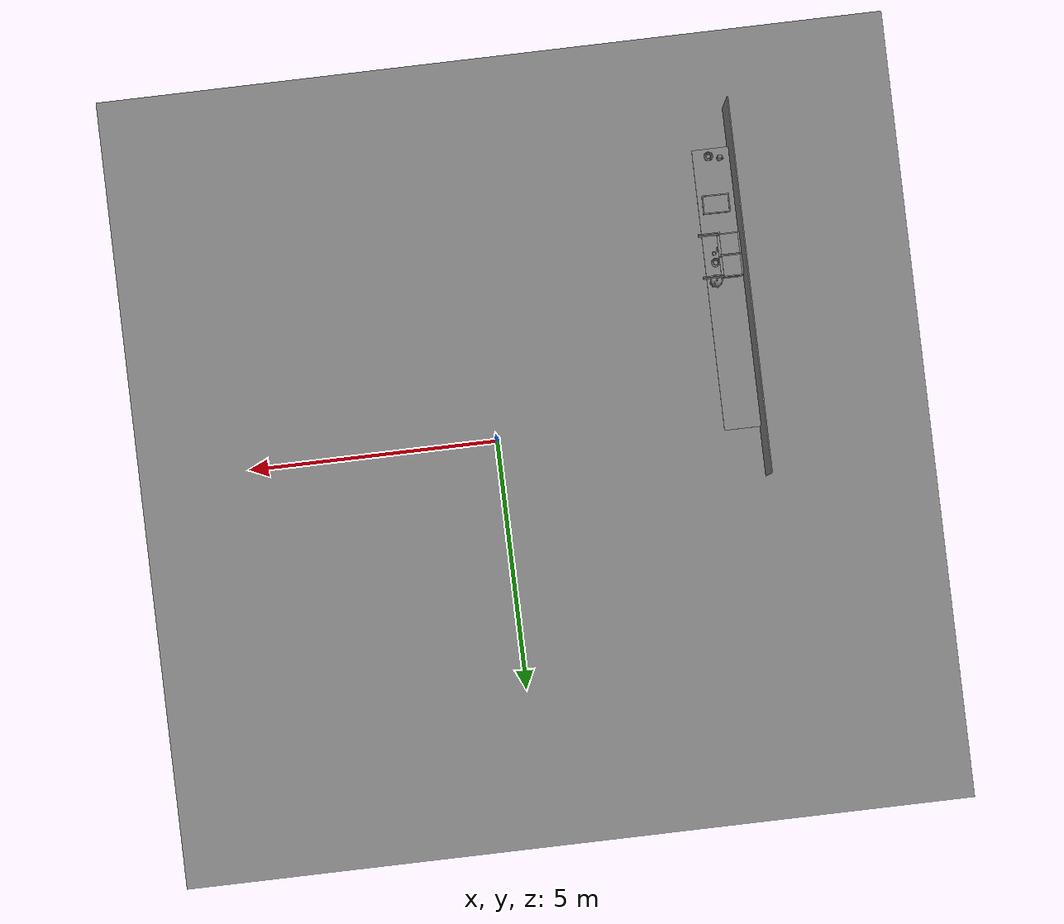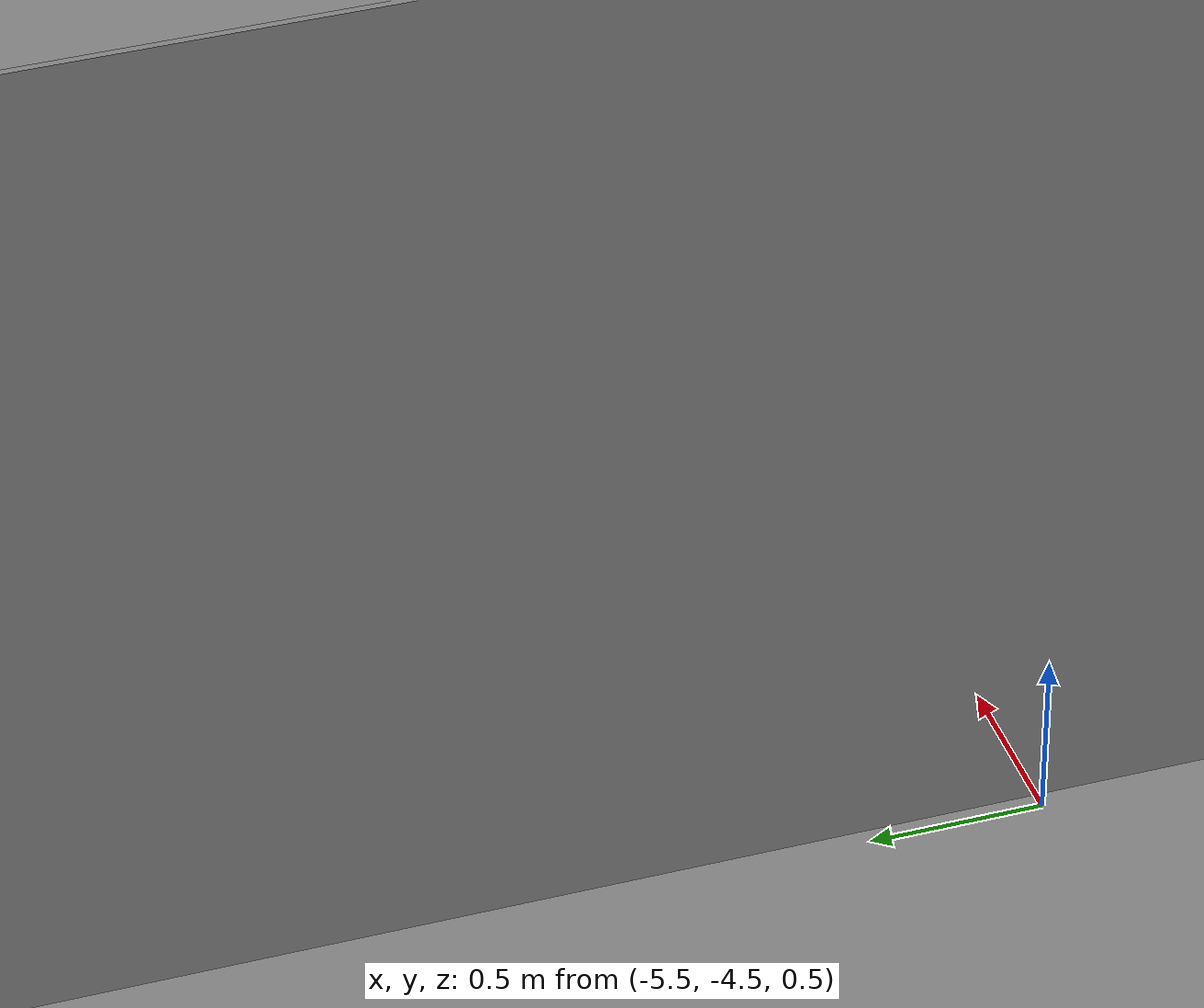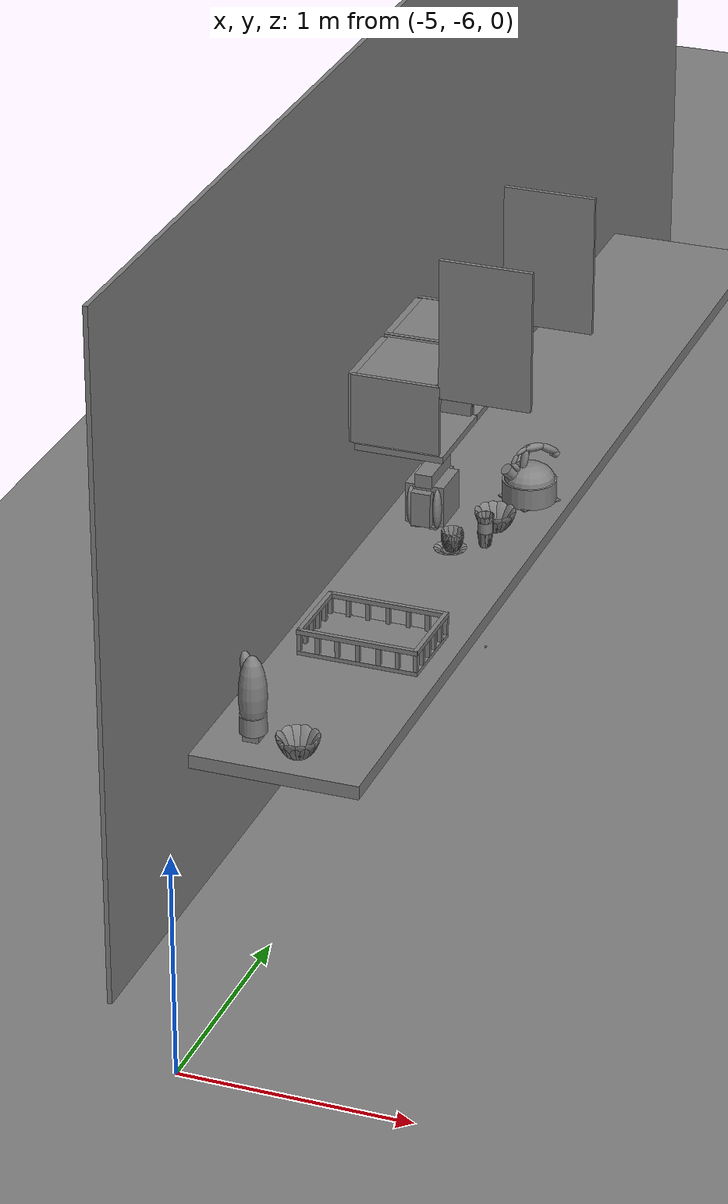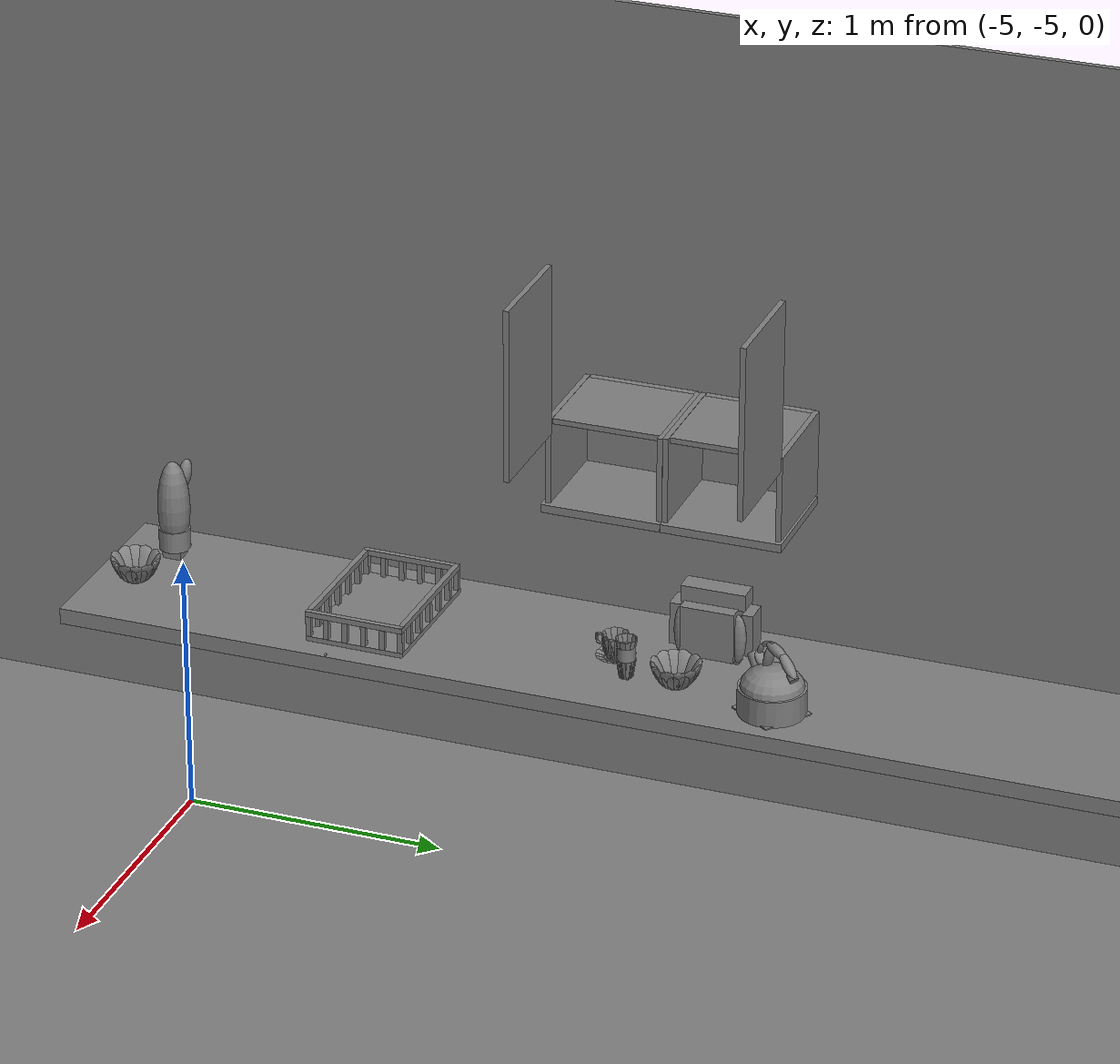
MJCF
<mujoco>
    <option gravity="0.000000000 0.000000000 -9.810000420" timestep="0.0049999999" integrator="implicitfast" density="9.8000002" viscosity="1.8000001e-05" noslip_iterations="10" iterations="100" sdf_iterations="50">
        <flag multiccd="disable"/>
    </option>
    <size memory="1000M"/>
    <compiler coordinate="local"/>
    <worldbody>
        <light cutoff="30" pos="0 1 1" dir="0 -1 -2"/>
        <light cutoff="30" pos="0 -1 1" dir="0 1 -2"/>
        <body pos="-4.860558510 -4.149443150 1.004824519" euler="0.000000000 0.000000000 -90.691108704" name="openloong_gripper_2f85_fix_base_usda_Basket_Kitchen_01">
            <geom contype="1" conaffinity="1" density="1000" type="box" material="" rgba="0.500000000 0.500000000 0.500000000 1.000000000" solimp="0.899999976 0.949999988 0.001000000" friction="1.000000000 0.005000000 0.000100000" solref="0.020000000 1.000000000" margin="0" condim="3" group="0" pos="-0.175679564 -0.000001431 0.109079957" quat="0.707107008 0.000000000 0.000000000 0.707106411" size="0.268999994 0.010000000 0.010500000" name="openloong_gripper_2f85_fix_base_usda_geom_68C5F516_2B1C_4DE3_BCB1_A667432AD079"/>
            <geom contype="1" conaffinity="1" density="1000" type="box" material="" rgba="0.500000000 0.500000000 0.500000000 1.000000000" solimp="0.899999976 0.949999988 0.001000000" friction="1.000000000 0.005000000 0.000100000" solref="0.020000000 1.000000000" margin="0" condim="3" group="0" pos="-0.176020086 0.002992153 0.059861541" quat="0.707107008 0.000000000 0.000000000 0.707106411" size="0.009500000 0.009500000 0.039999999" name="openloong_gripper_2f85_fix_base_usda_geom_CAAF5DB1_B23D_4D83_A863_3A6FFF4BE40F"/>
            <geom contype="1" conaffinity="1" density="1000" type="box" material="" rgba="0.500000000 0.500000000 0.500000000 1.000000000" solimp="0.899999976 0.949999988 0.001000000" friction="1.000000000 0.005000000 0.000100000" solref="0.020000000 1.000000000" margin="0" condim="3" group="0" pos="0.176000595 0.002991199 0.059860706" quat="0.707107008 0.000000000 0.000000000 0.707106411" size="0.009500000 0.009500000 0.039999999" name="openloong_gripper_2f85_fix_base_usda_geom_4CEC7EE0_B9C0_4280_8A98_FBCB07CC90C4"/>
            <geom contype="1" conaffinity="1" density="1000" type="box" material="" rgba="0.500000000 0.500000000 0.500000000 1.000000000" solimp="0.899999976 0.949999988 0.001000000" friction="1.000000000 0.005000000 0.000100000" solref="0.020000000 1.000000000" margin="0" condim="3" group="0" pos="0.176003456 0.259475708 0.059860110" quat="0.707107008 0.000000000 0.000000000 0.707106411" size="0.009500000 0.009500000 0.039999999" name="openloong_gripper_2f85_fix_base_usda_geom_9B220DDE_555E_4657_9966_559B253D2DE3"/>
            <geom contype="1" conaffinity="1" density="1000" type="box" material="" rgba="0.500000000 0.500000000 0.500000000 1.000000000" solimp="0.899999976 0.949999988 0.001000000" friction="1.000000000 0.005000000 0.000100000" solref="0.020000000 1.000000000" margin="0" condim="3" group="0" pos="-0.176020026 -0.088695526 0.059861422" quat="0.707107008 0.000000000 0.000000000 0.707106411" size="0.009500000 0.009500000 0.039999999" name="openloong_gripper_2f85_fix_base_usda_geom_E56031CD_1F1F_41BE_986F_601B6E15584B"/>
            <geom contype="1" conaffinity="1" density="1000" type="box" material="" rgba="0.500000000 0.500000000 0.500000000 1.000000000" solimp="0.899999976 0.949999988 0.001000000" friction="1.000000000 0.005000000 0.000100000" solref="0.020000000 1.000000000" margin="0" condim="3" group="0" pos="0.000000119 0.259647846 0.109080195" quat="0.707107008 0.000000000 0.000000000 0.707106411" size="0.010000000 0.185000002 0.010500000" name="openloong_gripper_2f85_fix_base_usda_geom_9317386C_0D19_4622_BC97_B22BF46468BF"/>
            <geom contype="1" conaffinity="1" density="1000" type="box" material="" rgba="0.500000000 0.500000000 0.500000000 1.000000000" solimp="0.899999976 0.949999988 0.001000000" friction="1.000000000 0.005000000 0.000100000" solref="0.020000000 1.000000000" margin="0" condim="3" group="0" pos="0.176002026 -0.259545326 0.059860349" quat="0.707107008 0.000000000 0.000000000 0.707106411" size="0.009500000 0.009500000 0.039999999" name="openloong_gripper_2f85_fix_base_usda_geom_AC047D03_5179_48C5_8D3A_F65FA280D45A"/>
            <geom contype="1" conaffinity="1" density="1000" type="box" material="" rgba="0.500000000 0.500000000 0.500000000 1.000000000" solimp="0.899999976 0.949999988 0.001000000" friction="1.000000000 0.005000000 0.000100000" solref="0.020000000 1.000000000" margin="0" condim="3" group="0" pos="0.036305428 -0.259545326 0.059860706" quat="0.707107008 0.000000000 0.000000000 0.707106411" size="0.009500000 0.009500000 0.039999999" name="openloong_gripper_2f85_fix_base_usda_geom_7EB840FD_56BB_4A32_B4AF_70C4FDCC76B4"/>
            <geom contype="1" conaffinity="1" density="1000" type="box" material="" rgba="0.500000000 0.500000000 0.500000000 1.000000000" solimp="0.899999976 0.949999988 0.001000000" friction="1.000000000 0.005000000 0.000100000" solref="0.020000000 1.000000000" margin="0" condim="3" group="0" pos="0.000000000 -0.259647369 0.109080195" quat="0.707107008 0.000000000 0.000000000 0.707106411" size="0.010000000 0.185000002 0.010500000" name="openloong_gripper_2f85_fix_base_usda_geom_C6FA1698_04DD_40DF_BB3C_9754C5893095"/>
            <geom contype="1" conaffinity="1" density="1000" type="box" material="" rgba="0.500000000 0.500000000 0.500000000 1.000000000" solimp="0.899999976 0.949999988 0.001000000" friction="1.000000000 0.005000000 0.000100000" solref="0.020000000 1.000000000" margin="0" condim="3" group="0" pos="-0.034950733 -0.259545803 0.059860826" quat="0.707107008 0.000000000 0.000000000 0.707106411" size="0.009500000 0.009500000 0.039999999" name="openloong_gripper_2f85_fix_base_usda_geom_14EA34FC_8521_4922_8AA0_58A556B44AF2"/>
            <geom contype="1" conaffinity="1" density="1000" type="box" material="" rgba="0.500000000 0.500000000 0.500000000 1.000000000" solimp="0.899999976 0.949999988 0.001000000" friction="1.000000000 0.005000000 0.000100000" solref="0.020000000 1.000000000" margin="0" condim="3" group="0" pos="0.108178139 0.259475946 0.059860229" quat="0.707107008 0.000000000 0.000000000 0.707106411" size="0.009500000 0.009500000 0.039999999" name="openloong_gripper_2f85_fix_base_usda_geom_17A21410_D525_4047_8E01_1112B0D834FA"/>
            <geom contype="1" conaffinity="1" density="1000" type="box" material="" rgba="0.500000000 0.500000000 0.500000000 1.000000000" solimp="0.899999976 0.949999988 0.001000000" friction="1.000000000 0.005000000 0.000100000" solref="0.020000000 1.000000000" margin="0" condim="3" group="0" pos="-0.106845737 0.259475231 0.059860826" quat="0.707107008 0.000000000 0.000000000 0.707106411" size="0.009500000 0.009500000 0.039999999" name="openloong_gripper_2f85_fix_base_usda_geom_0DD00FAE_417B_4E71_830C_284AF5E5FE04"/>
            <geom contype="1" conaffinity="1" density="1000" type="box" material="" rgba="0.500000000 0.500000000 0.500000000 1.000000000" solimp="0.899999976 0.949999988 0.001000000" friction="1.000000000 0.005000000 0.000100000" solref="0.020000000 1.000000000" margin="0" condim="3" group="0" pos="-0.176020563 0.179506302 0.059861779" quat="0.707107008 0.000000000 0.000000000 0.707106411" size="0.009500000 0.009500000 0.039999999" name="openloong_gripper_2f85_fix_base_usda_geom_4987561E_2D94_495C_8ADC_4EB21084EDD4"/>
            <geom contype="1" conaffinity="1" density="1000" type="box" material="" rgba="0.500000000 0.500000000 0.500000000 1.000000000" solimp="0.899999976 0.949999988 0.001000000" friction="1.000000000 0.005000000 0.000100000" solref="0.020000000 1.000000000" margin="0" condim="3" group="0" pos="-0.034949183 0.259475946 0.059860587" quat="0.707107008 0.000000000 0.000000000 0.707106411" size="0.009500000 0.009500000 0.039999999" name="openloong_gripper_2f85_fix_base_usda_geom_2DADC13F_D3D6_4910_A1FC_7B8815D7404C"/>
            <geom contype="1" conaffinity="1" density="1000" type="box" material="" rgba="0.500000000 0.500000000 0.500000000 1.000000000" solimp="0.899999976 0.949999988 0.001000000" friction="1.000000000 0.005000000 0.000100000" solref="0.020000000 1.000000000" margin="0" condim="3" group="0" pos="0.175792217 -0.000001907 0.109079838" quat="0.707107008 0.000000000 0.000000000 0.707106411" size="0.268999994 0.010000000 0.010500000" name="openloong_gripper_2f85_fix_base_usda_geom_AA1F3CBB_4D37_4B9C_BDEA_6238CEA96C5F"/>
            <geom contype="1" conaffinity="1" density="1000" type="box" material="" rgba="0.500000000 0.500000000 0.500000000 1.000000000" solimp="0.899999976 0.949999988 0.001000000" friction="1.000000000 0.005000000 0.000100000" solref="0.020000000 1.000000000" margin="0" condim="3" group="0" pos="-0.000015259 0.000000000 0.010668159" quat="0.707107008 0.000000000 0.000000000 0.707106411" size="0.268999994 0.186000004 0.010500000" name="openloong_gripper_2f85_fix_base_usda_geom_D07B0598_9292_4856_AAF7_2C24EB36BFAD"/>
            <geom contype="1" conaffinity="1" density="1000" type="box" material="" rgba="0.500000000 0.500000000 0.500000000 1.000000000" solimp="0.899999976 0.949999988 0.001000000" friction="1.000000000 0.005000000 0.000100000" solref="0.020000000 1.000000000" margin="0" condim="3" group="0" pos="-0.176020086 0.094225407 0.059861660" quat="0.707107008 0.000000000 0.000000000 0.707106411" size="0.009500000 0.009500000 0.039999999" name="openloong_gripper_2f85_fix_base_usda_geom_43832D7F_320E_4387_AFA4_CB72B2539AF0"/>
            <geom contype="1" conaffinity="1" density="1000" type="box" material="" rgba="0.500000000 0.500000000 0.500000000 1.000000000" solimp="0.899999976 0.949999988 0.001000000" friction="1.000000000 0.005000000 0.000100000" solref="0.020000000 1.000000000" margin="0" condim="3" group="0" pos="0.108177185 -0.259544849 0.059860468" quat="0.707107008 0.000000000 0.000000000 0.707106411" size="0.009500000 0.009500000 0.039999999" name="openloong_gripper_2f85_fix_base_usda_geom_68B6EF9E_E9C6_438F_8CC9_7C8C2FAD2E99"/>
            <geom contype="1" conaffinity="1" density="1000" type="box" material="" rgba="0.500000000 0.500000000 0.500000000 1.000000000" solimp="0.899999976 0.949999988 0.001000000" friction="1.000000000 0.005000000 0.000100000" solref="0.020000000 1.000000000" margin="0" condim="3" group="0" pos="-0.176019967 -0.177031994 0.059861302" quat="0.707107008 0.000000000 0.000000000 0.707106411" size="0.009500000 0.009500000 0.039999999" name="openloong_gripper_2f85_fix_base_usda_geom_1818A9E8_65B6_4D2B_BBC3_7E63C6EA425E"/>
            <geom contype="1" conaffinity="1" density="1000" type="box" material="" rgba="0.500000000 0.500000000 0.500000000 1.000000000" solimp="0.899999976 0.949999988 0.001000000" friction="1.000000000 0.005000000 0.000100000" solref="0.020000000 1.000000000" margin="0" condim="3" group="0" pos="-0.176020026 -0.259545326 0.059861183" quat="0.707107008 0.000000000 0.000000000 0.707106411" size="0.009500000 0.009500000 0.039999999" name="openloong_gripper_2f85_fix_base_usda_geom_152C1F46_9653_41FF_B5DE_ED281229CD6E"/>
            <geom contype="1" conaffinity="1" density="1000" type="box" material="" rgba="0.500000000 0.500000000 0.500000000 1.000000000" solimp="0.899999976 0.949999988 0.001000000" friction="1.000000000 0.005000000 0.000100000" solref="0.020000000 1.000000000" margin="0" condim="3" group="0" pos="-0.106846333 -0.259546280 0.059861064" quat="0.707107008 0.000000000 0.000000000 0.707106411" size="0.009500000 0.009500000 0.039999999" name="openloong_gripper_2f85_fix_base_usda_geom_E7320C49_4C58_4037_A9CC_E51E9D684CD6"/>
            <geom contype="1" conaffinity="1" density="1000" type="box" material="" rgba="0.500000000 0.500000000 0.500000000 1.000000000" solimp="0.899999976 0.949999988 0.001000000" friction="1.000000000 0.005000000 0.000100000" solref="0.020000000 1.000000000" margin="0" condim="3" group="0" pos="0.176000595 0.094224453 0.059860826" quat="0.707107008 0.000000000 0.000000000 0.707106411" size="0.009500000 0.009500000 0.039999999" name="openloong_gripper_2f85_fix_base_usda_geom_85A4B5B0_7F68_4BF1_8940_1C38762394F0"/>
            <geom contype="1" conaffinity="1" density="1000" type="box" material="" rgba="0.500000000 0.500000000 0.500000000 1.000000000" solimp="0.899999976 0.949999988 0.001000000" friction="1.000000000 0.005000000 0.000100000" solref="0.020000000 1.000000000" margin="0" condim="3" group="0" pos="0.176001072 -0.088696480 0.059860587" quat="0.707107008 0.000000000 0.000000000 0.707106411" size="0.009500000 0.009500000 0.039999999" name="openloong_gripper_2f85_fix_base_usda_geom_BCC267D6_66F2_4115_9D88_5533D5D365E7"/>
            <geom contype="1" conaffinity="1" density="1000" type="box" material="" rgba="0.500000000 0.500000000 0.500000000 1.000000000" solimp="0.899999976 0.949999988 0.001000000" friction="1.000000000 0.005000000 0.000100000" solref="0.020000000 1.000000000" margin="0" condim="3" group="0" pos="0.036307096 0.259476185 0.059860468" quat="0.707107008 0.000000000 0.000000000 0.707106411" size="0.009500000 0.009500000 0.039999999" name="openloong_gripper_2f85_fix_base_usda_geom_848B1B22_F112_437E_880A_3459278339C7"/>
            <geom contype="1" conaffinity="1" density="1000" type="box" material="" rgba="0.500000000 0.500000000 0.500000000 1.000000000" solimp="0.899999976 0.949999988 0.001000000" friction="1.000000000 0.005000000 0.000100000" solref="0.020000000 1.000000000" margin="0" condim="3" group="0" pos="0.176001549 -0.177031994 0.059860468" quat="0.707107008 0.000000000 0.000000000 0.707106411" size="0.009500000 0.009500000 0.039999999" name="openloong_gripper_2f85_fix_base_usda_geom_A96D50FE_A948_4872_80AE_E555249BD36D"/>
            <geom contype="1" conaffinity="1" density="1000" type="box" material="" rgba="0.500000000 0.500000000 0.500000000 1.000000000" solimp="0.899999976 0.949999988 0.001000000" friction="1.000000000 0.005000000 0.000100000" solref="0.020000000 1.000000000" margin="0" condim="3" group="0" pos="0.176000118 0.179505348 0.059860945" quat="0.707107008 0.000000000 0.000000000 0.707106411" size="0.009500000 0.009500000 0.039999999" name="openloong_gripper_2f85_fix_base_usda_geom_3E1F5507_D529_4A5F_B6A9_3DBB193000EE"/>
            <geom contype="1" conaffinity="1" density="1000" type="box" material="" rgba="0.500000000 0.500000000 0.500000000 1.000000000" solimp="0.899999976 0.949999988 0.001000000" friction="1.000000000 0.005000000 0.000100000" solref="0.020000000 1.000000000" margin="0" condim="3" group="0" pos="-0.176020086 0.259474993 0.059860945" quat="0.707107008 0.000000000 0.000000000 0.707106411" size="0.009500000 0.009500000 0.039999999" name="openloong_gripper_2f85_fix_base_usda_geom_CC3CE34C_9981_4A3E_AE1F_32A054CF5873"/>
            <freejoint name="openloong_gripper_2f85_fix_base_usda_Basket_Kitchen_01_joint"/>
        </body>
        <body pos="-4.802892208 -3.488179445 1.876015186" euler="89.999992371 -89.999946594 0.000000000" name="Interactive Objcets_guimen_01">
            <geom contype="1" conaffinity="1" density="1000" type="box" material="" rgba="0.500000000 0.500000000 0.500000000 1.000000000" solimp="0.899999976 0.949999988 0.001000000" friction="1.000000000 0.005000000 0.000100000" solref="0.020000000 1.000000000" margin="0" condim="3" group="0" pos="0.006727934 0.314709902 -0.203009605" quat="1.000000000 0.000000119 -0.000000119 0.000000000" size="0.010000000 0.317999989 0.204999998" name="Interactive Objcets_geom_AE13677C_2019_419A_A3EA_81EE54CB2330"/>
            <joint armature="0" stiffness="0" damping="1" axis="0.000000 1.000000 0.000000" type="hinge" name="Interactive Objcets_guimen_01"/>
        </body>
        <body pos="-4.805274963 -2.665403366 1.876015186" euler="89.999877930 89.999969482 0.000000000" name="Interactive Objcets_guimen_02">
            <geom contype="1" conaffinity="1" density="1000" type="box" material="" rgba="0.500000000 0.500000000 0.500000000 1.000000000" solimp="0.899999976 0.949999988 0.001000000" friction="1.000000000 0.005000000 0.000100000" solref="0.020000000 1.000000000" margin="0" condim="3" group="0" pos="0.006727815 0.314709663 0.203009367" quat="0.999999940 0.000000000 0.000000000 0.000000000" size="0.010000000 0.317999989 0.204999998" name="Interactive Objcets_geom_DA5EB31D_EC27_4A17_B8BC_B2D1FA892C18"/>
            <joint armature="0" stiffness="0" damping="1" axis="0.000000 1.000000 0.000000" type="hinge" name="Interactive Objcets_guimen_02"/>
        </body>
        <body pos="-4.827295780 -3.287638187 1.074643731" euler="0.000000000 0.000000000 89.999992371" name="Interactive Objcets_coffeecup_01">
            <geom contype="1" conaffinity="1" density="1000" type="ellipsoid" material="" rgba="0.500000000 0.500000000 0.500000000 1.000000000" solimp="0.899999976 0.949999988 0.001000000" friction="1.000000000 0.005000000 0.000100000" solref="0.020000000 1.000000000" margin="0" condim="3" group="0" pos="0.035336256 0.000558376 -0.043215394" quat="0.999999881 0.000000000 0.000000000 0.000000000" size="0.029999999 0.029999999 0.001000000" name="Interactive Objcets_geom_DFDAA80C_E58F_4D79_8950_97F2C4E7FEF2"/>
            <geom contype="1" conaffinity="1" density="1000" type="ellipsoid" material="" rgba="0.500000000 0.500000000 0.500000000 1.000000000" solimp="0.899999976 0.949999988 0.001000000" friction="1.000000000 0.005000000 0.000100000" solref="0.020000000 1.000000000" margin="0" condim="3" group="0" pos="0.067416430 -0.018191338 0.002976775" quat="0.961934388 0.024418317 0.091648072 -0.256293803" size="0.005000000 0.029999999 0.048999999" name="Interactive Objcets_geom_3059C78A_9048_435B_BD1E_D101B260F362"/>
            <geom contype="1" conaffinity="1" density="1000" type="ellipsoid" material="" rgba="0.500000000 0.500000000 0.500000000 1.000000000" solimp="0.899999976 0.949999988 0.001000000" friction="1.000000000 0.005000000 0.000100000" solref="0.020000000 1.000000000" margin="0" condim="3" group="0" pos="0.034471050 -0.037125111 0.002976775" quat="0.701517045 0.067293778 0.066836871 -0.706313014" size="0.005000000 0.029999999 0.048999999" name="Interactive Objcets_geom_009941CB_E4AC_4A38_AE6E_7C6DAEEBF030"/>
            <geom contype="1" conaffinity="1" density="1000" type="ellipsoid" material="" rgba="0.500000000 0.500000000 0.500000000 1.000000000" solimp="0.899999976 0.949999988 0.001000000" friction="1.000000000 0.005000000 0.000100000" solref="0.020000000 1.000000000" margin="0" condim="3" group="0" pos="0.035336256 0.000558376 -0.045152068" quat="0.999999881 0.000000000 0.000000000 0.000000000" size="0.029999999 0.029999999 0.001000000" name="Interactive Objcets_geom_F67254F0_2EE9_4D66_8517_E4F2F08B397D"/>
            <geom contype="1" conaffinity="1" density="1000" type="ellipsoid" material="" rgba="0.500000000 0.500000000 0.500000000 1.000000000" solimp="0.899999976 0.949999988 0.001000000" friction="1.000000000 0.005000000 0.000100000" solref="0.020000000 1.000000000" margin="0" condim="3" group="0" pos="0.001010895 -0.016271591 0.002976775" quat="0.228377163 0.092315644 0.021758538 -0.968941689" size="0.005000000 0.029999999 0.048999999" name="Interactive Objcets_geom_2F872AAD_DD68_4D81_A415_2B4144AF75FC"/>
            <geom contype="1" conaffinity="1" density="1000" type="capsule" material="" rgba="0.500000000 0.500000000 0.500000000 1.000000000" solimp="0.899999976 0.949999988 0.001000000" friction="1.000000000 0.005000000 0.000100000" solref="0.020000000 1.000000000" margin="0" condim="3" group="0" pos="-0.021276474 0.000000000 0.038509369" quat="0.633189917 0.000000000 0.773996413 0.000000000" size="0.004000000 0.009000000 1.000000000" name="Interactive Objcets_geom_022BF251_23FB_4E3E_8656_7D88E90FC91F"/>
            <geom contype="1" conaffinity="1" density="1000" type="capsule" material="" rgba="0.500000000 0.500000000 0.500000000 1.000000000" solimp="0.899999976 0.949999988 0.001000000" friction="1.000000000 0.005000000 0.000100000" solref="0.020000000 1.000000000" margin="0" condim="3" group="0" pos="-0.018014431 0.000000000 0.001762271" quat="0.707106769 -0.000000004 0.707106709 -0.000000088" size="0.004000000 0.005000000 1.000000000" name="Interactive Objcets_geom_E4B850AD_2F3D_430C_8191_5583EA9F5885"/>
            <geom contype="1" conaffinity="1" density="1000" type="ellipsoid" material="" rgba="0.500000000 0.500000000 0.500000000 1.000000000" solimp="0.899999976 0.949999988 0.001000000" friction="1.000000000 0.005000000 0.000100000" solref="0.020000000 1.000000000" margin="0" condim="3" group="0" pos="0.068445444 0.017385960 0.002976775" quat="0.228377223 -0.092319682 -0.021759447 -0.968941331" size="0.005000000 0.029999999 0.048999999" name="Interactive Objcets_geom_C0B774CB_ACFE_4924_8B6D_7001F4DA6BCD"/>
            <geom contype="1" conaffinity="1" density="1000" type="ellipsoid" material="" rgba="0.500000000 0.500000000 0.500000000 1.000000000" solimp="0.899999976 0.949999988 0.001000000" friction="1.000000000 0.005000000 0.000100000" solref="0.020000000 1.000000000" margin="0" condim="3" group="0" pos="0.002039194 0.019308567 0.002976775" quat="0.961933970 -0.024419386 -0.091652036 -0.256293654" size="0.005000000 0.029999999 0.048999999" name="Interactive Objcets_geom_CA342855_7EB0_4B55_B9A2_994CEE43A413"/>
            <geom contype="1" conaffinity="1" density="1000" type="ellipsoid" material="" rgba="0.500000000 0.500000000 0.500000000 1.000000000" solimp="0.899999976 0.949999988 0.001000000" friction="1.000000000 0.005000000 0.000100000" solref="0.020000000 1.000000000" margin="0" condim="3" group="0" pos="0.034984604 0.038240910 0.002976775" quat="0.701516926 -0.067296736 -0.066839755 -0.706312656" size="0.005000000 0.029999999 0.048999999" name="Interactive Objcets_geom_AFF2839B_C52D_4025_8FAF_4FF7E7F0A426"/>
            <geom contype="1" conaffinity="1" density="1000" type="ellipsoid" material="" rgba="0.500000000 0.500000000 0.500000000 1.000000000" solimp="0.899999976 0.949999988 0.001000000" friction="1.000000000 0.005000000 0.000100000" solref="0.020000000 1.000000000" margin="0" condim="3" group="0" pos="0.017669693 0.034160614 0.002976775" quat="0.848410904 -0.049618516 -0.080835648 -0.520770907" size="0.005000000 0.029999999 0.048999999" name="Interactive Objcets_geom_183BCB4B_E68A_4230_8EEC_4178B9E4A878"/>
            <geom contype="1" conaffinity="1" density="1000" type="ellipsoid" material="" rgba="0.500000000 0.500000000 0.500000000 1.000000000" solimp="0.899999976 0.949999988 0.001000000" friction="1.000000000 0.005000000 0.000100000" solref="0.020000000 1.000000000" margin="0" condim="3" group="0" pos="-0.002956629 0.000558376 0.002976775" quat="0.995491505 0.000000004 -0.094849378 -0.000000089" size="0.005000000 0.029999999 0.048999999" name="Interactive Objcets_geom_D02EFF4A_25BE_410C_A52F_D143CE4EB468"/>
            <geom contype="1" conaffinity="1" density="1000" type="ellipsoid" material="" rgba="0.500000000 0.500000000 0.500000000 1.000000000" solimp="0.899999976 0.949999988 0.001000000" friction="1.000000000 0.005000000 0.000100000" solref="0.020000000 1.000000000" margin="0" condim="3" group="0" pos="0.051787138 -0.033043861 0.002976775" quat="0.848411202 0.049616337 0.080832161 -0.520771146" size="0.005000000 0.029999999 0.048999999" name="Interactive Objcets_geom_AED460BB_10C0_45CC_9EB0_921FE2832D02"/>
            <geom contype="1" conaffinity="1" density="1000" type="capsule" material="" rgba="0.500000000 0.500000000 0.500000000 1.000000000" solimp="0.899999976 0.949999988 0.001000000" friction="1.000000000 0.005000000 0.000100000" solref="0.020000000 1.000000000" margin="0" condim="3" group="0" pos="-0.030251026 0.000000000 0.004966617" quat="0.480583906 -0.000000000 0.876948774 -0.000000126" size="0.004000000 0.005000000 1.000000000" name="Interactive Objcets_geom_6682AB59_C8A5_4EC2_A69F_2236AEEB4E0F"/>
            <geom contype="1" conaffinity="1" density="1000" type="capsule" material="" rgba="0.500000000 0.500000000 0.500000000 1.000000000" solimp="0.899999976 0.949999988 0.001000000" friction="1.000000000 0.005000000 0.000100000" solref="0.020000000 1.000000000" margin="0" condim="3" group="0" pos="-0.036300898 0.000000000 0.021037936" quat="0.044551343 -0.000000000 0.999007046 -0.000000126" size="0.004000000 0.012000000 1.000000000" name="Interactive Objcets_geom_10DC5A2C_4229_4548_85C2_5E3B09CA72AE"/>
            <geom contype="1" conaffinity="1" density="1000" type="capsule" material="" rgba="0.500000000 0.500000000 0.500000000 1.000000000" solimp="0.899999976 0.949999988 0.001000000" friction="1.000000000 0.005000000 0.000100000" solref="0.020000000 1.000000000" margin="0" condim="3" group="0" pos="-0.008219719 0.000000000 -0.000944734" quat="0.364379913 0.000000063 0.931250274 -0.000000063" size="0.004000000 0.003000000 1.000000000" name="Interactive Objcets_geom_DB4692B7_FEFE_4C11_BA6A_A3DD50E704C7"/>
            <geom contype="1" conaffinity="1" density="1000" type="capsule" material="" rgba="0.500000000 0.500000000 0.500000000 1.000000000" solimp="0.899999976 0.949999988 0.001000000" friction="1.000000000 0.005000000 0.000100000" solref="0.020000000 1.000000000" margin="0" condim="3" group="0" pos="-0.033022881 0.000000000 0.037873149" quat="0.874267220 0.000000042 0.485444903 -0.000000084" size="0.004000000 0.004000000 1.000000000" name="Interactive Objcets_geom_CC7406DB_1D30_44A3_B43E_EFD5D73B69F4"/>
            <geom contype="1" conaffinity="1" density="1000" type="ellipsoid" material="" rgba="0.500000000 0.500000000 0.500000000 1.000000000" solimp="0.899999976 0.949999988 0.001000000" friction="1.000000000 0.005000000 0.000100000" solref="0.020000000 1.000000000" margin="0" condim="3" group="0" pos="0.015755907 -0.032001972 0.002976775" quat="0.496025920 0.082232773 0.047258731 -0.863112032" size="0.005000000 0.029999999 0.048999999" name="Interactive Objcets_geom_657CC565_4B1F_4EBA_85CC_32251E9F54F8"/>
            <geom contype="1" conaffinity="1" density="1000" type="ellipsoid" material="" rgba="0.500000000 0.500000000 0.500000000 1.000000000" solimp="0.899999976 0.949999988 0.001000000" friction="1.000000000 0.005000000 0.000100000" solref="0.020000000 1.000000000" margin="0" condim="3" group="0" pos="0.072411790 0.000558376 0.002976775" quat="0.995491922 -0.000000019 0.094845265 -0.000000089" size="0.005000000 0.029999999 0.048999999" name="Interactive Objcets_geom_146D2B28_F6B8_42AB_A602_2E31B3361FD2"/>
            <geom contype="1" conaffinity="1" density="1000" type="ellipsoid" material="" rgba="0.500000000 0.500000000 0.500000000 1.000000000" solimp="0.899999976 0.949999988 0.001000000" friction="1.000000000 0.005000000 0.000100000" solref="0.020000000 1.000000000" margin="0" condim="3" group="0" pos="0.053700209 0.033117294 0.002976775" quat="0.496025741 -0.082236379 -0.047260769 -0.863111615" size="0.005000000 0.029999999 0.048999999" name="Interactive Objcets_geom_07641D4E_5B3D_4ED9_80BD_5162122D868F"/>
            <freejoint name="Interactive Objcets_coffeecup_01"/>
        </body>
        <body pos="-5.020127296 -2.953741550 1.135127425" euler="89.999946594 0.000000000 0.000000000" name="Interactive Objcets_Bread">
            <geom contype="1" conaffinity="1" density="1000" type="box" material="" rgba="0.500000000 0.500000000 0.500000000 1.000000000" solimp="0.899999976 0.949999988 0.001000000" friction="1.000000000 0.005000000 0.000100000" solref="0.020000000 1.000000000" margin="0" condim="3" group="0" pos="-0.008702755 -0.017670274 -0.135069147" quat="0.707107067 -0.707106471 0.000000021 -0.000000021" size="0.045000002 0.020000000 0.079999998" name="Interactive Objcets_geom_033B73B3_0251_4CC1_84D2_EA5856E49E97"/>
            <geom contype="1" conaffinity="1" density="1000" type="box" material="" rgba="0.500000000 0.500000000 0.500000000 1.000000000" solimp="0.899999976 0.949999988 0.001000000" friction="1.000000000 0.005000000 0.000100000" solref="0.020000000 1.000000000" margin="0" condim="3" group="0" pos="0.033925056 -0.123201847 0.086778767" quat="0.707107067 -0.707106471 0.000000021 -0.000000021" size="0.020000000 0.020000000 0.005000000" name="Interactive Objcets_geom_2C5A276C_3306_41B8_A4B9_90A39AD3E4F0"/>
            <geom contype="1" conaffinity="1" density="1000" type="box" material="" rgba="0.500000000 0.500000000 0.500000000 1.000000000" solimp="0.899999976 0.949999988 0.001000000" friction="1.000000000 0.005000000 0.000100000" solref="0.020000000 1.000000000" margin="0" condim="3" group="0" pos="-0.008702755 -0.016588926 0.000174277" quat="0.707107067 -0.707106471 0.000000021 -0.000000021" size="0.090000004 0.100000001 0.094999999" name="Interactive Objcets_geom_67B860BB_1F1F_4995_B0E7_CC18D626EFB4"/>
            <geom contype="1" conaffinity="1" density="1000" type="ellipsoid" material="" rgba="0.500000000 0.500000000 0.500000000 1.000000000" solimp="0.899999976 0.949999988 0.001000000" friction="1.000000000 0.005000000 0.000100000" solref="0.020000000 1.000000000" margin="0" condim="3" group="0" pos="-0.067312241 -0.026057482 -0.101716787" quat="0.707107067 -0.707106471 0.000000021 -0.000000021" size="0.020000000 0.029999999 0.094999999" name="Interactive Objcets_geom_632C2F7A_BC7C_4D32_8557_EB819545AEF7"/>
            <geom contype="1" conaffinity="1" density="1000" type="ellipsoid" material="" rgba="0.500000000 0.500000000 0.500000000 1.000000000" solimp="0.899999976 0.949999988 0.001000000" friction="1.000000000 0.005000000 0.000100000" solref="0.020000000 1.000000000" margin="0" condim="3" group="0" pos="0.052222252 -0.026057363 0.101459242" quat="0.707107067 -0.707106471 0.000000021 -0.000000021" size="0.020000000 0.029999999 0.094999999" name="Interactive Objcets_geom_7F4B5D7F_471E_4269_A93A_EB93FC85863F"/>
            <geom contype="1" conaffinity="1" density="1000" type="box" material="" rgba="0.500000000 0.500000000 0.500000000 1.000000000" solimp="0.899999976 0.949999988 0.001000000" friction="1.000000000 0.005000000 0.000100000" solref="0.020000000 1.000000000" margin="0" condim="3" group="0" pos="-0.050020695 -0.123201847 0.086778767" quat="0.707107067 -0.707106471 0.000000021 -0.000000021" size="0.020000000 0.020000000 0.005000000" name="Interactive Objcets_geom_600B38FC_F7D4_476E_83B9_2A5034C92037"/>
            <geom contype="1" conaffinity="1" density="1000" type="box" material="" rgba="0.500000000 0.500000000 0.500000000 1.000000000" solimp="0.899999976 0.949999988 0.001000000" friction="1.000000000 0.005000000 0.000100000" solref="0.020000000 1.000000000" margin="0" condim="3" group="0" pos="0.033925056 -0.123201728 -0.092369899" quat="0.707107067 -0.707106471 0.000000021 -0.000000021" size="0.020000000 0.020000000 0.005000000" name="Interactive Objcets_geom_0E7AAC57_1099_476D_996E_D02A5B5CE712"/>
            <geom contype="1" conaffinity="1" density="1000" type="ellipsoid" material="" rgba="0.500000000 0.500000000 0.500000000 1.000000000" solimp="0.899999976 0.949999988 0.001000000" friction="1.000000000 0.005000000 0.000100000" solref="0.020000000 1.000000000" margin="0" condim="3" group="0" pos="-0.069190502 -0.026057363 0.101458766" quat="0.707107067 -0.707106471 0.000000021 -0.000000021" size="0.020000000 0.029999999 0.094999999" name="Interactive Objcets_geom_E2AED50B_DEAC_4605_8A0C_E0D72F9FD0EA"/>
            <geom contype="1" conaffinity="1" density="1000" type="box" material="" rgba="0.500000000 0.500000000 0.500000000 1.000000000" solimp="0.899999976 0.949999988 0.001000000" friction="1.000000000 0.005000000 0.000100000" solref="0.020000000 1.000000000" margin="0" condim="3" group="0" pos="-0.008702755 -0.017670155 0.134585604" quat="0.707107067 -0.707106471 0.000000021 -0.000000021" size="0.045000002 0.020000000 0.079999998" name="Interactive Objcets_geom_F0911C80_30B6_4FD0_8244_543F57DDDD1B"/>
            <geom contype="1" conaffinity="1" density="1000" type="box" material="" rgba="0.500000000 0.500000000 0.500000000 1.000000000" solimp="0.899999976 0.949999988 0.001000000" friction="1.000000000 0.005000000 0.000100000" solref="0.020000000 1.000000000" margin="0" condim="3" group="0" pos="-0.050020695 -0.123201728 -0.092370376" quat="0.707107067 -0.707106471 0.000000021 -0.000000021" size="0.020000000 0.020000000 0.005000000" name="Interactive Objcets_geom_55DB3F42_AD3A_4297_ACEB_314DEE9E442A"/>
            <geom contype="1" conaffinity="1" density="1000" type="box" material="" rgba="0.500000000 0.500000000 0.500000000 1.000000000" solimp="0.899999976 0.949999988 0.001000000" friction="1.000000000 0.005000000 0.000100000" solref="0.020000000 1.000000000" margin="0" condim="3" group="0" pos="-0.008702755 0.104617000 -0.003706597" quat="0.707107067 -0.707106471 0.000000021 -0.000000021" size="0.039999999 0.119999997 0.030999999" name="Interactive Objcets_geom_71CD5574_42C5_4A14_A811_3E09AC4C946D"/>
            <geom contype="1" conaffinity="1" density="1000" type="ellipsoid" material="" rgba="0.500000000 0.500000000 0.500000000 1.000000000" solimp="0.899999976 0.949999988 0.001000000" friction="1.000000000 0.005000000 0.000100000" solref="0.020000000 1.000000000" margin="0" condim="3" group="0" pos="0.052222252 -0.026057243 -0.106481344" quat="0.707107067 -0.707106471 0.000000021 -0.000000021" size="0.020000000 0.029999999 0.094999999" name="Interactive Objcets_geom_0D134FAE_F3A4_4BD6_A2E1_8B5216A3ED5B"/>
            <freejoint name="Interactive Objcets_Bread"/>
        </body>
        <body pos="-4.821335316 -5.105734825 1.007418752" euler="0.000000000 0.000000000 89.999946594" name="Interactive Objcets_bow_04">
            <geom contype="1" conaffinity="1" density="1000" type="ellipsoid" material="" rgba="0.500000000 0.500000000 0.500000000 1.000000000" solimp="0.899999976 0.949999988 0.001000000" friction="1.000000000 0.005000000 0.000100000" solref="0.020000000 1.000000000" margin="0" condim="3" group="0" pos="0.052321672 -0.040297985 0.044118762" quat="0.919264674 0.076882720 0.225593746 -0.313287675" size="0.010000000 0.039999999 0.052000001" name="Interactive Objcets_geom_B6777273_8E9A_4096_96A6_1803DA448FF9"/>
            <geom contype="1" conaffinity="1" density="1000" type="ellipsoid" material="" rgba="0.500000000 0.500000000 0.500000000 1.000000000" solimp="0.899999976 0.949999988 0.001000000" friction="1.000000000 0.005000000 0.000100000" solref="0.020000000 1.000000000" margin="0" condim="3" group="0" pos="0.059080124 0.029511929 0.044118762" quat="0.223252952 -0.231952190 -0.054787360 -0.945174456" size="0.010000000 0.039999999 0.052000001" name="Interactive Objcets_geom_B08999F4_AE23_463B_B45E_D57C8C2FABD9"/>
            <geom contype="1" conaffinity="1" density="1000" type="ellipsoid" material="" rgba="0.500000000 0.500000000 0.500000000 1.000000000" solimp="0.899999976 0.949999988 0.001000000" friction="1.000000000 0.005000000 0.000100000" solref="0.020000000 1.000000000" margin="0" condim="3" group="0" pos="0.000082970 0.000000000 0.003118873" quat="1.000000000 0.000000000 0.000000000 0.000000000" size="0.039999999 0.039999999 0.002000000" name="Interactive Objcets_geom_C0E231A8_07AC_4372_9159_DEFB4E1EB2D6"/>
            <geom contype="1" conaffinity="1" density="1000" type="ellipsoid" material="" rgba="0.500000000 0.500000000 0.500000000 1.000000000" solimp="0.899999976 0.949999988 0.001000000" friction="1.000000000 0.005000000 0.000100000" solref="0.020000000 1.000000000" margin="0" condim="3" group="0" pos="-0.040080309 -0.052354813 0.044118762" quat="0.429593146 0.213749856 0.105425127 -0.871003032" size="0.010000000 0.039999999 0.052000001" name="Interactive Objcets_geom_70CE1400_A7B4_462F_8EA0_5606D22A4AE3"/>
            <geom contype="1" conaffinity="1" density="1000" type="ellipsoid" material="" rgba="0.500000000 0.500000000 0.500000000 1.000000000" solimp="0.899999976 0.949999988 0.001000000" friction="1.000000000 0.005000000 0.000100000" solref="0.020000000 1.000000000" margin="0" condim="3" group="0" pos="0.000243664 -0.065983295 0.044118762" quat="0.687598884 0.168314576 0.168741226 -0.685860336" size="0.010000000 0.039999999 0.052000001" name="Interactive Objcets_geom_0FA8165B_6211_4223_A62C_330BB78DA865"/>
            <geom contype="1" conaffinity="1" density="1000" type="ellipsoid" material="" rgba="0.500000000 0.500000000 0.500000000 1.000000000" solimp="0.899999976 0.949999988 0.001000000" friction="1.000000000 0.005000000 0.000100000" solref="0.020000000 1.000000000" margin="0" condim="3" group="0" pos="-0.065898657 -0.000007629 0.044118762" quat="0.971183062 -0.000000142 -0.238334835 0.000000030" size="0.010000000 0.039999999 0.052000001" name="Interactive Objcets_geom_D4AA84A1_F97B_4626_8F82_B5AFAD5A555E"/>
            <geom contype="1" conaffinity="1" density="1000" type="ellipsoid" material="" rgba="0.500000000 0.500000000 0.500000000 1.000000000" solimp="0.899999976 0.949999988 0.001000000" friction="1.000000000 0.005000000 0.000100000" solref="0.020000000 1.000000000" margin="0" condim="3" group="0" pos="-0.052167892 0.040281773 0.044118762" quat="0.919264615 -0.076883025 -0.225593626 -0.313287735" size="0.010000000 0.039999999 0.052000001" name="Interactive Objcets_geom_35076A53_CE34_4FE5_80A2_C7AB8E7EE8EA"/>
            <geom contype="1" conaffinity="1" density="1000" type="ellipsoid" material="" rgba="0.500000000 0.500000000 0.500000000 1.000000000" solimp="0.899999976 0.949999988 0.001000000" friction="1.000000000 0.005000000 0.000100000" solref="0.020000000 1.000000000" margin="0" condim="3" group="0" pos="-0.029293537 0.059069157 0.044118762" quat="0.825556040 -0.125530839 -0.202596709 -0.511521041" size="0.010000000 0.039999999 0.052000001" name="Interactive Objcets_geom_2706B70D_F454_499B_A5D2_D546B63C219A"/>
            <geom contype="1" conaffinity="1" density="1000" type="ellipsoid" material="" rgba="0.500000000 0.500000000 0.500000000 1.000000000" solimp="0.899999976 0.949999988 0.001000000" friction="1.000000000 0.005000000 0.000100000" solref="0.020000000 1.000000000" margin="0" condim="3" group="0" pos="0.000082970 0.000000000 0.000446677" quat="1.000000000 0.000000000 0.000000000 0.000000000" size="0.039999999 0.039999999 0.002000000" name="Interactive Objcets_geom_9459149C_0D1C_41FD_9AFD_596C83E17BC8"/>
            <geom contype="1" conaffinity="1" density="1000" type="ellipsoid" material="" rgba="0.500000000 0.500000000 0.500000000 1.000000000" solimp="0.899999976 0.949999988 0.001000000" friction="1.000000000 0.005000000 0.000100000" solref="0.020000000 1.000000000" margin="0" condim="3" group="0" pos="0.029448032 -0.059085369 0.044118762" quat="0.825555801 0.125530601 0.202597082 -0.511521280" size="0.010000000 0.039999999 0.052000001" name="Interactive Objcets_geom_DB3D47D3_6542_4367_818B_208641405C3D"/>
            <geom contype="1" conaffinity="1" density="1000" type="ellipsoid" material="" rgba="0.500000000 0.500000000 0.500000000 1.000000000" solimp="0.899999976 0.949999988 0.001000000" friction="1.000000000 0.005000000 0.000100000" solref="0.020000000 1.000000000" margin="0" condim="3" group="0" pos="0.066051960 -0.000007629 0.044118762" quat="0.971183062 -0.000000156 0.238334835 0.000000030" size="0.010000000 0.039999999 0.052000001" name="Interactive Objcets_geom_06F5F78A_216F_4CCD_A02A_BEA136D4A90D"/>
            <geom contype="1" conaffinity="1" density="1000" type="ellipsoid" material="" rgba="0.500000000 0.500000000 0.500000000 1.000000000" solimp="0.899999976 0.949999988 0.001000000" friction="1.000000000 0.005000000 0.000100000" solref="0.020000000 1.000000000" margin="0" condim="3" group="0" pos="-0.058925867 -0.029528618 0.044118762" quat="0.223252863 0.231952116 0.054787725 -0.945174456" size="0.010000000 0.039999999 0.052000001" name="Interactive Objcets_geom_B35D9EA2_674C_4829_8D7B_05454DECDCB0"/>
            <geom contype="1" conaffinity="1" density="1000" type="ellipsoid" material="" rgba="0.500000000 0.500000000 0.500000000 1.000000000" solimp="0.899999976 0.949999988 0.001000000" friction="1.000000000 0.005000000 0.000100000" solref="0.020000000 1.000000000" margin="0" condim="3" group="0" pos="0.040234327 0.052339077 0.044118762" quat="0.429593533 -0.213750005 -0.105424747 -0.871002972" size="0.010000000 0.039999999 0.052000001" name="Interactive Objcets_geom_8750832D_A26A_4C1C_A6A7_1D5B7A2B4404"/>
            <geom contype="1" conaffinity="1" density="1000" type="ellipsoid" material="" rgba="0.500000000 0.500000000 0.500000000 1.000000000" solimp="0.899999976 0.949999988 0.001000000" friction="1.000000000 0.005000000 0.000100000" solref="0.020000000 1.000000000" margin="0" condim="3" group="0" pos="-0.000090122 0.065967083 0.044118762" quat="0.687598825 -0.168314755 -0.168741047 -0.685860395" size="0.010000000 0.039999999 0.052000001" name="Interactive Objcets_geom_1CA6D02F_2EC4_46C3_B057_3D1ED23E5B4B"/>
            <freejoint name="Interactive Objcets_bow_04"/>
        </body>
        <body pos="-4.685121059 -2.618872881 1.139834642" euler="-89.999885559 -75.046211243 -179.999633789" name="Interactive Objcets_shuihu">
            <geom contype="1" conaffinity="1" density="1000" type="ellipsoid" material="" rgba="0.500000000 0.500000000 0.500000000 1.000000000" solimp="0.899999976 0.949999988 0.001000000" friction="1.000000000 0.005000000 0.000100000" solref="0.020000000 1.000000000" margin="0" condim="3" group="0" pos="0.076839805 0.041928887 0.028444767" quat="0.777403057 0.260122687 0.543099582 -0.181723833" size="0.020000000 0.029999999 0.015000000" name="Interactive Objcets_geom_342E624E_7A02_423B_AD73_A00E7690EA5A"/>
            <geom contype="1" conaffinity="1" density="1000" type="cylinder" material="" rgba="0.500000000 0.500000000 0.500000000 1.000000000" solimp="0.899999976 0.949999988 0.001000000" friction="1.000000000 0.005000000 0.000100000" solref="0.020000000 1.000000000" margin="0" condim="3" group="0" pos="0.006719470 -0.083229184 -0.000185013" quat="0.579664290 -0.579662681 0.404957741 0.404956520" size="0.123000003 0.050000001 1.000000000" name="Interactive Objcets_geom_301B3339_3BD0_4057_85F1_153ACD374401"/>
            <geom contype="1" conaffinity="1" density="1000" type="cylinder" material="" rgba="0.500000000 0.500000000 0.500000000 1.000000000" solimp="0.899999976 0.949999988 0.001000000" friction="1.000000000 0.005000000 0.000100000" solref="0.020000000 1.000000000" margin="0" condim="3" group="0" pos="0.097564876 0.019223809 0.042538166" quat="0.757945418 -0.330064029 0.507527351 0.242883876" size="0.027000001 0.032499999 1.000000000" name="Interactive Objcets_geom_8319C8EE_768C_46B7_AC96_469643FA91CB"/>
            <geom contype="1" conaffinity="1" density="1000" type="ellipsoid" material="" rgba="0.500000000 0.500000000 0.500000000 1.000000000" solimp="0.899999976 0.949999988 0.001000000" friction="1.000000000 0.005000000 0.000100000" solref="0.020000000 1.000000000" margin="0" condim="3" group="0" pos="0.006307602 -0.038442492 -0.000561237" quat="0.579664290 -0.579662681 0.404957741 0.404956520" size="0.115000002 0.115000002 0.079999998" name="Interactive Objcets_geom_B758B052_D4F3_4542_BBC7_952BD3F9D0A4"/>
            <geom contype="1" conaffinity="1" density="1000" type="ellipsoid" material="" rgba="0.500000000 0.500000000 0.500000000 1.000000000" solimp="0.899999976 0.949999988 0.001000000" friction="1.000000000 0.005000000 0.000100000" solref="0.020000000 1.000000000" margin="0" condim="3" group="0" pos="0.079775751 0.074323297 0.032407284" quat="0.807211578 -0.212389767 0.536951303 0.122406662" size="0.011000000 0.029999999 0.010000000" name="Interactive Objcets_geom_2AE0941C_E4C8_4EBD_B013_44CB5575E96B"/>
            <geom contype="1" conaffinity="1" density="1000" type="cylinder" material="" rgba="0.500000000 0.500000000 0.500000000 1.000000000" solimp="0.899999976 0.949999988 0.001000000" friction="1.000000000 0.005000000 0.000100000" solref="0.020000000 1.000000000" margin="0" condim="3" group="0" pos="-0.109747589 0.061178923 -0.054180622" quat="0.791120291 -0.252390862 0.522301614 0.193980843" size="0.017000001 0.015000000 1.000000000" name="Interactive Objcets_geom_52148459_C8FF_4C64_BEFF_11DC817BC0A4"/>
            <geom contype="1" conaffinity="1" density="1000" type="box" material="" rgba="0.500000000 0.500000000 0.500000000 1.000000000" solimp="0.899999976 0.949999988 0.001000000" friction="1.000000000 0.005000000 0.000100000" solref="0.020000000 1.000000000" margin="0" condim="3" group="0" pos="0.006720424 -0.132364750 -0.000183582" quat="0.579664230 -0.579662681 0.404957652 0.404956520" size="0.100000001 0.100000001 0.005000000" name="Interactive Objcets_geom_ECE49132_FDAB_4950_9857_C4235ABF6CF7"/>
            <geom contype="1" conaffinity="1" density="1000" type="ellipsoid" material="" rgba="0.500000000 0.500000000 0.500000000 1.000000000" solimp="0.899999976 0.949999988 0.001000000" friction="1.000000000 0.005000000 0.000100000" solref="0.020000000 1.000000000" margin="0" condim="3" group="0" pos="-0.012925148 0.115441918 -0.008463383" quat="0.573223114 -0.617213011 0.363985062 0.397464871" size="0.020000000 0.059999999 0.017999999" name="Interactive Objcets_geom_486CDBE8_D436_4071_B185_6C83DC87612B"/>
            <geom contype="1" conaffinity="1" density="1000" type="ellipsoid" material="" rgba="0.500000000 0.500000000 0.500000000 1.000000000" solimp="0.899999976 0.949999988 0.001000000" friction="1.000000000 0.005000000 0.000100000" solref="0.020000000 1.000000000" margin="0" condim="3" group="0" pos="0.036164403 0.116219044 0.012343884" quat="0.691036344 -0.468154669 0.465933800 0.293608427" size="0.011000000 0.039999999 0.010000000" name="Interactive Objcets_geom_3B05B970_BD35_41CE_9A56_B6EA06DBD074"/>
            <geom contype="1" conaffinity="1" density="1000" type="ellipsoid" material="" rgba="0.500000000 0.500000000 0.500000000 1.000000000" solimp="0.899999976 0.949999988 0.001000000" friction="1.000000000 0.005000000 0.000100000" solref="0.020000000 1.000000000" margin="0" condim="3" group="0" pos="-0.081469536 0.090929627 -0.040654182" quat="0.423473954 -0.728255510 0.250199795 0.477193654" size="0.020000000 0.059999999 0.017999999" name="Interactive Objcets_geom_529E6FAF_8A4C_4FF4_BDE1_8164B6F898D8"/>
            <geom contype="1" conaffinity="1" density="1000" type="ellipsoid" material="" rgba="0.500000000 0.500000000 0.500000000 1.000000000" solimp="0.899999976 0.949999988 0.001000000" friction="1.000000000 0.005000000 0.000100000" solref="0.020000000 1.000000000" margin="0" condim="3" group="0" pos="0.031587839 0.066336274 0.011863232" quat="0.813834965 -0.098448642 0.568551302 0.068776846" size="0.020000000 0.059999999 0.015000000" name="Interactive Objcets_geom_A434CFB3_7D6C_4445_A715_3D4A23E8353C"/>
            <freejoint name="Interactive Objcets_shuihu"/>
        </body>
        <body pos="-4.835184574 -3.254794121 1.033557892" euler="0.000000000 0.000000000 0.000000000" name="Interactive Objcets_cupplate_01">
            <geom contype="1" conaffinity="1" density="1000" type="ellipsoid" material="" rgba="0.500000000 0.500000000 0.500000000 1.000000000" solimp="0.899999976 0.949999988 0.001000000" friction="1.000000000 0.005000000 0.000100000" solref="0.020000000 1.000000000" margin="0" condim="3" group="0" pos="0.022432804 0.052464008 0.000154614" quat="0.455865860 -0.467545629 -0.308059722 -0.691871881" size="0.002000000 0.020000000 0.017000001" name="Interactive Objcets_geom_94CA63A9_93FD_4412_AFC2_531E7EA1F1C0"/>
            <geom contype="1" conaffinity="1" density="1000" type="ellipsoid" material="" rgba="0.500000000 0.500000000 0.500000000 1.000000000" solimp="0.899999976 0.949999988 0.001000000" friction="1.000000000 0.005000000 0.000100000" solref="0.020000000 1.000000000" margin="0" condim="3" group="0" pos="-0.052522659 0.022613287 0.000154614" quat="0.811438143 -0.113215551 -0.548344791 -0.167535841" size="0.002000000 0.020000000 0.017000001" name="Interactive Objcets_geom_793FD1E8_2593_4142_8205_87AA7194DC20"/>
            <geom contype="1" conaffinity="1" density="1000" type="ellipsoid" material="" rgba="0.500000000 0.500000000 0.500000000 1.000000000" solimp="0.899999976 0.949999988 0.001000000" friction="1.000000000 0.005000000 0.000100000" solref="0.020000000 1.000000000" margin="0" condim="3" group="0" pos="0.052457333 0.022318602 0.000154614" quat="0.165263638 -0.548659503 -0.111679509 -0.811904132" size="0.002000000 0.020000000 0.017000001" name="Interactive Objcets_geom_F050D6D2_98C9_4660_8A2C_7EA0E03CA687"/>
            <geom contype="1" conaffinity="1" density="1000" type="ellipsoid" material="" rgba="0.500000000 0.500000000 0.500000000 1.000000000" solimp="0.899999976 0.949999988 0.001000000" friction="1.000000000 0.005000000 0.000100000" solref="0.020000000 1.000000000" margin="0" condim="3" group="0" pos="0.057000160 0.000000477 0.000000000" quat="0.828553081 0.000000000 0.559910476 0.000000000" size="0.002000000 0.020000000 0.017000001" name="Interactive Objcets_geom_8D8D1CC6_D947_4D3B_A82B_5A660C009721"/>
            <geom contype="1" conaffinity="1" density="1000" type="ellipsoid" material="" rgba="0.500000000 0.500000000 0.500000000 1.000000000" solimp="0.899999976 0.949999988 0.001000000" friction="1.000000000 0.005000000 0.000100000" solref="0.020000000 1.000000000" margin="0" condim="3" group="0" pos="-0.000003815 -0.057095528 0.000000000" quat="0.586347640 0.395597160 0.396235406 -0.585402966" size="0.002000000 0.020000000 0.017000001" name="Interactive Objcets_geom_275BFFE4_8597_4A58_A5B5_34E91429EEED"/>
            <geom contype="1" conaffinity="1" density="1000" type="ellipsoid" material="" rgba="0.500000000 0.500000000 0.500000000 1.000000000" solimp="0.899999976 0.949999988 0.001000000" friction="1.000000000 0.005000000 0.000100000" solref="0.020000000 1.000000000" margin="0" condim="3" group="0" pos="-0.041719437 -0.039082766 0.000000000" quat="0.304989874 0.520597219 0.206102297 -0.770377457" size="0.002000000 0.020000000 0.017000001" name="Interactive Objcets_geom_1C3246F4_C9DB_4C49_8DBA_31EDC365B3F4"/>
            <geom contype="1" conaffinity="1" density="1000" type="ellipsoid" material="" rgba="0.500000000 0.500000000 0.500000000 1.000000000" solimp="0.899999976 0.949999988 0.001000000" friction="1.000000000 0.005000000 0.000100000" solref="0.020000000 1.000000000" margin="0" condim="3" group="0" pos="0.041527748 0.039082766 0.000154614" quat="0.304989874 -0.520597219 -0.206102297 -0.770377457" size="0.002000000 0.020000000 0.017000001" name="Interactive Objcets_geom_4457DF91_C498_4CB0_96DE_5ED1218AA6B9"/>
            <geom contype="1" conaffinity="1" density="1000" type="ellipsoid" material="" rgba="0.500000000 0.500000000 0.500000000 1.000000000" solimp="0.899999976 0.949999988 0.001000000" friction="1.000000000 0.005000000 0.000100000" solref="0.020000000 1.000000000" margin="0" condim="3" group="0" pos="-0.057191849 0.000000477 0.000154614" quat="0.828553081 0.000000000 -0.559910476 0.000000000" size="0.002000000 0.020000000 0.017000001" name="Interactive Objcets_geom_E0FF1BC9_FC73_48D2_A4EE_E3D249A0293C"/>
            <geom contype="1" conaffinity="1" density="1000" type="ellipsoid" material="" rgba="0.500000000 0.500000000 0.500000000 1.000000000" solimp="0.899999976 0.949999988 0.001000000" friction="1.000000000 0.005000000 0.000100000" solref="0.020000000 1.000000000" margin="0" condim="3" group="0" pos="0.000000000 0.000000000 -0.007192612" quat="1.000000000 0.000000000 0.000000000 0.000000000" size="0.039999999 0.039999999 0.001000000" name="Interactive Objcets_geom_B203C950_FAAC_4A73_A9C7_435279B5A894"/>
            <geom contype="1" conaffinity="1" density="1000" type="ellipsoid" material="" rgba="0.500000000 0.500000000 0.500000000 1.000000000" solimp="0.899999976 0.949999988 0.001000000" friction="1.000000000 0.005000000 0.000100000" solref="0.020000000 1.000000000" margin="0" condim="3" group="0" pos="0.022139072 -0.052588940 0.000000119" quat="0.690592766 0.309367865 0.466681093 -0.457801163" size="0.002000000 0.020000000 0.017000001" name="Interactive Objcets_geom_1F07EF2D_1883_4530_ACBA_57E0A81929AE"/>
            <geom contype="1" conaffinity="1" density="1000" type="ellipsoid" material="" rgba="0.500000000 0.500000000 0.500000000 1.000000000" solimp="0.899999976 0.949999988 0.001000000" friction="1.000000000 0.005000000 0.000100000" solref="0.020000000 1.000000000" margin="0" condim="3" group="0" pos="-0.052649021 -0.022319317 0.000000119" quat="0.165263638 0.548659503 0.111679509 -0.811904132" size="0.002000000 0.020000000 0.017000001" name="Interactive Objcets_geom_15418DC6_D9EC_45AB_AC26_EAF6B9BF8855"/>
            <geom contype="1" conaffinity="1" density="1000" type="ellipsoid" material="" rgba="0.500000000 0.500000000 0.500000000 1.000000000" solimp="0.899999976 0.949999988 0.001000000" friction="1.000000000 0.005000000 0.000100000" solref="0.020000000 1.000000000" margin="0" condim="3" group="0" pos="0.052331448 -0.022612572 0.000000000" quat="0.811438143 0.113215551 0.548344791 -0.167535841" size="0.002000000 0.020000000 0.017000001" name="Interactive Objcets_geom_3CD39398_FC71_4AFF_9E33_7E638C3CCA12"/>
            <geom contype="1" conaffinity="1" density="1000" type="ellipsoid" material="" rgba="0.500000000 0.500000000 0.500000000 1.000000000" solimp="0.899999976 0.949999988 0.001000000" friction="1.000000000 0.005000000 0.000100000" solref="0.020000000 1.000000000" margin="0" condim="3" group="0" pos="-0.000187874 0.057096481 0.000154614" quat="0.586347640 -0.395597160 -0.396235406 -0.585402966" size="0.002000000 0.020000000 0.017000001" name="Interactive Objcets_geom_72F2FB2E_85E6_47F5_98FD_A986C5AEC141"/>
            <geom contype="1" conaffinity="1" density="1000" type="ellipsoid" material="" rgba="0.500000000 0.500000000 0.500000000 1.000000000" solimp="0.899999976 0.949999988 0.001000000" friction="1.000000000 0.005000000 0.000100000" solref="0.020000000 1.000000000" margin="0" condim="3" group="0" pos="-0.039110661 0.041686535 0.000154614" quat="0.760133922 -0.222795680 -0.513674736 -0.329691947" size="0.002000000 0.020000000 0.017000001" name="Interactive Objcets_geom_0362B7D0_FA18_4535_9217_7C3FC8AD4A9B"/>
            <geom contype="1" conaffinity="1" density="1000" type="ellipsoid" material="" rgba="0.500000000 0.500000000 0.500000000 1.000000000" solimp="0.899999976 0.949999988 0.001000000" friction="1.000000000 0.005000000 0.000100000" solref="0.020000000 1.000000000" margin="0" condim="3" group="0" pos="-0.022624493 -0.052463770 0.000000000" quat="0.455865860 0.467545629 0.308059722 -0.691871881" size="0.002000000 0.020000000 0.017000001" name="Interactive Objcets_geom_2566646F_FC8E_4C9F_90D4_C48B3C345F44"/>
            <geom contype="1" conaffinity="1" density="1000" type="ellipsoid" material="" rgba="0.500000000 0.500000000 0.500000000 1.000000000" solimp="0.899999976 0.949999988 0.001000000" friction="1.000000000 0.005000000 0.000100000" solref="0.020000000 1.000000000" margin="0" condim="3" group="0" pos="0.000000000 0.000000000 -0.006308794" quat="1.000000000 0.000000000 0.000000000 0.000000000" size="0.035000000 0.035000000 0.001000000" name="Interactive Objcets_geom_000A2DDA_96B8_4409_9A9A_EE4917864457"/>
            <geom contype="1" conaffinity="1" density="1000" type="ellipsoid" material="" rgba="0.500000000 0.500000000 0.500000000 1.000000000" solimp="0.899999976 0.949999988 0.001000000" friction="1.000000000 0.005000000 0.000100000" solref="0.020000000 1.000000000" margin="0" condim="3" group="0" pos="-0.022329807 0.052588463 0.000154614" quat="0.690592766 -0.309367865 -0.466681093 -0.457801163" size="0.002000000 0.020000000 0.017000001" name="Interactive Objcets_geom_F409410D_4C8D_49C1_986A_39780FE9ACFE"/>
            <geom contype="1" conaffinity="1" density="1000" type="ellipsoid" material="" rgba="0.500000000 0.500000000 0.500000000 1.000000000" solimp="0.899999976 0.949999988 0.001000000" friction="1.000000000 0.005000000 0.000100000" solref="0.020000000 1.000000000" margin="0" condim="3" group="0" pos="0.038919926 -0.041685820 0.000000000" quat="0.760133922 0.222795680 0.513674736 -0.329691947" size="0.002000000 0.020000000 0.017000001" name="Interactive Objcets_geom_7DF92FDE_F11E_47F8_809D_BCE1A06B0926"/>
            <freejoint name="Interactive Objcets_cupplate_01"/>
        </body>
        <body pos="-4.721817970 -2.990536690 1.027358174" euler="0.000000000 0.000000000 89.999946594" name="Interactive Objcets_bow_02">
            <geom contype="1" conaffinity="1" density="1000" type="ellipsoid" material="" rgba="0.500000000 0.500000000 0.500000000 1.000000000" solimp="0.899999976 0.949999988 0.001000000" friction="1.000000000 0.005000000 0.000100000" solref="0.020000000 1.000000000" margin="0" condim="3" group="0" pos="0.052321676 -0.040297508 0.044118762" quat="0.919264674 0.076882742 0.225593731 -0.313287675" size="0.010000000 0.039999999 0.052000001" name="Interactive Objcets_geom_7726ED01_1B01_47F4_AF6E_700B4F425ED3"/>
            <geom contype="1" conaffinity="1" density="1000" type="ellipsoid" material="" rgba="0.500000000 0.500000000 0.500000000 1.000000000" solimp="0.899999976 0.949999988 0.001000000" friction="1.000000000 0.005000000 0.000100000" solref="0.020000000 1.000000000" margin="0" condim="3" group="0" pos="0.040234569 0.052338600 0.044118762" quat="0.429593176 -0.213750035 -0.105424814 -0.871002913" size="0.010000000 0.039999999 0.052000001" name="Interactive Objcets_geom_03AFCF1F_F285_4678_BFE8_5C7006313F57"/>
            <geom contype="1" conaffinity="1" density="1000" type="ellipsoid" material="" rgba="0.500000000 0.500000000 0.500000000 1.000000000" solimp="0.899999976 0.949999988 0.001000000" friction="1.000000000 0.005000000 0.000100000" solref="0.020000000 1.000000000" margin="0" condim="3" group="0" pos="0.029448029 -0.059084892 0.044118762" quat="0.825555801 0.125530601 0.202597082 -0.511521280" size="0.010000000 0.039999999 0.052000001" name="Interactive Objcets_geom_2E2A0DD4_A352_451A_BD36_3CCAA038691C"/>
            <geom contype="1" conaffinity="1" density="1000" type="ellipsoid" material="" rgba="0.500000000 0.500000000 0.500000000 1.000000000" solimp="0.899999976 0.949999988 0.001000000" friction="1.000000000 0.005000000 0.000100000" solref="0.020000000 1.000000000" margin="0" condim="3" group="0" pos="-0.058925860 -0.029528141 0.044118762" quat="0.223252773 0.231952101 0.054787740 -0.945174515" size="0.010000000 0.039999999 0.052000001" name="Interactive Objcets_geom_017F0663_AFF5_436A_BFB3_3252EFC93C3B"/>
            <geom contype="1" conaffinity="1" density="1000" type="ellipsoid" material="" rgba="0.500000000 0.500000000 0.500000000 1.000000000" solimp="0.899999976 0.949999988 0.001000000" friction="1.000000000 0.005000000 0.000100000" solref="0.020000000 1.000000000" margin="0" condim="3" group="0" pos="-0.040080305 -0.052354336 0.044118762" quat="0.429593205 0.213749886 0.105425082 -0.871003032" size="0.010000000 0.039999999 0.052000001" name="Interactive Objcets_geom_9BC70A40_7573_4BC5_BF7C_C446D75C78F1"/>
            <geom contype="1" conaffinity="1" density="1000" type="ellipsoid" material="" rgba="0.500000000 0.500000000 0.500000000 1.000000000" solimp="0.899999976 0.949999988 0.001000000" friction="1.000000000 0.005000000 0.000100000" solref="0.020000000 1.000000000" margin="0" condim="3" group="0" pos="0.000082973 0.000000000 0.005656481" quat="1.000000000 0.000000000 0.000000000 0.000000000" size="0.039999999 0.039999999 0.002000000" name="Interactive Objcets_geom_0CFB764A_82E4_403A_BAF6_F03AF3609C62"/>
            <geom contype="1" conaffinity="1" density="1000" type="ellipsoid" material="" rgba="0.500000000 0.500000000 0.500000000 1.000000000" solimp="0.899999976 0.949999988 0.001000000" friction="1.000000000 0.005000000 0.000100000" solref="0.020000000 1.000000000" margin="0" condim="3" group="0" pos="-0.065898418 -0.000007629 0.044118762" quat="0.971183062 -0.000000142 -0.238334835 0.000000030" size="0.010000000 0.039999999 0.052000001" name="Interactive Objcets_geom_213CD70E_F895_44BA_B072_CCAB5A672B0B"/>
            <geom contype="1" conaffinity="1" density="1000" type="ellipsoid" material="" rgba="0.500000000 0.500000000 0.500000000 1.000000000" solimp="0.899999976 0.949999988 0.001000000" friction="1.000000000 0.005000000 0.000100000" solref="0.020000000 1.000000000" margin="0" condim="3" group="0" pos="-0.000090118 0.065967560 0.044118762" quat="0.687598705 -0.168314859 -0.168741152 -0.685860336" size="0.010000000 0.039999999 0.052000001" name="Interactive Objcets_geom_57467D70_3B9A_4A69_9B18_49BCF1715769"/>
            <geom contype="1" conaffinity="1" density="1000" type="ellipsoid" material="" rgba="0.500000000 0.500000000 0.500000000 1.000000000" solimp="0.899999976 0.949999988 0.001000000" friction="1.000000000 0.005000000 0.000100000" solref="0.020000000 1.000000000" margin="0" condim="3" group="0" pos="-0.052167647 0.040282249 0.044118762" quat="0.919264615 -0.076883025 -0.225593641 -0.313287735" size="0.010000000 0.039999999 0.052000001" name="Interactive Objcets_geom_0D432450_06D0_49EE_961A_E887C7EDBE8A"/>
            <geom contype="1" conaffinity="1" density="1000" type="ellipsoid" material="" rgba="0.500000000 0.500000000 0.500000000 1.000000000" solimp="0.899999976 0.949999988 0.001000000" friction="1.000000000 0.005000000 0.000100000" solref="0.020000000 1.000000000" margin="0" condim="3" group="0" pos="0.059080135 0.029512405 0.044118762" quat="0.223252743 -0.231952220 -0.054787420 -0.945174456" size="0.010000000 0.039999999 0.052000001" name="Interactive Objcets_geom_95D78E94_72A2_45E1_99A2_DF5795C7D749"/>
            <geom contype="1" conaffinity="1" density="1000" type="ellipsoid" material="" rgba="0.500000000 0.500000000 0.500000000 1.000000000" solimp="0.899999976 0.949999988 0.001000000" friction="1.000000000 0.005000000 0.000100000" solref="0.020000000 1.000000000" margin="0" condim="3" group="0" pos="0.000243668 -0.065982819 0.044118762" quat="0.687598705 0.168314636 0.168741375 -0.685860336" size="0.010000000 0.039999999 0.052000001" name="Interactive Objcets_geom_F963AA00_AD15_42BE_82C3_B644676444E2"/>
            <geom contype="1" conaffinity="1" density="1000" type="ellipsoid" material="" rgba="0.500000000 0.500000000 0.500000000 1.000000000" solimp="0.899999976 0.949999988 0.001000000" friction="1.000000000 0.005000000 0.000100000" solref="0.020000000 1.000000000" margin="0" condim="3" group="0" pos="0.066052437 -0.000007629 0.044118762" quat="0.971183062 -0.000000156 0.238334835 0.000000030" size="0.010000000 0.039999999 0.052000001" name="Interactive Objcets_geom_5BD7352C_A07E_44D3_8196_867C75E44ED2"/>
            <geom contype="1" conaffinity="1" density="1000" type="ellipsoid" material="" rgba="0.500000000 0.500000000 0.500000000 1.000000000" solimp="0.899999976 0.949999988 0.001000000" friction="1.000000000 0.005000000 0.000100000" solref="0.020000000 1.000000000" margin="0" condim="3" group="0" pos="0.000082973 0.000000000 0.000446677" quat="1.000000000 0.000000000 0.000000000 0.000000000" size="0.039999999 0.039999999 0.002000000" name="Interactive Objcets_geom_1E0F2E4D_35AE_46A3_856E_43D1B43692D6"/>
            <geom contype="1" conaffinity="1" density="1000" type="ellipsoid" material="" rgba="0.500000000 0.500000000 0.500000000 1.000000000" solimp="0.899999976 0.949999988 0.001000000" friction="1.000000000 0.005000000 0.000100000" solref="0.020000000 1.000000000" margin="0" condim="3" group="0" pos="-0.029293532 0.059069633 0.044118762" quat="0.825555801 -0.125530809 -0.202596903 -0.511521280" size="0.010000000 0.039999999 0.052000001" name="Interactive Objcets_geom_BD32786C_3540_4F56_806C_549131C80ED5"/>
            <freejoint name="Interactive Objcets_bow_02"/>
        </body>
        <body pos="-5.046103477 -5.051773071 1.001502514" euler="0.000000000 0.000000000 0.000000000" name="Interactive Objcets_huapen">
            <geom contype="1" conaffinity="1" density="1000" type="ellipsoid" material="" rgba="0.500000000 0.500000000 0.500000000 1.000000000" solimp="0.899999976 0.949999988 0.001000000" friction="1.000000000 0.005000000 0.000100000" solref="0.020000000 1.000000000" margin="0" condim="3" group="0" pos="0.008062840 0.004346371 0.205056787" quat="1.000000000 0.000000000 0.000000000 0.000000000" size="0.059999999 0.059999999 0.180000007" name="Interactive Objcets_huapen_hua_D60E840C_92AF_4632_B3FD_9ECEABF147C6"/>
            <geom contype="1" conaffinity="1" density="1000" type="ellipsoid" material="" rgba="0.500000000 0.500000000 0.500000000 1.000000000" solimp="0.899999976 0.949999988 0.001000000" friction="1.000000000 0.005000000 0.000100000" solref="0.020000000 1.000000000" margin="0" condim="3" group="0" pos="-0.029900074 0.033599377 0.321917295" quat="0.992658079 -0.083605267 -0.087364964 0.002748166" size="0.025000000 0.025000000 0.059999999" name="Interactive Objcets_huapen_hua_CC445CE1_0FBC_4433_94BF_94E12202E534"/>
            <geom contype="1" conaffinity="1" density="1000" type="box" material="" rgba="0.500000000 0.500000000 0.500000000 1.000000000" solimp="0.899999976 0.949999988 0.001000000" friction="1.000000000 0.005000000 0.000100000" solref="0.020000000 1.000000000" margin="0" condim="3" group="0" pos="0.008062840 0.003952503 0.020566106" quat="1.000000000 0.000000000 0.000000000 0.000000000" size="0.035000000 0.035000000 0.020000000" name="Interactive Objcets_huapen_hua_64A2630E_A18E_48FC_AEDC_82A593615293"/>
            <geom contype="1" conaffinity="1" density="1000" type="cylinder" material="" rgba="0.500000000 0.500000000 0.500000000 1.000000000" solimp="0.899999976 0.949999988 0.001000000" friction="1.000000000 0.005000000 0.000100000" solref="0.020000000 1.000000000" margin="0" condim="3" group="0" pos="0.008062840 0.003952026 0.080107450" quat="1.000000000 0.000000000 0.000000000 0.000000000" size="0.057999998 0.039999999 1.000000000" name="Interactive Objcets_huapen_hua_702EF660_10B8_4CD0_A31F_2AB73A32C7F6"/>
            <freejoint name="Interactive Objcets_huapen"/>
        </body>
        <body pos="-4.705342293 -3.169416904 1.103703976" euler="0.000000000 0.000000000 0.000000000" name="Interactive Objcets_cup_02">
            <geom contype="1" conaffinity="1" density="1000" type="box" material="" rgba="0.500000000 0.500000000 0.500000000 1.000000000" solimp="0.899999976 0.949999988 0.001000000" friction="1.000000000 0.005000000 0.000100000" solref="0.020000000 1.000000000" margin="0" condim="3" group="0" pos="0.022285938 0.016949892 -0.037281752" quat="0.893179297 -0.070051625 0.034732576 -0.442851186" size="0.010000000 0.001000000 0.035000000" name="Interactive Objcets_geom_D3C0BBCE_7669_4B33_950F_D104F2C93F5E"/>
            <geom contype="1" conaffinity="1" density="1000" type="box" material="" rgba="0.500000000 0.500000000 0.500000000 1.000000000" solimp="0.899999976 0.949999988 0.001000000" friction="1.000000000 0.005000000 0.000100000" solref="0.020000000 1.000000000" margin="0" condim="3" group="0" pos="0.034549713 0.000000000 0.062637210" quat="0.704941988 -0.055288255 0.055288251 -0.704942048" size="0.010000000 0.001000000 0.015000000" name="Interactive Objcets_geom_AB8A0858_8EB9_49D6_90DE_02FB0E46ADBC"/>
            <geom contype="1" conaffinity="1" density="1000" type="box" material="" rgba="0.500000000 0.500000000 0.500000000 1.000000000" solimp="0.899999976 0.949999988 0.001000000" friction="1.000000000 0.005000000 0.000100000" solref="0.020000000 1.000000000" margin="0" condim="3" group="0" pos="0.029378891 -0.018181801 0.062637210" quat="0.870895982 0.068302706 0.038053915 0.485208035" size="0.010000000 0.001000000 0.015000000" name="Interactive Objcets_geom_6FD26579_EFE3_4AD9_951A_AAA191743A66"/>
            <geom contype="1" conaffinity="1" density="1000" type="box" material="" rgba="0.500000000 0.500000000 0.500000000 1.000000000" solimp="0.899999976 0.949999988 0.001000000" friction="1.000000000 0.005000000 0.000100000" solref="0.020000000 1.000000000" margin="0" condim="3" group="0" pos="0.000000000 -0.034549713 0.062637210" quat="0.996938646 0.078187965 0.000000000 0.000000000" size="0.010000000 0.001000000 0.015000000" name="Interactive Objcets_geom_175718FB_FD50_4036_A076_A19BCD035EEE"/>
            <geom contype="1" conaffinity="1" density="1000" type="cylinder" material="" rgba="0.500000000 0.500000000 0.500000000 1.000000000" solimp="0.899999976 0.949999988 0.001000000" friction="1.000000000 0.005000000 0.000100000" solref="0.020000000 1.000000000" margin="0" condim="3" group="0" pos="0.000000000 0.000000000 0.022491097" quat="1.000000000 0.000000030 0.000000000 0.000000000" size="0.033000000 0.025000000 1.000000000" name="Interactive Objcets_geom_D9E54014_524A_496C_BBE3_C24CDE3844AF"/>
            <geom contype="1" conaffinity="1" density="1000" type="box" material="" rgba="0.500000000 0.500000000 0.500000000 1.000000000" solimp="0.899999976 0.949999988 0.001000000" friction="1.000000000 0.005000000 0.000100000" solref="0.020000000 1.000000000" margin="0" condim="3" group="0" pos="0.000000000 0.034549713 0.062637210" quat="0.996938646 -0.078187965 0.000000000 0.000000000" size="0.010000000 0.001000000 0.015000000" name="Interactive Objcets_geom_8D5C05F5_2FE1_4C49_8968_6D635C12E73E"/>
            <geom contype="1" conaffinity="1" density="1000" type="box" material="" rgba="0.500000000 0.500000000 0.500000000 1.000000000" solimp="0.899999976 0.949999988 0.001000000" friction="1.000000000 0.005000000 0.000100000" solref="0.020000000 1.000000000" margin="0" condim="3" group="0" pos="0.011943817 0.025323629 -0.037281752" quat="0.972834349 -0.076298930 0.017089661 -0.217898533" size="0.010000000 0.001000000 0.035000000" name="Interactive Objcets_geom_2F396DD0_E162_48B0_B5B1_FF877B1DBDAD"/>
            <geom contype="1" conaffinity="1" density="1000" type="box" material="" rgba="0.500000000 0.500000000 0.500000000 1.000000000" solimp="0.899999976 0.949999988 0.001000000" friction="1.000000000 0.005000000 0.000100000" solref="0.020000000 1.000000000" margin="0" condim="3" group="0" pos="0.025214195 -0.011892319 -0.037281752" quat="0.841975451 0.066034243 0.041866414 0.533820212" size="0.010000000 0.001000000 0.035000000" name="Interactive Objcets_geom_42BAE6D8_15FB_407B_9D48_0B4EF04035E1"/>
            <geom contype="1" conaffinity="1" density="1000" type="box" material="" rgba="0.500000000 0.500000000 0.500000000 1.000000000" solimp="0.899999976 0.949999988 0.001000000" friction="1.000000000 0.005000000 0.000100000" solref="0.020000000 1.000000000" margin="0" condim="3" group="0" pos="-0.027999878 0.000000000 -0.037281752" quat="0.704941988 0.055288255 -0.055288251 -0.704942048" size="0.010000000 0.001000000 0.035000000" name="Interactive Objcets_geom_8A9EB5D6_5A7B_400E_B18A_B067B114C686"/>
            <geom contype="1" conaffinity="1" density="1000" type="box" material="" rgba="0.500000000 0.500000000 0.500000000 1.000000000" solimp="0.899999976 0.949999988 0.001000000" friction="1.000000000 0.005000000 0.000100000" solref="0.020000000 1.000000000" margin="0" condim="3" group="0" pos="0.017436981 -0.029826880 0.062637210" quat="0.962265730 0.075468659 0.020441191 0.260636479" size="0.010000000 0.001000000 0.015000000" name="Interactive Objcets_geom_445DFA2B_A2EF_458F_A61D_A3DD54DD6120"/>
            <geom contype="1" conaffinity="1" density="1000" type="box" material="" rgba="0.500000000 0.500000000 0.500000000 1.000000000" solimp="0.899999976 0.949999988 0.001000000" friction="1.000000000 0.005000000 0.000100000" solref="0.020000000 1.000000000" margin="0" condim="3" group="0" pos="0.029827118 0.017437220 0.062637210" quat="0.864722252 -0.067819774 0.038910985 -0.496126890" size="0.010000000 0.001000000 0.015000000" name="Interactive Objcets_geom_16A481BB_5325_4D48_9EF7_009B2059B6E1"/>
            <geom contype="1" conaffinity="1" density="1000" type="box" material="" rgba="0.500000000 0.500000000 0.500000000 1.000000000" solimp="0.899999976 0.949999988 0.001000000" friction="1.000000000 0.005000000 0.000100000" solref="0.020000000 1.000000000" margin="0" condim="3" group="0" pos="0.000000000 0.027877331 -0.037281752" quat="0.996938646 -0.078187965 0.000000000 0.000000000" size="0.010000000 0.001000000 0.035000000" name="Interactive Objcets_geom_8B57AC60_3A6B_4134_9B49_019BEB2BE0EF"/>
            <geom contype="1" conaffinity="1" density="1000" type="box" material="" rgba="0.500000000 0.500000000 0.500000000 1.000000000" solimp="0.899999976 0.949999988 0.001000000" friction="1.000000000 0.005000000 0.000100000" solref="0.020000000 1.000000000" margin="0" condim="3" group="0" pos="-0.025214195 0.011891127 -0.037281752" quat="0.841975451 -0.066034243 -0.041866414 0.533820212" size="0.010000000 0.001000000 0.035000000" name="Interactive Objcets_geom_A862B620_1604_4589_AC1B_B6EBEFE97C5F"/>
            <geom contype="1" conaffinity="1" density="1000" type="box" material="" rgba="0.500000000 0.500000000 0.500000000 1.000000000" solimp="0.899999976 0.949999988 0.001000000" friction="1.000000000 0.005000000 0.000100000" solref="0.020000000 1.000000000" margin="0" condim="3" group="0" pos="-0.022286415 -0.016949654 -0.037281752" quat="0.893179297 0.070051625 -0.034732576 -0.442851186" size="0.010000000 0.001000000 0.035000000" name="Interactive Objcets_geom_D35F0B4F_FCFD_4B03_93E1_5C2CEFA3512D"/>
            <geom contype="1" conaffinity="1" density="1000" type="box" material="" rgba="0.500000000 0.500000000 0.500000000 1.000000000" solimp="0.899999976 0.949999988 0.001000000" friction="1.000000000 0.005000000 0.000100000" solref="0.020000000 1.000000000" margin="0" condim="3" group="0" pos="-0.016875744 0.022189617 -0.037281752" quat="0.944716334 -0.074092269 -0.024973858 0.318430305" size="0.010000000 0.001000000 0.035000000" name="Interactive Objcets_geom_A0374403_0649_4216_A27C_85C562D48058"/>
            <geom contype="1" conaffinity="1" density="1000" type="box" material="" rgba="0.500000000 0.500000000 0.500000000 1.000000000" solimp="0.899999976 0.949999988 0.001000000" friction="1.000000000 0.005000000 0.000100000" solref="0.020000000 1.000000000" margin="0" condim="3" group="0" pos="0.018182278 0.029379368 0.062637210" quat="0.958910167 -0.075206861 0.021389510 -0.272722572" size="0.010000000 0.001000000 0.015000000" name="Interactive Objcets_geom_E5C003C5_B14A_48C2_A00E_E66DD75DDDA8"/>
            <geom contype="1" conaffinity="1" density="1000" type="box" material="" rgba="0.500000000 0.500000000 0.500000000 1.000000000" solimp="0.899999976 0.949999988 0.001000000" friction="1.000000000 0.005000000 0.000100000" solref="0.020000000 1.000000000" margin="0" condim="3" group="0" pos="0.000000000 0.000000000 -0.075536966" quat="1.000000000 0.000000000 0.000000000 0.000000000" size="0.015000000 0.015000000 0.002000000" name="Interactive Objcets_geom_87B6C793_1744_4251_AB2C_264198A8BF43"/>
            <geom contype="1" conaffinity="1" density="1000" type="box" material="" rgba="0.500000000 0.500000000 0.500000000 1.000000000" solimp="0.899999976 0.949999988 0.001000000" friction="1.000000000 0.005000000 0.000100000" solref="0.020000000 1.000000000" margin="0" condim="3" group="0" pos="-0.018181324 -0.029377937 0.062637210" quat="0.958910167 0.075206861 -0.021389510 -0.272722572" size="0.010000000 0.001000000 0.015000000" name="Interactive Objcets_geom_85DD8D5C_123D_4075_845D_4059F2D7D403"/>
            <geom contype="1" conaffinity="1" density="1000" type="box" material="" rgba="0.500000000 0.500000000 0.500000000 1.000000000" solimp="0.899999976 0.949999988 0.001000000" friction="1.000000000 0.005000000 0.000100000" solref="0.020000000 1.000000000" margin="0" condim="3" group="0" pos="0.027999878 0.000000000 -0.037281752" quat="0.704941988 -0.055288255 0.055288251 -0.704942048" size="0.010000000 0.001000000 0.035000000" name="Interactive Objcets_geom_AA189C41_7F90_4875_8DE0_54E2FAD0030B"/>
            <geom contype="1" conaffinity="1" density="1000" type="box" material="" rgba="0.500000000 0.500000000 0.500000000 1.000000000" solimp="0.899999976 0.949999988 0.001000000" friction="1.000000000 0.005000000 0.000100000" solref="0.020000000 1.000000000" margin="0" condim="3" group="0" pos="0.016875744 -0.022189379 -0.037281752" quat="0.944716334 0.074092269 0.024973858 0.318430305" size="0.010000000 0.001000000 0.035000000" name="Interactive Objcets_geom_30E139C0_83D9_4B10_B433_F0C46076AB85"/>
            <geom contype="1" conaffinity="1" density="1000" type="box" material="" rgba="0.500000000 0.500000000 0.500000000 1.000000000" solimp="0.899999976 0.949999988 0.001000000" friction="1.000000000 0.005000000 0.000100000" solref="0.020000000 1.000000000" margin="0" condim="3" group="0" pos="-0.029377937 0.018182278 0.062637210" quat="0.870895982 -0.068302706 -0.038053915 0.485208035" size="0.010000000 0.001000000 0.015000000" name="Interactive Objcets_geom_5CE78CEB_69A6_4CBB_BB40_FABFDD0E08FC"/>
            <geom contype="1" conaffinity="1" density="1000" type="box" material="" rgba="0.500000000 0.500000000 0.500000000 1.000000000" solimp="0.899999976 0.949999988 0.001000000" friction="1.000000000 0.005000000 0.000100000" solref="0.020000000 1.000000000" margin="0" condim="3" group="0" pos="-0.017436504 0.029826880 0.062637210" quat="0.962265730 -0.075468659 -0.020441191 0.260636479" size="0.010000000 0.001000000 0.015000000" name="Interactive Objcets_geom_2631F7A4_1F22_4F98_A069_6699DF639E45"/>
            <geom contype="1" conaffinity="1" density="1000" type="box" material="" rgba="0.500000000 0.500000000 0.500000000 1.000000000" solimp="0.899999976 0.949999988 0.001000000" friction="1.000000000 0.005000000 0.000100000" solref="0.020000000 1.000000000" margin="0" condim="3" group="0" pos="-0.034549713 0.000000000 0.062637210" quat="0.704941988 0.055288255 -0.055288251 -0.704942048" size="0.010000000 0.001000000 0.015000000" name="Interactive Objcets_geom_A0E22474_62A5_429F_A0FD_CFD8315FFEFB"/>
            <geom contype="1" conaffinity="1" density="1000" type="box" material="" rgba="0.500000000 0.500000000 0.500000000 1.000000000" solimp="0.899999976 0.949999988 0.001000000" friction="1.000000000 0.005000000 0.000100000" solref="0.020000000 1.000000000" margin="0" condim="3" group="0" pos="-0.029826641 -0.017436504 0.062637210" quat="0.864722252 0.067819774 -0.038910985 -0.496126890" size="0.010000000 0.001000000 0.015000000" name="Interactive Objcets_geom_65E54E65_7A29_49DC_9C4B_79F6ECEDB2E0"/>
            <geom contype="1" conaffinity="1" density="1000" type="box" material="" rgba="0.500000000 0.500000000 0.500000000 1.000000000" solimp="0.899999976 0.949999988 0.001000000" friction="1.000000000 0.005000000 0.000100000" solref="0.020000000 1.000000000" margin="0" condim="3" group="0" pos="0.000000000 -0.027877331 -0.037281752" quat="0.996938646 0.078187965 0.000000000 0.000000000" size="0.010000000 0.001000000 0.035000000" name="Interactive Objcets_geom_06BB97D4_BAAC_43B4_9142_5546D7D5CFC4"/>
            <freejoint name="Interactive Objcets_cup_02"/>
        </body>
        <body pos="0.000000000 0.000000000 0.000000000" euler="0.000000000 0.000000000 0.000000000" name="Static Objcets_Static Objcets">
            <geom contype="1" conaffinity="1" density="1000" type="box" material="" rgba="0.500000000 0.500000000 0.500000000 1.000000000" solimp="0.899999976 0.949999988 0.001000000" friction="1.000000000 0.005000000 0.000100000" solref="0.020000000 1.000000000" margin="0" condim="3" group="0" pos="-5.189302921 -3.293644905 1.760152459" quat="0.707107067 0.707106471 0.000000000 0.000000000" size="0.025000000 0.159999996 0.200000003" name="Static Objcets_geom_300EAB71_89EC_4963_A32E_53EB93DC796D"/>
            <geom contype="1" conaffinity="1" density="1000" type="box" material="" rgba="0.500000000 0.500000000 0.500000000 1.000000000" solimp="0.899999976 0.949999988 0.001000000" friction="1.000000000 0.005000000 0.000100000" solref="0.020000000 1.000000000" margin="0" condim="3" group="0" pos="-4.999745846 -3.497932911 1.764780521" quat="0.707107067 0.707106471 0.000000000 0.000000000" size="0.200000003 0.159999996 0.010000000" name="Static Objcets_geom_476FE818_C8E2_4D67_971A_5D0A81C6E023"/>
            <geom contype="1" conaffinity="1" density="1000" type="box" material="" rgba="0.500000000 0.500000000 0.500000000 1.000000000" solimp="0.899999976 0.949999988 0.001000000" friction="1.000000000 0.005000000 0.000100000" solref="0.020000000 1.000000000" margin="0" condim="3" group="0" pos="-4.979488373 -3.297635794 1.591412544" quat="0.707106829 0.707106709 0.000000000 0.000000000" size="0.200000003 0.015000000 0.219999999" name="Static Objcets_geom_9A7D84E1_5920_4E11_96D5_7024A9FFE036"/>
            <geom contype="1" conaffinity="1" density="1000" type="box" material="" rgba="0.500000000 0.500000000 0.500000000 1.000000000" solimp="0.899999976 0.949999988 0.001000000" friction="1.000000000 0.005000000 0.000100000" solref="0.020000000 1.000000000" margin="0" condim="3" group="0" pos="-4.999745846 -3.087441683 1.763863802" quat="0.707107067 0.707106471 0.000000000 0.000000000" size="0.200000003 0.159999996 0.010000000" name="Static Objcets_geom_8C6BB5C7_1341_486D_BABE_75E239978C96"/>
            <geom contype="1" conaffinity="1" density="1000" type="box" material="" rgba="0.500000000 0.500000000 0.500000000 1.000000000" solimp="0.899999976 0.949999988 0.001000000" friction="1.000000000 0.005000000 0.000100000" solref="0.020000000 1.000000000" margin="0" condim="3" group="0" pos="-5.000125408 -3.294431210 1.913951039" quat="0.707107067 0.707106471 0.000000000 0.000000000" size="0.180000007 0.010000000 0.200000003" name="Static Objcets_geom_DA326C44_5BAB_4C1F_B522_E43B6A1FA557"/>
            <geom contype="1" conaffinity="1" density="1000" type="box" material="" rgba="0.500000000 0.500000000 0.500000000 1.000000000" solimp="0.899999976 0.949999988 0.001000000" friction="1.000000000 0.005000000 0.000100000" solref="0.020000000 1.000000000" margin="0" condim="3" group="0" pos="-4.873187065 -2.461376429 0.977675021" quat="0.707107067 0.707106471 0.000000000 0.000000000" size="0.370000005 0.029999999 2.799999952" name="Static Objcets_geom_CF24CEF3_084D_4C15_8B0B_1DE1E6A266FC"/>
            <geom contype="1" conaffinity="1" density="1000" type="box" material="" rgba="0.500000000 0.500000000 0.500000000 1.000000000" solimp="0.899999976 0.949999988 0.001000000" friction="1.000000000 0.005000000 0.000100000" solref="0.020000000 1.000000000" margin="0" condim="3" group="0" pos="-5.244853973 -2.375543594 1.820221663" quat="0.707107008 0.707106531 0.000000000 0.000000000" size="0.010000000 1.500000000 3.700000048" name="Static Objcets_geom_7948E69E_4D6F_4A75_A7E2_BD6A3EAC2789"/>
            <geom contype="1" conaffinity="1" density="1000" type="box" material="" rgba="0.500000000 0.500000000 0.500000000 1.000000000" solimp="0.899999976 0.949999988 0.001000000" friction="1.000000000 0.005000000 0.000100000" solref="0.020000000 1.000000000" margin="0" condim="3" group="0" pos="-0.720102787 0.222944975 -1.102830648" quat="0.000000954 1.000000000 0.000000000 0.000000000" size="8.000000000 8.000000000 0.010000000" name="Static Objcets_geom_3087361C_DAE6_4624_B3C6_CC9F8298A396"/>
            <geom contype="1" conaffinity="1" density="1000" type="box" material="" rgba="0.500000000 0.500000000 0.500000000 1.000000000" solimp="0.899999976 0.949999988 0.001000000" friction="1.000000000 0.005000000 0.000100000" solref="0.020000000 1.000000000" margin="0" condim="3" group="0" pos="-4.999745846 -2.653569937 1.764779806" quat="0.707107067 0.707106471 0.000000000 0.000000000" size="0.200000003 0.159999996 0.010000000" name="Static Objcets_geom_1D4C42C3_D4D1_45C4_AFDB_3C07698CE0C4"/>
            <geom contype="1" conaffinity="1" density="1000" type="box" material="" rgba="0.500000000 0.500000000 0.500000000 1.000000000" solimp="0.899999976 0.949999988 0.001000000" friction="1.000000000 0.005000000 0.000100000" solref="0.020000000 1.000000000" margin="0" condim="3" group="0" pos="-5.000125408 -2.861802340 1.913950682" quat="0.707107067 0.707106471 0.000000000 0.000000000" size="0.180000007 0.010000000 0.200000003" name="Static Objcets_geom_9F4C4109_B656_473A_B80B_342F550DC398"/>
            <geom contype="1" conaffinity="1" density="1000" type="box" material="" rgba="0.500000000 0.500000000 0.500000000 1.000000000" solimp="0.899999976 0.949999988 0.001000000" friction="1.000000000 0.005000000 0.000100000" solref="0.020000000 1.000000000" margin="0" condim="3" group="0" pos="-5.189302921 -2.861564636 1.760152102" quat="0.707107067 0.707106471 0.000000000 0.000000000" size="0.025000000 0.159999996 0.200000003" name="Static Objcets_geom_9626460A_E55D_46CB_ABB7_A013B4C128DE"/>
            <geom contype="1" conaffinity="1" density="1000" type="box" material="" rgba="0.500000000 0.500000000 0.500000000 1.000000000" solimp="0.899999976 0.949999988 0.001000000" friction="1.000000000 0.005000000 0.000100000" solref="0.020000000 1.000000000" margin="0" condim="3" group="0" pos="-4.979488373 -2.855390549 1.591412187" quat="0.707106709 0.707106769 0.000000000 0.000000000" size="0.200000003 0.015000000 0.219999999" name="Static Objcets_geom_B2CDCCB2_535D_465D_82E7_F4BB8FCF1852"/>
            <geom contype="1" conaffinity="1" density="1000" type="box" material="" rgba="0.500000000 0.500000000 0.500000000 1.000000000" solimp="0.899999976 0.949999988 0.001000000" friction="1.000000000 0.005000000 0.000100000" solref="0.020000000 1.000000000" margin="0" condim="3" group="0" pos="-4.999745846 -3.066934109 1.765979409" quat="0.707107067 0.707106471 0.000000000 0.000000000" size="0.200000003 0.159999996 0.010000000" name="Static Objcets_geom_BF9CF200_DCC9_4D7F_97DF_3AE4BFFBEFF0"/>
        </body>
        <body pos="-4.356668472 -4.161190033 -0.097664952" euler="0.000000000 0.000000000 180.000000000" mocap="true" name="openloong_gripper_2f85_fix_base_usda_leftHandMocap"/>
        <body pos="-4.356668472 -4.161190033 -0.097664952" euler="0.000000000 0.000000000 180.000000000" mocap="true" name="openloong_gripper_2f85_fix_base_usda_rightHandMocap"/>
        <body pos="-4.356668472 -4.161190033 1.102335095" euler="0.000000000 0.000000000 180.000000000" name="openloong_gripper_2f85_fix_base_usda_base_link">
            <geom contype="1" conaffinity="1" density="1000" type="mesh" material="" rgba="0.783999979 0.783999979 0.783999979 1.000000000" solimp="0.899999976 0.949999988 0.001000000" friction="1.000000000 0.005000000 0.000100000" solref="0.020000000 1.000000000" margin="0" condim="3" group="3" mesh="base_link" pos="0.000000000 0.000000000 0.000000000" quat="1.000000000 0.000000000 0.000000000 0.000000000" size="1.000000000 1.000000000 1.000000000" name="openloong_gripper_2f85_fix_base_usda__geom_7_4D492213_488B_4E4E_BACA_A4AE5D9B1A03"/>
            <site size="0.005000000 0.005000000 0.005000000" rgba="0.500000000 0.500000000 0.500000000 1.000000000" pos="0.000000000 0.000000000 0.000000000" quat="1.000000000 0.000000000 0.000000000 0.000000000" group="0" type="sphere" name="openloong_gripper_2f85_fix_base_usda_imu"/>
            <inertial mass="22.447001" pos="-0.005664100 -0.001336700 0.238289997" diaginertia="0.374352545 0.277180195 0.220617250" quat="0.999247074 0.035235517 -0.015086859 0.006023135"/>
            <body pos="0.000000000 0.000000000 0.300000072" euler="0.000000000 0.000000000 0.000000000" name="openloong_gripper_2f85_fix_base_usda_dummy_body">
                <geom contype="1" conaffinity="1" density="1000" type="sphere" material="" rgba="0.783999979 0.783999979 0.783999979 1.000000000" solimp="0.899999976 0.949999988 0.001000000" friction="1.000000000 0.005000000 0.000100000" solref="0.020000000 1.000000000" margin="0" condim="3" group="3" pos="0.000000000 0.000000000 0.000000000" quat="1.000000000 0.000000000 0.000000000 0.000000000" size="0.010000000 0.000000000 0.000000000" name="openloong_gripper_2f85_fix_base_usda__geom_8_C449A534_0972_49EC_962E_D28E114E4754"/>
                <joint armature="0.0099999998" stiffness="0" damping="0.1" axis="0.000000 0.000000 1.000000" type="hinge" name="openloong_gripper_2f85_fix_base_usda_dummy_joint"/>
                <site size="0.010000000 0.005000000 0.005000000" rgba="0.500000000 0.500000000 0.500000000 1.000000000" pos="0.000000000 0.000000000 0.000000000" quat="1.000000000 0.000000000 0.000000000 0.000000000" group="3" type="sphere" name="openloong_gripper_2f85_fix_base_usda_dummy_site"/>
            </body>
            <body pos="0.009000063 0.000000000 0.406399965" euler="0.000000000 0.000000000 0.000000000" name="openloong_gripper_2f85_fix_base_usda_Link_head_yaw">
                <geom contype="1" conaffinity="1" density="1000" type="mesh" material="" rgba="0.783999979 0.783999979 0.783999979 1.000000000" solimp="0.899999976 0.949999988 0.001000000" friction="1.000000000 0.005000000 0.000100000" solref="0.020000000 1.000000000" margin="0" condim="3" group="3" mesh="Link_head_yaw" pos="0.000000000 0.000000000 0.000000000" quat="1.000000000 0.000000000 0.000000000 0.000000000" size="1.000000000 1.000000000 1.000000000" name="openloong_gripper_2f85_fix_base_usda__geom_10_06436691_18B6_459B_A732_75152272D534"/>
                <inertial mass="0.84249002" pos="0.000000000 -0.002081400 0.044801001" diaginertia="0.000700588 0.000629000 0.000553812" quat="0.706933022 -0.015675601 0.015677100 0.706933022"/>
                <body pos="0.000000000 -0.034600019 0.048499942" euler="0.000000000 0.000000000 0.000000000" name="openloong_gripper_2f85_fix_base_usda_Link_head_pitch">
                    <geom contype="1" conaffinity="1" density="1000" type="mesh" material="" rgba="0.783999979 0.783999979 0.783999979 1.000000000" solimp="0.899999976 0.949999988 0.001000000" friction="1.000000000 0.005000000 0.000100000" solref="0.020000000 1.000000000" margin="0" condim="3" group="3" mesh="Link_head_pitch" pos="0.000000000 0.000000000 0.000000000" quat="1.000000000 0.000000000 0.000000000 0.000000000" size="1.000000000 1.000000000 1.000000000" name="openloong_gripper_2f85_fix_base_usda__geom_12_E36D6364_B548_4DC6_8F60_423F161360D0"/>
                    <inertial mass="1.3943" pos="0.020569000 0.033004001 0.125000000" diaginertia="0.006381400 0.006289940 0.004481460" quat="0.973390222 0.008406822 0.228157058 0.019624906"/>
                    <body pos="0.000000000 0.029999971 0.000000000" euler="0.000000000 0.000000000 0.000000000" name="openloong_gripper_2f85_fix_base_usda_neck_center_body">
                        <site size="0.010000000 0.005000000 0.005000000" rgba="0.500000000 0.500000000 0.500000000 1.000000000" pos="0.000000000 0.000000000 0.000000000" quat="1.000000000 0.000000000 0.000000000 0.000000000" group="3" type="sphere" name="openloong_gripper_2f85_fix_base_usda_neck_center_site"/>
                        <body pos="0.019999981 0.000000000 0.149999976" euler="-0.000002229 39.998176575 -90.000205994" name="openloong_gripper_2f85_fix_base_usda_camera_head">
                            <site size="0.010000000 0.005000000 0.005000000" rgba="0.500000000 0.500000000 0.500000000 1.000000000" pos="0.000000000 0.000000000 0.000000000" quat="1.000000000 0.000000000 0.000000000 0.000000000" group="3" type="sphere" name="openloong_gripper_2f85_fix_base_usda_camera_head_site"/>
                        </body>
                    </body>
                </body>
            </body>
            <body pos="0.003999949 -0.161599994 0.392199993" euler="0.000000000 0.000000000 0.000000000" name="openloong_gripper_2f85_fix_base_usda_Link_arm_r_01">
                <geom contype="1" conaffinity="1" density="1000" type="mesh" material="" rgba="0.783999979 0.783999979 0.783999979 1.000000000" solimp="0.899999976 0.949999988 0.001000000" friction="1.000000000 0.005000000 0.000100000" solref="0.020000000 1.000000000" margin="0" condim="3" group="3" mesh="Link_arm_r_01" pos="0.000000000 0.000000000 0.000000000" quat="1.000000000 0.000000000 0.000000000 0.000000000" size="1.000000000 1.000000000 1.000000000" name="openloong_gripper_2f85_fix_base_usda__geom_14_B72C021B_3886_4159_A8CF_20C03A9807A7"/>
                <joint armature="0.0099999998" stiffness="0" damping="1" axis="0.000000 -1.000000 0.000000" limited="true" range="-170.000015259 170.000015259" type="hinge" name="openloong_gripper_2f85_fix_base_usda_J_arm_r_01"/>
                <inertial mass="0.75641" pos="0.004494600 -0.038293999 -0.000001874" diaginertia="0.000842990 0.000803050 0.000587120" quat="-0.000163502 0.707098067 0.000812463 0.707115054"/>
                <body pos="-0.042000055 -0.041000009 0.000000000" euler="0.000000000 0.000000000 0.000000000" name="openloong_gripper_2f85_fix_base_usda_Link_arm_r_02">
                    <geom contype="1" conaffinity="1" density="1000" type="mesh" material="" rgba="0.783999979 0.783999979 0.783999979 1.000000000" solimp="0.899999976 0.949999988 0.001000000" friction="1.000000000 0.005000000 0.000100000" solref="0.020000000 1.000000000" margin="0" condim="3" group="3" mesh="Link_arm_r_02" pos="0.000000000 0.000000000 0.000000000" quat="1.000000000 0.000000000 0.000000000 0.000000000" size="1.000000000 1.000000000 1.000000000" name="openloong_gripper_2f85_fix_base_usda__geom_16_0D3C8465_2DAF_4D14_8341_FF57CC897F1A"/>
                    <joint armature="0.0099999998" stiffness="0" damping="1" axis="-1.000000 0.000000 0.000000" limited="true" range="-105.000244141 105.000244141" type="hinge" name="openloong_gripper_2f85_fix_base_usda_J_arm_r_02"/>
                    <inertial mass="0.98500001" pos="0.041999999 -0.067430697 0.000000000" diaginertia="0.002262690 0.001730990 0.001154020" quat="0.500000000 0.500000000 -0.500000000 0.500000000"/>
                    <body pos="0.042000055 -0.122600019 0.000000000" euler="0.000000000 0.000000000 0.000000000" name="openloong_gripper_2f85_fix_base_usda_Link_arm_r_03">
                        <geom contype="1" conaffinity="1" density="1000" type="mesh" material="" rgba="0.783999979 0.783999979 0.783999979 1.000000000" solimp="0.899999976 0.949999988 0.001000000" friction="1.000000000 0.005000000 0.000100000" solref="0.020000000 1.000000000" margin="0" condim="3" group="3" mesh="Link_arm_r_03" pos="0.000000000 0.000000000 0.000000000" quat="1.000000000 0.000000000 0.000000000 0.000000000" size="1.000000000 1.000000000 1.000000000" name="openloong_gripper_2f85_fix_base_usda__geom_18_5F3BA88F_840B_4111_B4BE_E97F0B99152A"/>
                        <joint armature="0.0099999998" stiffness="0" damping="1" axis="0.000000 -1.000000 0.000000" limited="true" range="-170.000015259 170.000015259" type="hinge" name="openloong_gripper_2f85_fix_base_usda_J_arm_r_03"/>
                        <inertial mass="0.95899999" pos="-0.001413580 -0.164663002 0.020757901" diaginertia="0.002101340 0.002064590 0.000754802" quat="0.560480952 0.454391927 -0.443732947 0.531497955"/>
                        <body pos="0.035300016 -0.177399993 0.024000049" euler="0.000000000 0.000000000 0.000000000" name="openloong_gripper_2f85_fix_base_usda_Link_arm_r_04">
                            <geom contype="1" conaffinity="1" density="1000" type="mesh" material="" rgba="0.783999979 0.783999979 0.783999979 1.000000000" solimp="0.899999976 0.949999988 0.001000000" friction="1.000000000 0.005000000 0.000100000" solref="0.020000000 1.000000000" margin="0" condim="3" group="3" mesh="Link_arm_r_04" pos="0.000000000 0.000000000 0.000000000" quat="1.000000000 0.000000000 0.000000000 0.000000000" size="1.000000000 1.000000000 1.000000000" name="openloong_gripper_2f85_fix_base_usda__geom_20_E7B5D691_E8D4_40DF_8307_F60F951E1E20"/>
                            <joint armature="0.0099999998" stiffness="0" damping="1" axis="-1.000000 0.000000 0.000000" limited="true" range="0.000000000 170.000015259" type="hinge" name="openloong_gripper_2f85_fix_base_usda_J_arm_r_04"/>
                            <inertial mass="0.60000002" pos="-0.038727000 -0.060766999 -0.021003000" diaginertia="0.001092610 0.000712422 0.000645102" quat="0.327701002 0.632602990 -0.467366993 0.523443997"/>
                            <body pos="-0.035300016 -0.103500009 -0.024000049" euler="0.000000000 0.000000000 0.000000000" name="openloong_gripper_2f85_fix_base_usda_Link_arm_r_05">
                                <geom contype="1" conaffinity="1" density="1000" type="mesh" material="" rgba="0.783999979 0.783999979 0.783999979 1.000000000" solimp="0.899999976 0.949999988 0.001000000" friction="1.000000000 0.005000000 0.000100000" solref="0.020000000 1.000000000" margin="0" condim="3" group="3" mesh="Link_arm_r_05" pos="0.000000000 0.000000000 0.000000000" quat="1.000000000 0.000000000 0.000000000 0.000000000" size="1.000000000 1.000000000 1.000000000" name="openloong_gripper_2f85_fix_base_usda__geom_22_7D3B0D4A_BD3F_44E1_B48C_920EE2F90BE3"/>
                                <joint armature="0.0099999998" stiffness="0" damping="1" axis="0.000000 -1.000000 0.000000" limited="true" range="-170.000015259 170.000015259" type="hinge" name="openloong_gripper_2f85_fix_base_usda_J_arm_r_05"/>
                                <inertial mass="0.68976003" pos="0.000032712 -0.068658002 -0.000111780" diaginertia="0.002522510 0.002411100 0.000448695" quat="0.707660973 0.706543028 -0.002603360 0.002470550"/>
                                <body pos="-0.026499987 -0.196500003 0.000000000" euler="0.000000000 0.000000000 0.000000000" name="openloong_gripper_2f85_fix_base_usda_Link_arm_r_06">
                                    <geom contype="1" conaffinity="1" density="1000" type="mesh" material="" rgba="0.783999979 0.783999979 0.783999979 1.000000000" solimp="0.899999976 0.949999988 0.001000000" friction="1.000000000 0.005000000 0.000100000" solref="0.020000000 1.000000000" margin="0" condim="3" group="3" mesh="Link_arm_r_06" pos="0.000000000 0.000000000 0.000000000" quat="1.000000000 0.000000000 0.000000000 0.000000000" size="1.000000000 1.000000000 1.000000000" name="openloong_gripper_2f85_fix_base_usda__geom_24_457F133F_C65A_4069_941C_989A50A94885"/>
                                    <joint armature="0.0099999998" stiffness="0" damping="1" axis="1.000000 0.000000 0.000000" limited="true" range="-105.000244141 105.000244141" type="hinge" name="openloong_gripper_2f85_fix_base_usda_J_arm_r_06"/>
                                    <inertial mass="0.28" pos="0.026078001 -0.000000896 0.001663700" diaginertia="0.000156930 0.000145601 0.000104979" quat="0.707080841 0.001851080 0.001883810 0.707127810"/>
                                    <body pos="0.026499987 0.000000000 0.031800032" euler="0.000000000 0.000000000 0.000000000" name="openloong_gripper_2f85_fix_base_usda_Link_arm_r_07">
                                        <geom contype="1" conaffinity="1" density="1000" type="mesh" material="" rgba="0.783999979 0.783999979 0.783999979 1.000000000" solimp="0.899999976 0.949999988 0.001000000" friction="1.000000000 0.005000000 0.000100000" solref="0.020000000 1.000000000" margin="0" condim="3" group="3" mesh="Link_arm_r_07" pos="0.000000000 0.000000000 0.000000000" quat="1.000000000 0.000000000 0.000000000 0.000000000" size="1.000000000 1.000000000 1.000000000" name="openloong_gripper_2f85_fix_base_usda__geom_26_526C0640_0002_41BE_B2DD_E0517925A7A9"/>
                                        <joint armature="0.0099999998" stiffness="0" damping="1" axis="0.000000 0.000000 1.000000" limited="true" range="-60.000133514 60.000133514" type="hinge" name="openloong_gripper_2f85_fix_base_usda_J_arm_r_07"/>
                                        <inertial mass="0.61353999" pos="-0.007859000 -0.158170000 -0.027736001" diaginertia="0.003037610 0.002570910 0.000729379" quat="0.427542925 0.443532884 -0.553093910 0.560867906"/>
                                        <body pos="0.000000000 0.000000000 -0.149999976" euler="150.000350952 0.000000000 0.000000000" name="openloong_gripper_2f85_fix_base_usda_camera_wrist_r">
                                            <site size="0.010000000 0.005000000 0.005000000" rgba="0.500000000 0.500000000 0.500000000 1.000000000" pos="0.000000000 0.000000000 0.000000000" quat="1.000000000 0.000000000 0.000000000 0.000000000" group="3" type="sphere" name="openloong_gripper_2f85_fix_base_usda_camera_wrist_r_site"/>
                                        </body>
                                        <body pos="0.000000000 -0.219999999 -0.032999992" euler="0.000000000 0.000000000 179.999969482" name="openloong_gripper_2f85_fix_base_usda_ee_center_body_r">
                                            <site size="0.010000000 0.005000000 0.005000000" rgba="0.500000000 0.500000000 0.500000000 1.000000000" pos="0.000000000 0.000000000 0.000000000" quat="1.000000000 0.000000000 0.000000000 0.000000000" group="3" type="sphere" name="openloong_gripper_2f85_fix_base_usda_ee_center_site_r"/>
                                        </body>
                                        <body pos="0.000000000 -0.065999985 -0.031000018" euler="89.999984741 0.000000000 180.000000000" name="openloong_gripper_2f85_fix_base_usda_zbr_base_link">
                                            <geom contype="1" conaffinity="1" density="1000" type="mesh" material="" rgba="0.783999979 0.783999979 0.783999979 1.000000000" solimp="0.899999976 0.949999988 0.001000000" friction="1.000000000 0.005000000 0.000100000" solref="0.020000000 1.000000000" margin="0" condim="3" group="3" mesh="base" pos="0.000000238 0.000000000 0.000000000" quat="1.000000000 0.000000000 0.000000000 0.000000000" size="1.000000238 1.000000238 1.000000238" name="openloong_gripper_2f85_fix_base_usda__geom_30_D7AE0B5E_FD58_4E65_A3D9_1FC442568165"/>
                                            <inertial mass="0.77744102" pos="0.000000000 -0.000027039 0.035467502" diaginertia="0.000260285 0.000225381 0.000152708" quat="0.999998808 -0.001528488 0.000000000 0.000000000"/>
                                            <body pos="-0.030600794 0.004750014 0.065704525" euler="-89.999977112 0.000000000 0.000000000" name="openloong_gripper_2f85_fix_base_usda_r_left_driver">
                                                <geom contype="1" conaffinity="1" density="1000" type="mesh" material="" rgba="0.783999979 0.783999979 0.783999979 1.000000000" solimp="0.899999976 0.949999988 0.001000000" friction="1.000000000 0.005000000 0.000100000" solref="0.020000000 1.000000000" margin="0" condim="3" group="3" mesh="driver" pos="0.030601032 0.054904506 -0.004699946" quat="0.707106709 0.707106590 0.000000000 0.000000000" size="1.000000238 1.000000238 1.000000238" name="openloong_gripper_2f85_fix_base_usda__geom_32_FE259787_F468_484C_AA73_E798AAECEA71"/>
                                                <joint armature="0.0049999999" stiffness="0" damping="0.1" axis="0.000000 0.000000 1.000000" limited="true" range="0.000000000 51.566200256" type="hinge" name="openloong_gripper_2f85_fix_base_usda_r_left_driver_joint"/>
                                                <inertial mass="0.0089956298" pos="0.000000000 0.017754700 0.001073140" diaginertia="0.000001724 0.000001609 0.000000322" quat="0.681301236 0.732003212 0.000000000 0.000000000"/>
                                                <body pos="-0.031425007 0.004532234 -0.010199907" euler="0.000000000 0.000000000 180.000000000" name="openloong_gripper_2f85_fix_base_usda_r_left_coupler">
                                                    <geom contype="1" conaffinity="1" density="1000" type="mesh" material="" rgba="0.783999979 0.783999979 0.783999979 1.000000000" solimp="0.899999976 0.949999988 0.001000000" friction="1.000000000 0.005000000 0.000100000" solref="0.020000000 1.000000000" margin="0" condim="3" group="3" mesh="coupler" pos="-0.062026039 -0.050372269 0.005499841" quat="0.707106709 -0.707106590 0.000000000 0.000000000" size="1.000000238 1.000000238 1.000000238" name="openloong_gripper_2f85_fix_base_usda__geom_34_3A694974_411D_4133_888F_1C503D43DA13"/>
                                                    <inertial mass="0.0140974" pos="0.000000000 0.003012090 0.023217499" diaginertia="0.000004162 0.000003522 0.000000888" quat="0.705635548 -0.045590367 0.045590367 0.705635548"/>
                                                </body>
                                            </body>
                                            <body pos="-0.012699845 -0.011999848 0.072220027" euler="-89.999977112 0.000000000 0.000000000" name="openloong_gripper_2f85_fix_base_usda_r_left_spring_link">
                                                <geom contype="1" conaffinity="1" density="1000" type="mesh" material="" rgba="0.783999979 0.783999979 0.783999979 1.000000000" solimp="0.899999976 0.949999988 0.001000000" friction="1.000000000 0.005000000 0.000100000" solref="0.020000000 1.000000000" margin="0" condim="3" group="3" mesh="spring_link" pos="0.012700084 0.061420009 0.012049797" quat="0.707106709 0.707106590 0.000000000 0.000000000" size="1.000000238 1.000000238 1.000000238" name="openloong_gripper_2f85_fix_base_usda__geom_36_EFF68559_499D_4687_AD9E_E4DE426EED7B"/>
                                                <joint armature="0.001" stiffness="0.050000001" damping="0.00125" axis="0.000000 0.000000 1.000000" limited="true" range="-17.000000000 51.566200256" type="hinge" name="openloong_gripper_2f85_fix_base_usda_r_left_spring_link_joint"/>
                                                <inertial mass="0.0221642" pos="-0.000000009 0.018162400 0.021265799" diaginertia="0.000008969 0.000006717 0.000002639" quat="0.663403213 -0.244737089 0.244737089 0.663403213"/>
                                                <body pos="-0.038208015 -0.042500284 0.002949954" euler="180.000000000 0.000000000 -0.002179886" name="openloong_gripper_2f85_fix_base_usda_r_left_follower">
                                                    <geom contype="1" conaffinity="1" density="1000" type="mesh" material="" rgba="0.783999979 0.783999979 0.783999979 1.000000000" solimp="0.899999976 0.949999988 0.001000000" friction="1.000000000 0.005000000 0.000100000" solref="0.020000000 1.000000000" margin="0" condim="3" group="3" mesh="tongue" pos="0.050908100 -0.103919990 -0.009099843" quat="0.707106709 -0.707106590 0.000000000 -0.000000000" size="1.000000238 1.000000238 1.000000238" name="openloong_gripper_2f85_fix_base_usda__geom_40_595B1343_B496_43ED_95A7_3A22BCBEE1CF"/>
                                                    <geom contype="1" conaffinity="1" density="1000" type="mesh" material="" rgba="0.783999979 0.783999979 0.783999979 1.000000000" solimp="0.899999976 0.949999988 0.001000000" friction="1.000000000 0.005000000 0.000100000" solref="0.020000000 1.000000000" margin="0" condim="3" group="3" mesh="follower" pos="0.050908100 -0.103919990 -0.009099843" quat="0.707106709 -0.707106590 0.000000000 -0.000000000" size="1.000000238 1.000000238 1.000000238" name="openloong_gripper_2f85_fix_base_usda__geom_39_0BE3E6E3_EED6_4C91_BF2A_0E102E8BD039"/>
                                                    <joint armature="0.001" stiffness="0" damping="0.1" axis="0.000000 0.000000 1.000000" limited="true" range="-49.999961853 51.566200256" type="hinge" name="openloong_gripper_2f85_fix_base_usda_r_left_follower"/>
                                                    <inertial mass="0.0125222" pos="0.000000000 -0.011046000 0.012478600" diaginertia="0.000002674 0.000002456 0.000000602" quat="0.986436546 0.164143041 0.000000000 0.000000000"/>
                                                    <body pos="-0.037789591 -0.103915967 -0.009099843" euler="-89.999961853 0.000000000 -0.000000000" name="openloong_gripper_2f85_fix_base_usda_r_left_pad">
                                                        <geom contype="1" conaffinity="1" density="1000" type="box" material="" rgba="0.550000012 0.550000012 0.550000012 1.000000000" solimp="0.949999988 0.990000010 0.001000000" friction="0.699999988 0.005000000 0.000100000" solref="0.020000000 1.000000000" margin="0" condim="3" group="3" mass="1e-06" pos="0.043258440 0.000000000 0.120000005" quat="0.999999821 0.000000000 0.000000000 0.000000000" size="0.002000001 0.011000003 0.009375002" name="openloong_gripper_2f85_fix_base_usda_r_left_pad1_D7CF1FE5_8185_49C9_A930_1B2EFF6E25B1"/>
                                                        <geom contype="1" conaffinity="1" density="1000" type="box" material="" rgba="0.449999988 0.449999988 0.449999988 1.000000000" solimp="0.949999988 0.990000010 0.001000000" friction="0.600000024 0.005000000 0.000100000" solref="0.020000000 1.000000000" margin="0" condim="3" group="3" mass="1e-06" pos="0.043258201 0.000000000 0.138750002" quat="0.999999821 0.000000000 0.000000000 0.000000000" size="0.002000001 0.011000003 0.009375002" name="openloong_gripper_2f85_fix_base_usda_r_left_pad2_266B0071_D669_4C0D_908D_5AFA59D90417"/>
                                                    </body>
                                                </body>
                                            </body>
                                            <body pos="0.030601032 -0.004749895 0.065704525" euler="89.999984741 0.000000000 180.000000000" name="openloong_gripper_2f85_fix_base_usda_r_right_driver">
                                                <geom contype="1" conaffinity="1" density="1000" type="mesh" material="" rgba="0.783999979 0.783999979 0.783999979 1.000000000" solimp="0.899999976 0.949999988 0.001000000" friction="1.000000000 0.005000000 0.000100000" solref="0.020000000 1.000000000" margin="0" condim="3" group="3" mesh="driver" pos="0.030601032 0.054904506 -0.004699946" quat="0.707106829 0.707106709 0.000000000 0.000000000" size="1.000000238 1.000000238 1.000000238" name="openloong_gripper_2f85_fix_base_usda__geom_42_8A2274AD_284A_4A68_9C67_6ABDEF59ABE0"/>
                                                <joint armature="0.0049999999" stiffness="0" damping="0.1" axis="0.000000 0.000000 1.000000" limited="true" range="0.000000000 51.566200256" type="hinge" name="openloong_gripper_2f85_fix_base_usda_r_right_driver_joint"/>
                                                <inertial mass="0.0089956298" pos="0.000000000 0.017754700 0.001073140" diaginertia="0.000001724 0.000001609 0.000000322" quat="0.681301236 0.732003212 0.000000000 0.000000000"/>
                                                <body pos="-0.031425007 0.004532234 -0.010200026" euler="0.000000000 0.000000000 180.000000000" name="openloong_gripper_2f85_fix_base_usda_r_right_coupler">
                                                    <geom contype="1" conaffinity="1" density="1000" type="mesh" material="" rgba="0.783999979 0.783999979 0.783999979 1.000000000" solimp="0.899999976 0.949999988 0.001000000" friction="1.000000000 0.005000000 0.000100000" solref="0.020000000 1.000000000" margin="0" condim="3" group="3" mesh="coupler" pos="-0.062026039 -0.050372299 0.005499960" quat="0.707106829 -0.707106709 0.000000000 0.000000000" size="1.000000238 1.000000238 1.000000238" name="openloong_gripper_2f85_fix_base_usda__geom_44_58146117_5610_4B62_BABC_74A5202E0B04"/>
                                                    <inertial mass="0.0140974" pos="0.000000000 0.003012090 0.023217499" diaginertia="0.000004162 0.000003522 0.000000888" quat="0.705635548 -0.045590367 0.045590367 0.705635548"/>
                                                </body>
                                            </body>
                                            <body pos="0.012700084 0.012000087 0.072220027" euler="89.999984741 0.000000000 180.000000000" name="openloong_gripper_2f85_fix_base_usda_r_right_spring_link">
                                                <geom contype="1" conaffinity="1" density="1000" type="mesh" material="" rgba="0.783999979 0.783999979 0.783999979 1.000000000" solimp="0.899999976 0.949999988 0.001000000" friction="1.000000000 0.005000000 0.000100000" solref="0.020000000 1.000000000" margin="0" condim="3" group="3" mesh="spring_link" pos="0.012700084 0.061420009 0.012050035" quat="0.707106829 0.707106709 0.000000000 0.000000000" size="1.000000238 1.000000238 1.000000238" name="openloong_gripper_2f85_fix_base_usda__geom_46_BEFD1C75_7D3C_4A81_A24C_B411696433E3"/>
                                                <joint armature="0.001" stiffness="0.050000001" damping="0.00125" axis="0.000000 0.000000 1.000000" limited="true" range="-17.000000000 51.566200256" type="hinge" name="openloong_gripper_2f85_fix_base_usda_r_right_spring_link_joint"/>
                                                <inertial mass="0.0221642" pos="-0.000000009 0.018162400 0.021265799" diaginertia="0.000008969 0.000006717 0.000002639" quat="0.663403213 -0.244737089 0.244737089 0.663403213"/>
                                                <body pos="-0.038208015 -0.042500298 0.002949954" euler="180.000000000 0.000000000 0.000000000" name="openloong_gripper_2f85_fix_base_usda_r_right_follower">
                                                    <geom contype="1" conaffinity="1" density="1000" type="mesh" material="" rgba="0.783999979 0.783999979 0.783999979 1.000000000" solimp="0.899999976 0.949999988 0.001000000" friction="1.000000000 0.005000000 0.000100000" solref="0.020000000 1.000000000" margin="0" condim="3" group="3" mesh="follower" pos="0.050907861 -0.103920005 -0.009099962" quat="0.707106829 -0.707106709 0.000000000 0.000000000" size="1.000000238 1.000000238 1.000000238" name="openloong_gripper_2f85_fix_base_usda__geom_50_04987340_B1D2_4F25_A46C_528CEA059FE6"/>
                                                    <geom contype="1" conaffinity="1" density="1000" type="mesh" material="" rgba="0.783999979 0.783999979 0.783999979 1.000000000" solimp="0.899999976 0.949999988 0.001000000" friction="1.000000000 0.005000000 0.000100000" solref="0.020000000 1.000000000" margin="0" condim="3" group="3" mesh="tongue" pos="0.050907861 -0.103920005 -0.009099962" quat="0.707106829 -0.707106709 0.000000000 0.000000000" size="1.000000238 1.000000238 1.000000238" name="openloong_gripper_2f85_fix_base_usda__geom_49_B305D080_2CE3_4B45_A6AD_6C14D1179E00"/>
                                                    <joint armature="0.001" stiffness="0" damping="0.1" axis="0.000000 0.000000 1.000000" limited="true" range="-49.999961853 51.566200256" type="hinge" name="openloong_gripper_2f85_fix_base_usda_r_right_follower_joint"/>
                                                    <inertial mass="0.0125222" pos="0.000000000 -0.011046000 0.012478600" diaginertia="0.000002674 0.000002456 0.000000602" quat="0.986436546 0.164143041 0.000000000 0.000000000"/>
                                                    <body pos="-0.037789829 -0.103916012 -0.009099962" euler="-89.999984741 0.000000000 0.000000000" name="openloong_gripper_2f85_fix_base_usda_r_right_pad">
                                                        <geom contype="1" conaffinity="1" density="1000" type="box" material="" rgba="0.550000012 0.550000012 0.550000012 1.000000000" solimp="0.949999988 0.990000010 0.001000000" friction="0.699999988 0.005000000 0.000100000" solref="0.020000000 1.000000000" margin="0" condim="3" group="3" mass="1e-06" pos="0.043257963 0.000000000 0.119999975" quat="1.000000000 0.000000000 0.000000000 0.000000000" size="0.002000001 0.011000003 0.009375002" name="openloong_gripper_2f85_fix_base_usda_r_right_pad1_E2E89EAA_183D_45F3_8A60_901436580A61"/>
                                                        <geom contype="1" conaffinity="1" density="1000" type="box" material="" rgba="0.449999988 0.449999988 0.449999988 1.000000000" solimp="0.949999988 0.990000010 0.001000000" friction="0.600000024 0.005000000 0.000100000" solref="0.020000000 1.000000000" margin="0" condim="3" group="3" mass="1e-06" pos="0.043257963 0.000000000 0.138750046" quat="1.000000000 0.000000000 0.000000000 0.000000000" size="0.002000001 0.011000003 0.009375002" name="openloong_gripper_2f85_fix_base_usda_r_right_pad2_A3044611_99EA_4D28_910F_A411897C570E"/>
                                                    </body>
                                                </body>
                                            </body>
                                        </body>
                                    </body>
                                </body>
                            </body>
                        </body>
                    </body>
                </body>
            </body>
            <body pos="0.003999949 0.161599994 0.392199993" euler="0.000000000 0.000000000 0.000000000" name="openloong_gripper_2f85_fix_base_usda_Link_arm_l_01">
                <geom contype="1" conaffinity="1" density="1000" type="mesh" material="" rgba="0.783999979 0.783999979 0.783999979 1.000000000" solimp="0.899999976 0.949999988 0.001000000" friction="1.000000000 0.005000000 0.000100000" solref="0.020000000 1.000000000" margin="0" condim="3" group="3" mesh="Link_arm_l_01" pos="0.000000000 0.000000000 0.000000000" quat="1.000000000 0.000000000 0.000000000 0.000000000" size="1.000000000 1.000000000 1.000000000" name="openloong_gripper_2f85_fix_base_usda__geom_52_AF1920B1_306C_4311_AA65_8BF65783104A"/>
                <joint armature="0.0099999998" stiffness="0" damping="1" axis="0.000000 1.000000 0.000000" limited="true" range="-170.000015259 170.000015259" type="hinge" name="openloong_gripper_2f85_fix_base_usda_J_arm_l_01"/>
                <inertial mass="0.75640601" pos="-0.004494650 0.038294200 -0.000001874" diaginertia="0.000842986 0.000803053 0.000587115" quat="-0.000812496 0.707115054 0.000163424 0.707098067"/>
                <body pos="0.042000055 0.041000009 0.000000000" euler="0.000000000 0.000000000 0.000000000" name="openloong_gripper_2f85_fix_base_usda_Link_arm_l_02">
                    <geom contype="1" conaffinity="1" density="1000" type="mesh" material="" rgba="0.783999979 0.783999979 0.783999979 1.000000000" solimp="0.899999976 0.949999988 0.001000000" friction="1.000000000 0.005000000 0.000100000" solref="0.020000000 1.000000000" margin="0" condim="3" group="3" mesh="Link_arm_l_02" pos="0.000000000 0.000000000 0.000000000" quat="1.000000000 0.000000000 0.000000000 0.000000000" size="1.000000000 1.000000000 1.000000000" name="openloong_gripper_2f85_fix_base_usda__geom_54_CFFBB6ED_3DFC_48F9_A9E2_8BDD761A724D"/>
                    <joint armature="0.0099999998" stiffness="0" damping="1" axis="-1.000000 0.000000 0.000000" limited="true" range="-105.000244141 105.000244141" type="hinge" name="openloong_gripper_2f85_fix_base_usda_J_arm_l_02"/>
                    <inertial mass="0.98500001" pos="-0.041999999 0.067430697 0.000000000" diaginertia="0.002262690 0.001730990 0.001154020" quat="0.500000000 0.500000000 -0.500000000 0.500000000"/>
                    <body pos="-0.042000055 0.122599959 0.000000000" euler="0.000000000 0.000000000 0.000000000" name="openloong_gripper_2f85_fix_base_usda_Link_arm_l_03">
                        <geom contype="1" conaffinity="1" density="1000" type="mesh" material="" rgba="0.783999979 0.783999979 0.783999979 1.000000000" solimp="0.899999976 0.949999988 0.001000000" friction="1.000000000 0.005000000 0.000100000" solref="0.020000000 1.000000000" margin="0" condim="3" group="3" mesh="Link_arm_l_03" pos="0.000000000 0.000000000 0.000000000" quat="1.000000000 0.000000000 0.000000000 0.000000000" size="1.000000000 1.000000000 1.000000000" name="openloong_gripper_2f85_fix_base_usda__geom_56_68BDDBFB_B085_4388_B065_B446DEE61A0D"/>
                        <joint armature="0.0099999998" stiffness="0" damping="1" axis="0.000000 1.000000 0.000000" limited="true" range="-170.000015259 170.000015259" type="hinge" name="openloong_gripper_2f85_fix_base_usda_J_arm_l_03"/>
                        <inertial mass="0.95899999" pos="0.001413580 0.164663002 0.020757901" diaginertia="0.002101340 0.002064590 0.000754802" quat="0.443732947 0.531497955 -0.560480952 0.454391927"/>
                        <body pos="-0.035300016 0.177399993 0.024000049" euler="0.000000000 0.000000000 0.000000000" name="openloong_gripper_2f85_fix_base_usda_Link_arm_l_04">
                            <geom contype="1" conaffinity="1" density="1000" type="mesh" material="" rgba="0.783999979 0.783999979 0.783999979 1.000000000" solimp="0.899999976 0.949999988 0.001000000" friction="1.000000000 0.005000000 0.000100000" solref="0.020000000 1.000000000" margin="0" condim="3" group="3" mesh="Link_arm_l_04" pos="0.000000000 0.000000000 0.000000000" quat="1.000000000 0.000000000 0.000000000 0.000000000" size="1.000000000 1.000000000 1.000000000" name="openloong_gripper_2f85_fix_base_usda__geom_58_52E8F9A4_733A_4F7C_84FE_B970325B8B90"/>
                            <joint armature="0.0099999998" stiffness="0" damping="1" axis="1.000000 0.000000 0.000000" limited="true" range="0.000000000 170.000015259" type="hinge" name="openloong_gripper_2f85_fix_base_usda_J_arm_l_04"/>
                            <inertial mass="0.60000002" pos="0.038727000 0.060767200 -0.021003200" diaginertia="0.001092570 0.000712419 0.000645098" quat="0.467370987 0.523440003 -0.327692002 0.632607996"/>
                            <body pos="0.035300016 0.103500009 -0.024000049" euler="0.000000000 0.000000000 0.000000000" name="openloong_gripper_2f85_fix_base_usda_Link_arm_l_05">
                                <geom contype="1" conaffinity="1" density="1000" type="mesh" material="" rgba="0.783999979 0.783999979 0.783999979 1.000000000" solimp="0.899999976 0.949999988 0.001000000" friction="1.000000000 0.005000000 0.000100000" solref="0.020000000 1.000000000" margin="0" condim="3" group="3" mesh="Link_arm_l_05" pos="0.000000000 0.000000000 0.000000000" quat="1.000000000 0.000000000 0.000000000 0.000000000" size="1.000000000 1.000000000 1.000000000" name="openloong_gripper_2f85_fix_base_usda__geom_60_79BF1F27_7B69_41F8_81D8_A999DB6B62DE"/>
                                <joint armature="0.0099999998" stiffness="0" damping="1" axis="0.000000 1.000000 0.000000" limited="true" range="-170.000015259 170.000015259" type="hinge" name="openloong_gripper_2f85_fix_base_usda_J_arm_l_05"/>
                                <inertial mass="0.68976003" pos="-0.000032712 0.068658002 -0.000111780" diaginertia="0.002522510 0.002411100 0.000448695" quat="0.706543028 0.707660973 0.002470550 -0.002603360"/>
                                <body pos="0.026499987 0.196499944 0.000000000" euler="0.000000000 0.000000000 0.000000000" name="openloong_gripper_2f85_fix_base_usda_Link_arm_l_06">
                                    <geom contype="1" conaffinity="1" density="1000" type="mesh" material="" rgba="0.783999979 0.783999979 0.783999979 1.000000000" solimp="0.899999976 0.949999988 0.001000000" friction="1.000000000 0.005000000 0.000100000" solref="0.020000000 1.000000000" margin="0" condim="3" group="3" mesh="Link_arm_l_06" pos="0.000000000 0.000000000 0.000000000" quat="1.000000000 0.000000000 0.000000000 0.000000000" size="1.000000000 1.000000000 1.000000000" name="openloong_gripper_2f85_fix_base_usda__geom_62_6999421C_8DFE_493D_A296_9C554E260E49"/>
                                    <joint armature="0.0099999998" stiffness="0" damping="1" axis="-1.000000 0.000000 0.000000" limited="true" range="-105.000244141 105.000244141" type="hinge" name="openloong_gripper_2f85_fix_base_usda_J_arm_l_06"/>
                                    <inertial mass="0.28" pos="-0.026077701 0.000000896 0.001663730" diaginertia="0.000156927 0.000145598 0.000104981" quat="0.707080841 -0.001851280 -0.001884020 0.707127810"/>
                                    <body pos="-0.026499987 0.000000000 0.031800032" euler="0.000000000 0.000000000 0.000000000" name="openloong_gripper_2f85_fix_base_usda_Link_arm_l_07">
                                        <geom contype="1" conaffinity="1" density="1000" type="mesh" material="" rgba="0.783999979 0.783999979 0.783999979 1.000000000" solimp="0.899999976 0.949999988 0.001000000" friction="1.000000000 0.005000000 0.000100000" solref="0.020000000 1.000000000" margin="0" condim="3" group="3" mesh="Link_arm_l_07" pos="0.000000000 0.000000000 0.000000000" quat="1.000000000 0.000000000 0.000000000 0.000000000" size="1.000000000 1.000000000 1.000000000" name="openloong_gripper_2f85_fix_base_usda__geom_64_40E50672_3E47_4AF9_9862_4347B1B8E53D"/>
                                        <joint armature="0.0099999998" stiffness="0" damping="1" axis="0.000000 0.000000 1.000000" limited="true" range="-60.000133514 60.000133514" type="hinge" name="openloong_gripper_2f85_fix_base_usda_J_arm_l_07"/>
                                        <inertial mass="0.61353999" pos="-0.007787200 0.157049999 -0.027733000" diaginertia="0.003037200 0.002570420 0.000729374" quat="0.443562120 0.427539080 -0.560871124 0.553070128"/>
                                        <body pos="0.000000000 0.000000000 -0.149999976" euler="-150.000350952 -0.000000000 -179.999572754" name="openloong_gripper_2f85_fix_base_usda_camera_wrist_l">
                                            <site size="0.010000000 0.005000000 0.005000000" rgba="0.500000000 0.500000000 0.500000000 1.000000000" pos="0.000000000 0.000000000 0.000000000" quat="1.000000000 0.000000000 0.000000000 0.000000000" group="3" type="sphere" name="openloong_gripper_2f85_fix_base_usda_camera_wrist_l_site"/>
                                        </body>
                                        <body pos="0.000000000 0.220000029 -0.032999992" euler="0.000000000 0.000000000 0.000000000" name="openloong_gripper_2f85_fix_base_usda_ee_center_body">
                                            <site size="0.010000000 0.005000000 0.005000000" rgba="0.500000000 0.500000000 0.500000000 1.000000000" pos="0.000000000 0.000000000 0.000000000" quat="1.000000000 0.000000000 0.000000000 0.000000000" group="3" type="sphere" name="openloong_gripper_2f85_fix_base_usda_ee_center_site"/>
                                        </body>
                                        <body pos="0.000000000 0.065999985 -0.031000018" euler="-90.000007629 0.000000000 0.000000000" name="openloong_gripper_2f85_fix_base_usda_zbll_base_link">
                                            <geom contype="1" conaffinity="1" density="1000" type="mesh" material="" rgba="0.783999979 0.783999979 0.783999979 1.000000000" solimp="0.899999976 0.949999988 0.001000000" friction="1.000000000 0.005000000 0.000100000" solref="0.020000000 1.000000000" margin="0" condim="3" group="3" mesh="base" pos="0.000000000 0.000000000 0.000000000" quat="1.000000000 0.000000000 0.000000000 0.000000000" size="1.000000000 1.000000000 1.000000000" name="openloong_gripper_2f85_fix_base_usda__geom_68_FDF78CC7_17D7_48DF_9F0D_F23B996D29A1"/>
                                            <inertial mass="0.77744102" pos="0.000000000 -0.000027039 0.035467502" diaginertia="0.000260285 0.000225381 0.000152708" quat="0.999998808 -0.001528488 0.000000000 0.000000000"/>
                                            <body pos="-0.030601025 0.004750252 0.065704346" euler="-89.999992371 0.000000000 0.000000000" name="openloong_gripper_2f85_fix_base_usda_l_left_driver">
                                                <geom contype="1" conaffinity="1" density="1000" type="mesh" material="" rgba="0.783999979 0.783999979 0.783999979 1.000000000" solimp="0.899999976 0.949999988 0.001000000" friction="1.000000000 0.005000000 0.000100000" solref="0.020000000 1.000000000" margin="0" condim="3" group="3" mesh="driver" pos="0.030601025 0.054904461 -0.004699945" quat="0.707106829 0.707106709 0.000000000 0.000000000" size="1.000000000 1.000000000 1.000000000" name="openloong_gripper_2f85_fix_base_usda__geom_70_941FBB89_CB88_43F2_B10F_F74A9439A3D4"/>
                                                <joint armature="0.0049999999" stiffness="0" damping="0.1" axis="0.000000 0.000000 1.000000" limited="true" range="0.000000000 51.566200256" type="hinge" name="openloong_gripper_2f85_fix_base_usda_l_left_driver_joint"/>
                                                <inertial mass="0.0089956298" pos="0.000000000 0.017754700 0.001073140" diaginertia="0.000001724 0.000001609 0.000000322" quat="0.681301236 0.732003212 0.000000000 0.000000000"/>
                                                <body pos="-0.031424999 0.004532337 -0.010200024" euler="0.000000000 0.000000000 180.000000000" name="openloong_gripper_2f85_fix_base_usda_l_left_coupler">
                                                    <geom contype="1" conaffinity="1" density="1000" type="mesh" material="" rgba="0.783999979 0.783999979 0.783999979 1.000000000" solimp="0.899999976 0.949999988 0.001000000" friction="1.000000000 0.005000000 0.000100000" solref="0.020000000 1.000000000" margin="0" condim="3" group="3" mesh="coupler" pos="-0.062026024 -0.050372362 0.005499959" quat="0.707106829 -0.707106709 0.000000000 0.000000000" size="1.000000000 1.000000000 1.000000000" name="openloong_gripper_2f85_fix_base_usda__geom_72_45AC9270_36BE_46E7_B00A_47B8DB183664"/>
                                                    <inertial mass="0.0140974" pos="0.000000000 0.003012090 0.023217499" diaginertia="0.000004162 0.000003522 0.000000888" quat="0.705635548 -0.045590367 0.045590367 0.705635548"/>
                                                </body>
                                            </body>
                                            <body pos="-0.012700081 -0.011999846 0.072219849" euler="-89.999992371 0.000000000 0.000000000" name="openloong_gripper_2f85_fix_base_usda_l_left_spring_link">
                                                <geom contype="1" conaffinity="1" density="1000" type="mesh" material="" rgba="0.783999979 0.783999979 0.783999979 1.000000000" solimp="0.899999976 0.949999988 0.001000000" friction="1.000000000 0.005000000 0.000100000" solref="0.020000000 1.000000000" margin="0" condim="3" group="3" mesh="spring_link" pos="0.012700081 0.061419964 0.012050033" quat="0.707106829 0.707106709 0.000000000 0.000000000" size="1.000000000 1.000000000 1.000000000" name="openloong_gripper_2f85_fix_base_usda__geom_74_118985DA_90E4_4B78_B147_FD038D4F657A"/>
                                                <joint armature="0.001" stiffness="0.050000001" damping="0.00125" axis="0.000000 0.000000 1.000000" limited="true" range="-17.000000000 51.566200256" type="hinge" name="openloong_gripper_2f85_fix_base_usda_l_left_spring_link_joint"/>
                                                <inertial mass="0.0221642" pos="-0.000000009 0.018162400 0.021265799" diaginertia="0.000008969 0.000006717 0.000002639" quat="0.663403213 -0.244737089 0.244737089 0.663403213"/>
                                                <body pos="-0.038208008 -0.042500257 0.002949953" euler="180.000000000 0.000000000 -0.002179887" name="openloong_gripper_2f85_fix_base_usda_l_left_follower">
                                                    <geom contype="1" conaffinity="1" density="1000" type="mesh" material="" rgba="0.783999979 0.783999979 0.783999979 1.000000000" solimp="0.899999976 0.949999988 0.001000000" friction="1.000000000 0.005000000 0.000100000" solref="0.020000000 1.000000000" margin="0" condim="3" group="3" mesh="follower" pos="0.050907850 -0.103919983 -0.009099960" quat="0.707106829 -0.707106709 0.000000000 -0.000000000" size="1.000000000 1.000000000 1.000000000" name="openloong_gripper_2f85_fix_base_usda__geom_77_36F20CA0_BF8F_43D1_BFEE_E364A80D4E9A"/>
                                                    <geom contype="1" conaffinity="1" density="1000" type="mesh" material="" rgba="0.783999979 0.783999979 0.783999979 1.000000000" solimp="0.899999976 0.949999988 0.001000000" friction="1.000000000 0.005000000 0.000100000" solref="0.020000000 1.000000000" margin="0" condim="3" group="3" mesh="tongue" pos="0.050907850 -0.103919983 -0.009099960" quat="0.707106829 -0.707106709 0.000000000 -0.000000000" size="1.000000000 1.000000000 1.000000000" name="openloong_gripper_2f85_fix_base_usda__geom_78_F9A5F198_A398_4FE4_996B_8BD3F8AABA76"/>
                                                    <joint armature="0.001" stiffness="0" damping="0.1" axis="0.000000 0.000000 1.000000" limited="true" range="-49.999961853 51.566200256" type="hinge" name="openloong_gripper_2f85_fix_base_usda_l_left_follower"/>
                                                    <inertial mass="0.0125222" pos="0.000000000 -0.011046000 0.012478600" diaginertia="0.000002674 0.000002456 0.000000602" quat="0.986436546 0.164143041 0.000000000 0.000000000"/>
                                                    <body pos="-0.037789822 -0.103915930 -0.009099960" euler="-89.999984741 0.000000000 -0.000000000" name="openloong_gripper_2f85_fix_base_usda_l_left_pad">
                                                        <geom contype="1" conaffinity="1" density="1000" type="box" material="" rgba="0.449999988 0.449999988 0.449999988 1.000000000" solimp="0.949999988 0.990000010 0.001000000" friction="0.600000024 0.005000000 0.000100000" solref="0.020000000 1.000000000" margin="0" condim="3" group="3" mass="1e-06" pos="0.043257713 0.000000000 0.138749838" quat="1.000000000 0.000000000 0.000000000 0.000000000" size="0.002000000 0.011000000 0.009375000" name="openloong_gripper_2f85_fix_base_usda_l_left_pad2_34F93670_D46A_4AAB_9E27_08B5D88DF649"/>
                                                        <geom contype="1" conaffinity="1" density="1000" type="box" material="" rgba="0.550000012 0.550000012 0.550000012 1.000000000" solimp="0.949999988 0.990000010 0.001000000" friction="0.699999988 0.005000000 0.000100000" solref="0.020000000 1.000000000" margin="0" condim="3" group="3" mass="1e-06" pos="0.043257713 0.000000000 0.119999647" quat="1.000000000 0.000000000 0.000000000 0.000000000" size="0.002000000 0.011000000 0.009375000" name="openloong_gripper_2f85_fix_base_usda_l_left_pad1_E395D0A5_8577_4457_9BB7_D202EFD04716"/>
                                                    </body>
                                                </body>
                                            </body>
                                            <body pos="0.030601025 -0.004749775 0.065704346" euler="89.999992371 0.000000000 180.000000000" name="openloong_gripper_2f85_fix_base_usda_l_right_driver">
                                                <geom contype="1" conaffinity="1" density="1000" type="mesh" material="" rgba="0.783999979 0.783999979 0.783999979 1.000000000" solimp="0.899999976 0.949999988 0.001000000" friction="1.000000000 0.005000000 0.000100000" solref="0.020000000 1.000000000" margin="0" condim="3" group="3" mesh="driver" pos="0.030601025 0.054904222 -0.004699945" quat="0.707106829 0.707106709 0.000000000 0.000000000" size="1.000000000 1.000000000 1.000000000" name="openloong_gripper_2f85_fix_base_usda__geom_80_B6BA0E62_BB96_4C34_9F8A_2D1EC05B6BE6"/>
                                                <joint armature="0.0049999999" stiffness="0" damping="0.1" axis="0.000000 0.000000 1.000000" limited="true" range="0.000000000 51.566200256" type="hinge" name="openloong_gripper_2f85_fix_base_usda_l_right_driver_joint"/>
                                                <inertial mass="0.0089956298" pos="0.000000000 0.017754700 0.001073140" diaginertia="0.000001724 0.000001609 0.000000322" quat="0.681301236 0.732003212 0.000000000 0.000000000"/>
                                                <body pos="-0.031424999 0.004532099 -0.010200024" euler="0.000000000 0.000000000 180.000000000" name="openloong_gripper_2f85_fix_base_usda_l_right_coupler">
                                                    <geom contype="1" conaffinity="1" density="1000" type="mesh" material="" rgba="0.783999979 0.783999979 0.783999979 1.000000000" solimp="0.899999976 0.949999988 0.001000000" friction="1.000000000 0.005000000 0.000100000" solref="0.020000000 1.000000000" margin="0" condim="3" group="3" mesh="coupler" pos="-0.062026024 -0.050372362 0.005499959" quat="0.707106829 -0.707106709 0.000000000 0.000000000" size="1.000000000 1.000000000 1.000000000" name="openloong_gripper_2f85_fix_base_usda__geom_82_771BE011_BD83_4796_8389_CC9ADCF02F28"/>
                                                    <inertial mass="0.0140974" pos="0.000000000 0.003012090 0.023217499" diaginertia="0.000004162 0.000003522 0.000000888" quat="0.705635548 -0.045590367 0.045590367 0.705635548"/>
                                                </body>
                                            </body>
                                            <body pos="0.012700081 0.012000322 0.072219849" euler="89.999992371 0.000000000 180.000000000" name="openloong_gripper_2f85_fix_base_usda_l_right_spring_link">
                                                <geom contype="1" conaffinity="1" density="1000" type="mesh" material="" rgba="0.783999979 0.783999979 0.783999979 1.000000000" solimp="0.899999976 0.949999988 0.001000000" friction="1.000000000 0.005000000 0.000100000" solref="0.020000000 1.000000000" margin="0" condim="3" group="3" mesh="spring_link" pos="0.012700081 0.061419964 0.012050033" quat="0.707106829 0.707106709 0.000000000 0.000000000" size="1.000000000 1.000000000 1.000000000" name="openloong_gripper_2f85_fix_base_usda__geom_84_DD8908BB_FD3B_4744_9A0D_257B84B7B03C"/>
                                                <joint armature="0.001" stiffness="0.050000001" damping="0.00125" axis="0.000000 0.000000 1.000000" limited="true" range="-17.000000000 51.566200256" type="hinge" name="openloong_gripper_2f85_fix_base_usda_l_right_spring_link_joint"/>
                                                <inertial mass="0.0221642" pos="-0.000000009 0.018162400 0.021265799" diaginertia="0.000008969 0.000006717 0.000002639" quat="0.663403213 -0.244737089 0.244737089 0.663403213"/>
                                                <body pos="-0.038208008 -0.042500257 0.002949953" euler="180.000000000 0.000000000 0.000000000" name="openloong_gripper_2f85_fix_base_usda_l_right_follower">
                                                    <geom contype="1" conaffinity="1" density="1000" type="mesh" material="" rgba="0.783999979 0.783999979 0.783999979 1.000000000" solimp="0.899999976 0.949999988 0.001000000" friction="1.000000000 0.005000000 0.000100000" solref="0.020000000 1.000000000" margin="0" condim="3" group="3" mesh="follower" pos="0.050907850 -0.103919983 -0.009100080" quat="0.707106829 -0.707106709 0.000000000 0.000000000" size="1.000000000 1.000000000 1.000000000" name="openloong_gripper_2f85_fix_base_usda__geom_88_728340B9_C9C3_422C_A0F3_C8CDBE718753"/>
                                                    <geom contype="1" conaffinity="1" density="1000" type="mesh" material="" rgba="0.783999979 0.783999979 0.783999979 1.000000000" solimp="0.899999976 0.949999988 0.001000000" friction="1.000000000 0.005000000 0.000100000" solref="0.020000000 1.000000000" margin="0" condim="3" group="3" mesh="tongue" pos="0.050907850 -0.103919983 -0.009100080" quat="0.707106829 -0.707106709 0.000000000 0.000000000" size="1.000000000 1.000000000 1.000000000" name="openloong_gripper_2f85_fix_base_usda__geom_87_62D2D992_48B3_4C52_8491_34F23970241B"/>
                                                    <joint armature="0.001" stiffness="0" damping="0.1" axis="0.000000 0.000000 1.000000" limited="true" range="-49.999961853 51.566200256" type="hinge" name="openloong_gripper_2f85_fix_base_usda_l_right_follower_joint"/>
                                                    <inertial mass="0.0125222" pos="0.000000000 -0.011046000 0.012478600" diaginertia="0.000002674 0.000002456 0.000000602" quat="0.986436546 0.164143041 0.000000000 0.000000000"/>
                                                    <body pos="-0.037789583 -0.103915930 -0.009100080" euler="-89.999984741 0.000000000 0.000000000" name="openloong_gripper_2f85_fix_base_usda_l_right_pad">
                                                        <geom contype="1" conaffinity="1" density="1000" type="box" material="" rgba="0.449999988 0.449999988 0.449999988 1.000000000" solimp="0.949999988 0.990000010 0.001000000" friction="0.600000024 0.005000000 0.000100000" solref="0.020000000 1.000000000" margin="0" condim="3" group="3" mass="1e-06" pos="0.043258190 0.000000000 0.138750076" quat="1.000000000 0.000000000 0.000000000 0.000000000" size="0.002000000 0.011000000 0.009375000" name="openloong_gripper_2f85_fix_base_usda_l_right_pad2_E390C29E_24AC_4BC7_BF1E_A2FD0834A9C7"/>
                                                        <geom contype="1" conaffinity="1" density="1000" type="box" material="" rgba="0.550000012 0.550000012 0.550000012 1.000000000" solimp="0.949999988 0.990000010 0.001000000" friction="0.699999988 0.005000000 0.000100000" solref="0.020000000 1.000000000" margin="0" condim="3" group="3" mass="1e-06" pos="0.043258190 0.000000000 0.119999886" quat="1.000000000 0.000000000 0.000000000 0.000000000" size="0.002000000 0.011000000 0.009375000" name="openloong_gripper_2f85_fix_base_usda_l_right_pad1_3C915A29_BB09_496B_8A8F_76A474CD94CB"/>
                                                    </body>
                                                </body>
                                            </body>
                                        </body>
                                    </body>
                                </body>
                            </body>
                        </body>
                    </body>
                </body>
            </body>
            <body pos="0.000000000 -0.065250039 0.000000000" euler="0.000000000 0.000000000 0.000000000" name="openloong_gripper_2f85_fix_base_usda_Link_waist_pitch">
                <geom contype="1" conaffinity="1" density="1000" type="mesh" material="" rgba="0.783999979 0.783999979 0.783999979 1.000000000" solimp="0.899999976 0.949999988 0.001000000" friction="1.000000000 0.005000000 0.000100000" solref="0.020000000 1.000000000" margin="0" condim="3" group="3" mesh="Link_waist_pitch" pos="0.000000000 0.000000000 0.000000000" quat="1.000000000 0.000000000 0.000000000 0.000000000" size="1.000000000 1.000000000 1.000000000" name="openloong_gripper_2f85_fix_base_usda__geom_90_C736E25A_CEE1_41E5_93C6_33BAF2F11082"/>
                <inertial mass="2.6963999" pos="-0.000734960 0.049924999 -0.000029695" diaginertia="0.006190620 0.005201250 0.004737120" quat="0.524125040 0.474713057 -0.522095084 0.476820052"/>
                <body pos="-0.063999891 0.065500021 0.000000000" euler="0.000000000 0.000000000 0.000000000" name="openloong_gripper_2f85_fix_base_usda_Link_waist_roll">
                    <geom contype="1" conaffinity="1" density="1000" type="mesh" material="" rgba="0.783999979 0.783999979 0.783999979 1.000000000" solimp="0.899999976 0.949999988 0.001000000" friction="1.000000000 0.005000000 0.000100000" solref="0.020000000 1.000000000" margin="0" condim="3" group="3" mesh="Link_waist_roll" pos="0.000000000 0.000000000 0.000000000" quat="1.000000000 0.000000000 0.000000000 0.000000000" size="1.000000000 1.000000000 1.000000000" name="openloong_gripper_2f85_fix_base_usda__geom_92_D6C348E7_5C6C_4D9E_AB26_F662B41998E8"/>
                    <inertial mass="2.9806001" pos="-0.003742400 -0.001000000 -0.016856000" diaginertia="0.018825000 0.017314700 0.005873970" quat="0.576995134 0.408750087 0.408750087 0.576995134"/>
                    <body pos="0.067500114 0.000000000 -0.098000050" euler="0.000000000 0.000000000 0.000000000" name="openloong_gripper_2f85_fix_base_usda_Link_waist_yaw">
                        <geom contype="1" conaffinity="1" density="1000" type="mesh" material="" rgba="0.783999979 0.783999979 0.783999979 1.000000000" solimp="0.899999976 0.949999988 0.001000000" friction="1.000000000 0.005000000 0.000100000" solref="0.020000000 1.000000000" margin="0" condim="3" group="3" mesh="Link_waist_yaw" pos="0.000000000 0.000000000 0.000000000" quat="1.000000000 0.000000000 0.000000000 0.000000000" size="1.000000000 1.000000000 1.000000000" name="openloong_gripper_2f85_fix_base_usda__geom_94_14A4C560_C903_4746_8DA9_E25DC8132599"/>
                        <inertial mass="7.3587999" pos="-0.096171997 -0.001000000 -0.057836000" diaginertia="0.109522998 0.089752100 0.032765999" quat="0.571972013 0.571972013 -0.415749997 0.415749997"/>
                        <body pos="-0.087500095 -0.120000005 -0.069000006" euler="0.000000000 0.000000000 0.000000000" name="openloong_gripper_2f85_fix_base_usda_Link_hip_r_roll">
                            <geom contype="1" conaffinity="1" density="1000" type="mesh" material="" rgba="0.783999979 0.783999979 0.783999979 1.000000000" solimp="0.899999976 0.949999988 0.001000000" friction="1.000000000 0.005000000 0.000100000" solref="0.020000000 1.000000000" margin="0" condim="3" group="3" mesh="Link_hip_r_roll" pos="0.000000000 0.000000000 0.000000000" quat="1.000000000 0.000000000 0.000000000 0.000000000" size="1.000000000 1.000000000 1.000000000" name="openloong_gripper_2f85_fix_base_usda__geom_96_1728DDFC_259A_4685_85A5_3AAE8A399E25"/>
                            <inertial mass="2.4333999" pos="0.075724997 -0.001061600 0.016590999" diaginertia="0.004506770 0.003996270 0.003606060" quat="0.357336968 0.610613942 0.606069922 0.363510966"/>
                            <body pos="0.082249880 -0.001000047 -0.009999990" euler="0.000000000 0.000000000 0.000000000" name="openloong_gripper_2f85_fix_base_usda_Link_hip_r_yaw">
                                <geom contype="1" conaffinity="1" density="1000" type="mesh" material="" rgba="0.783999979 0.783999979 0.783999979 1.000000000" solimp="0.899999976 0.949999988 0.001000000" friction="1.000000000 0.005000000 0.000100000" solref="0.020000000 1.000000000" margin="0" condim="3" group="3" mesh="Link_hip_r_yaw" pos="0.000000000 0.000000000 0.000000000" quat="1.000000000 0.000000000 0.000000000 0.000000000" size="1.000000000 1.000000000 1.000000000" name="openloong_gripper_2f85_fix_base_usda__geom_98_D426D892_1FC5_4D4E_A836_68905F58A826"/>
                                <inertial mass="3.4303" pos="-0.000000031 -0.007135600 -0.100630000" diaginertia="0.008090100 0.007736500 0.006631600" quat="0.706536055 0.028403703 -0.028403703 0.706536055"/>
                                <body pos="0.000000000 0.036749959 -0.105499983" euler="0.000000000 0.000000000 0.000000000" name="openloong_gripper_2f85_fix_base_usda_Link_hip_r_pitch">
                                    <geom contype="1" conaffinity="1" density="1000" type="mesh" material="" rgba="0.783999979 0.783999979 0.783999979 1.000000000" solimp="0.899999976 0.949999988 0.001000000" friction="1.000000000 0.005000000 0.000100000" solref="0.020000000 1.000000000" margin="0" condim="3" group="3" mesh="Link_hip_r_pitch" pos="0.000000000 0.000000000 0.000000000" quat="1.000000000 0.000000000 0.000000000 0.000000000" size="1.000000000 1.000000000 1.000000000" name="openloong_gripper_2f85_fix_base_usda__geom_100_C391E893_F1C9_44B6_97A2_278298ABB5CC"/>
                                    <inertial mass="5.2378001" pos="0.001085600 -0.054970000 -0.145349994" diaginertia="0.043490201 0.037812300 0.015138500" quat="0.999495864 -0.015916798 0.013696698 0.023812896"/>
                                    <body pos="0.000000000 -0.011250019 -0.400000006" euler="0.000000000 0.000000000 0.000000000" name="openloong_gripper_2f85_fix_base_usda_Link_knee_r_pitch">
                                        <geom contype="1" conaffinity="1" density="1000" type="mesh" material="" rgba="0.783999979 0.783999979 0.783999979 1.000000000" solimp="0.899999976 0.949999988 0.001000000" friction="1.000000000 0.005000000 0.000100000" solref="0.020000000 1.000000000" margin="0" condim="3" group="3" mesh="Link_knee_r_pitch" pos="0.000000000 0.000000000 0.000000000" quat="1.000000000 0.000000000 0.000000000 0.000000000" size="1.000000000 1.000000000 1.000000000" name="openloong_gripper_2f85_fix_base_usda__geom_102_EE05FA23_93F0_40E4_9F0E_D9B9F18B1220"/>
                                        <inertial mass="2.9775" pos="-0.009642500 0.000002934 -0.136010006" diaginertia="0.024215899 0.023851801 0.002284610" quat="0.782037616 -0.003061678 0.016178992 0.623013675"/>
                                        <body pos="0.000000000 0.000000000 -0.386999995" euler="0.000000000 0.000000000 0.000000000" name="openloong_gripper_2f85_fix_base_usda_Link_ankle_r_pitch">
                                            <geom contype="1" conaffinity="1" density="1000" type="mesh" material="" rgba="0.783999979 0.783999979 0.783999979 1.000000000" solimp="0.899999976 0.949999988 0.001000000" friction="1.000000000 0.005000000 0.000100000" solref="0.020000000 1.000000000" margin="0" condim="3" group="3" mesh="Link_ankle_r_pitch" pos="0.000000000 0.000000000 0.000000000" quat="1.000000000 0.000000000 0.000000000 0.000000000" size="1.000000000 1.000000000 1.000000000" name="openloong_gripper_2f85_fix_base_usda__geom_104_61703BF6_0F3F_46EE_A632_B66AA1AE2BB3"/>
                                            <inertial mass="0.10145" pos="-0.000000000 -0.000000127 -0.000000025" diaginertia="0.000027175 0.000026565 0.000006112" quat="0.707106829 0.707106829 0.000000000 0.000000000"/>
                                            <body pos="0.000000000 0.000000000 0.000000000" euler="0.000000000 0.000000000 0.000000000" name="openloong_gripper_2f85_fix_base_usda_Link_ankle_r_roll">
                                                <geom contype="1" conaffinity="1" density="1000" type="box" material="" rgba="1.000000000 0.000000000 0.000000000 0.000000000" solimp="0.899999976 0.949999988 0.001000000" friction="1.000000000 0.005000000 0.000100000" solref="0.020000000 1.000000000" margin="0" condim="3" group="3" pos="0.047504663 0.000082612 -0.026545310" quat="1.000000000 0.000000000 0.000000000 0.000000000" size="0.122500002 0.039999999 0.043499999" name="openloong_gripper_2f85_fix_base_usda__geom_106_595BC4A9_158C_4B00_95C3_B65EFC827AEE"/>
                                                <site size="0.123000003 0.041000001 0.044000000" rgba="0.000000000 1.000000000 0.000000000 0.000000000" pos="0.047504615 0.000082667 -0.026545310" quat="1.000000000 0.000000000 0.000000000 0.000000000" group="3" type="box" name="openloong_gripper_2f85_fix_base_usda_rf-tc"/>
                                                <inertial mass="0.75229001" pos="0.041078001 -0.000000089 -0.043908998" diaginertia="0.003659370 0.003646500 0.000416828" quat="0.000000000 0.677034914 0.000000000 0.735950947"/>
                                            </body>
                                        </body>
                                    </body>
                                </body>
                            </body>
                        </body>
                        <body pos="-0.087500095 0.120000005 -0.069000006" euler="0.000000000 0.000000000 0.000000000" name="openloong_gripper_2f85_fix_base_usda_Link_hip_l_roll">
                            <geom contype="1" conaffinity="1" density="1000" type="mesh" material="" rgba="0.783999979 0.783999979 0.783999979 1.000000000" solimp="0.899999976 0.949999988 0.001000000" friction="1.000000000 0.005000000 0.000100000" solref="0.020000000 1.000000000" margin="0" condim="3" group="3" mesh="Link_hip_l_roll" pos="0.000000000 0.000000000 0.000000000" quat="1.000000000 0.000000000 0.000000000 0.000000000" size="1.000000000 1.000000000 1.000000000" name="openloong_gripper_2f85_fix_base_usda__geom_108_5F1A83C7_7BD6_405E_A7B4_F3B5340DA9DA"/>
                            <inertial mass="2.4333999" pos="0.075724997 -0.000938430 0.016590999" diaginertia="0.004257030 0.003974770 0.003377790" quat="0.411751240 0.573205352 0.583885372 0.401216239"/>
                            <body pos="0.082249880 -0.001000047 -0.009999990" euler="0.000000000 0.000000000 0.000000000" name="openloong_gripper_2f85_fix_base_usda_Link_hip_l_yaw">
                                <geom contype="1" conaffinity="1" density="1000" type="mesh" material="" rgba="0.783999979 0.783999979 0.783999979 1.000000000" solimp="0.899999976 0.949999988 0.001000000" friction="1.000000000 0.005000000 0.000100000" solref="0.020000000 1.000000000" margin="0" condim="3" group="3" mesh="Link_hip_l_yaw" pos="0.000000000 0.000000000 0.000000000" quat="1.000000000 0.000000000 0.000000000 0.000000000" size="1.000000000 1.000000000 1.000000000" name="openloong_gripper_2f85_fix_base_usda__geom_110_06AF8ECE_11D3_4C42_BFD2_D8B737E9051C"/>
                                <inertial mass="3.4303999" pos="-0.000000032 0.007135800 -0.100630000" diaginertia="0.008090100 0.007736500 0.006631500" quat="0.706536174 -0.028401807 0.028401807 0.706536174"/>
                                <body pos="0.000000000 -0.036749959 -0.105499983" euler="0.000000000 0.000000000 0.000000000" name="openloong_gripper_2f85_fix_base_usda_Link_hip_l_pitch">
                                    <geom contype="1" conaffinity="1" density="1000" type="mesh" material="" rgba="0.783999979 0.783999979 0.783999979 1.000000000" solimp="0.899999976 0.949999988 0.001000000" friction="1.000000000 0.005000000 0.000100000" solref="0.020000000 1.000000000" margin="0" condim="3" group="3" mesh="Link_hip_l_pitch" pos="0.000000000 0.000000000 0.000000000" quat="1.000000000 0.000000000 0.000000000 0.000000000" size="1.000000000 1.000000000 1.000000000" name="openloong_gripper_2f85_fix_base_usda__geom_112_A6686307_07D7_4A60_99AF_B3F18DA4B5B5"/>
                                    <inertial mass="5.2378001" pos="0.001085600 0.054970000 -0.145349994" diaginertia="0.043490201 0.037812300 0.015138500" quat="0.999495745 0.015916597 0.013696796 -0.023821594"/>
                                    <body pos="0.000000000 0.011250019 -0.400000006" euler="0.000000000 0.000000000 0.000000000" name="openloong_gripper_2f85_fix_base_usda_Link_knee_l_pitch">
                                        <geom contype="1" conaffinity="1" density="1000" type="mesh" material="" rgba="0.783999979 0.783999979 0.783999979 1.000000000" solimp="0.899999976 0.949999988 0.001000000" friction="1.000000000 0.005000000 0.000100000" solref="0.020000000 1.000000000" margin="0" condim="3" group="3" mesh="Link_knee_l_pitch" pos="0.000000000 0.000000000 0.000000000" quat="1.000000000 0.000000000 0.000000000 0.000000000" size="1.000000000 1.000000000 1.000000000" name="openloong_gripper_2f85_fix_base_usda__geom_114_2DD7EDFE_0D1B_4F1E_8DFB_0F8CDE0BD913"/>
                                        <inertial mass="2.9775" pos="-0.009642500 -0.000002868 -0.136010006" diaginertia="0.024214899 0.023850800 0.002284610" quat="0.623014212 0.016178306 -0.003060011 0.782037318"/>
                                        <body pos="0.000000000 0.000000000 -0.386999995" euler="0.000000000 0.000000000 0.000000000" name="openloong_gripper_2f85_fix_base_usda_Link_ankle_l_pitch">
                                            <geom contype="1" conaffinity="1" density="1000" type="mesh" material="" rgba="0.783999979 0.783999979 0.783999979 1.000000000" solimp="0.899999976 0.949999988 0.001000000" friction="1.000000000 0.005000000 0.000100000" solref="0.020000000 1.000000000" margin="0" condim="3" group="3" mesh="Link_ankle_l_pitch" pos="0.000000000 0.000000000 0.000000000" quat="1.000000000 0.000000000 0.000000000 0.000000000" size="1.000000000 1.000000000 1.000000000" name="openloong_gripper_2f85_fix_base_usda__geom_116_82A2D68D_3410_49D1_8DE9_D2FC47FD8CF6"/>
                                            <inertial mass="0.10145" pos="-0.000000000 0.000000127 0.000000067" diaginertia="0.000027175 0.000026565 0.000006112" quat="0.707106829 0.707106829 0.000000000 0.000000000"/>
                                            <body pos="0.000000000 0.000000000 0.000000000" euler="0.000000000 0.000000000 0.000000000" name="openloong_gripper_2f85_fix_base_usda_Link_ankle_l_roll">
                                                <geom contype="1" conaffinity="1" density="1000" type="box" material="" rgba="1.000000000 0.000000000 0.000000000 0.000000000" solimp="0.899999976 0.949999988 0.001000000" friction="1.000000000 0.005000000 0.000100000" solref="0.020000000 1.000000000" margin="0" condim="3" group="3" pos="0.047499895 0.001220822 -0.027223988" quat="1.000000000 0.000000000 0.000000000 0.000000000" size="0.122500002 0.040199999 0.044199999" name="openloong_gripper_2f85_fix_base_usda__geom_118_45F5C3FB_3312_4059_A583_621FBC728072"/>
                                                <site size="0.123000003 0.041000001 0.045000002" rgba="0.000000000 1.000000000 0.000000000 0.000000000" pos="0.047499999 0.001220864 -0.027223988" quat="1.000000000 0.000000000 0.000000000 0.000000000" group="3" type="box" name="openloong_gripper_2f85_fix_base_usda_lf-tc"/>
                                                <inertial mass="0.75228798" pos="0.041076999 -0.000000029 -0.043908998" diaginertia="0.003659370 0.003646500 0.000416828" quat="0.000000000 0.677034914 0.000000000 0.735950947"/>
                                            </body>
                                        </body>
                                    </body>
                                </body>
                            </body>
                        </body>
                    </body>
                </body>
            </body>
        </body>
    </worldbody>
    <tendon>
        <fixed name="openloong_gripper_2f85_fix_base_usda_l_split">
            <joint joint="openloong_gripper_2f85_fix_base_usda_l_right_driver_joint" coef="0.48500001"/>
            <joint joint="openloong_gripper_2f85_fix_base_usda_l_left_driver_joint" coef="0.48500001"/>
        </fixed>
        <fixed name="openloong_gripper_2f85_fix_base_usda_r_split">
            <joint joint="openloong_gripper_2f85_fix_base_usda_r_right_driver_joint" coef="0.48500001"/>
            <joint joint="openloong_gripper_2f85_fix_base_usda_r_left_driver_joint" coef="0.48500001"/>
        </fixed>
    </tendon>
    <actuator>
        <position ctrllimited="true" ctrlrange="-2.96706 2.96706" forcelimited="true" forcerange="-80 80" joint="openloong_gripper_2f85_fix_base_usda_J_arm_l_01" kp="200" kv="20" name="openloong_gripper_2f85_fix_base_usda_P_arm_l_01"/>
        <position ctrllimited="true" ctrlrange="-1.8326 1.8326" forcelimited="true" forcerange="-80 80" joint="openloong_gripper_2f85_fix_base_usda_J_arm_l_02" kp="200" kv="20" name="openloong_gripper_2f85_fix_base_usda_P_arm_l_02"/>
        <position ctrllimited="true" ctrlrange="-2.96706 2.96706" forcelimited="true" forcerange="-48 48" joint="openloong_gripper_2f85_fix_base_usda_J_arm_l_03" kp="200" kv="20" name="openloong_gripper_2f85_fix_base_usda_P_arm_l_03"/>
        <position ctrllimited="true" ctrlrange="0 2.96706" forcelimited="true" forcerange="-48 48" joint="openloong_gripper_2f85_fix_base_usda_J_arm_l_04" kp="200" kv="20" name="openloong_gripper_2f85_fix_base_usda_P_arm_l_04"/>
        <position ctrllimited="true" ctrlrange="-2.96706 2.96706" forcelimited="true" forcerange="-12.4 12.4" joint="openloong_gripper_2f85_fix_base_usda_J_arm_l_05" kp="200" kv="20" name="openloong_gripper_2f85_fix_base_usda_P_arm_l_05"/>
        <position ctrllimited="true" ctrlrange="-1.8326 1.8326" forcelimited="true" forcerange="-12.4 12.4" joint="openloong_gripper_2f85_fix_base_usda_J_arm_l_06" kp="200" kv="20" name="openloong_gripper_2f85_fix_base_usda_P_arm_l_06"/>
        <position ctrllimited="true" ctrlrange="-1.0472 1.0472" forcelimited="true" forcerange="-12.4 12.4" joint="openloong_gripper_2f85_fix_base_usda_J_arm_l_07" kp="200" kv="20" name="openloong_gripper_2f85_fix_base_usda_P_arm_l_07"/>
        <motor ctrllimited="true" ctrlrange="-80 80" gear="1" joint="openloong_gripper_2f85_fix_base_usda_J_arm_l_01" name="openloong_gripper_2f85_fix_base_usda_M_arm_l_01"/>
        <motor ctrllimited="true" ctrlrange="-80 80" gear="1" joint="openloong_gripper_2f85_fix_base_usda_J_arm_l_02" name="openloong_gripper_2f85_fix_base_usda_M_arm_l_02"/>
        <motor ctrllimited="true" ctrlrange="-48 48" gear="1" joint="openloong_gripper_2f85_fix_base_usda_J_arm_l_03" name="openloong_gripper_2f85_fix_base_usda_M_arm_l_03"/>
        <motor ctrllimited="true" ctrlrange="-48 48" gear="1" joint="openloong_gripper_2f85_fix_base_usda_J_arm_l_04" name="openloong_gripper_2f85_fix_base_usda_M_arm_l_04"/>
        <motor ctrllimited="true" ctrlrange="-12.4 12.4" gear="1" joint="openloong_gripper_2f85_fix_base_usda_J_arm_l_05" name="openloong_gripper_2f85_fix_base_usda_M_arm_l_05"/>
        <motor ctrllimited="true" ctrlrange="-12.4 12.4" gear="1" joint="openloong_gripper_2f85_fix_base_usda_J_arm_l_06" name="openloong_gripper_2f85_fix_base_usda_M_arm_l_06"/>
        <motor ctrllimited="true" ctrlrange="-12.4 12.4" gear="1" joint="openloong_gripper_2f85_fix_base_usda_J_arm_l_07" name="openloong_gripper_2f85_fix_base_usda_M_arm_l_07"/>
        <position ctrllimited="true" ctrlrange="-2.96706 2.96706" forcelimited="true" forcerange="-80 80" joint="openloong_gripper_2f85_fix_base_usda_J_arm_r_01" kp="200" kv="20" name="openloong_gripper_2f85_fix_base_usda_P_arm_r_01"/>
        <position ctrllimited="true" ctrlrange="-1.8326 1.8326" forcelimited="true" forcerange="-80 80" joint="openloong_gripper_2f85_fix_base_usda_J_arm_r_02" kp="200" kv="20" name="openloong_gripper_2f85_fix_base_usda_P_arm_r_02"/>
        <position ctrllimited="true" ctrlrange="-2.96706 2.96706" forcelimited="true" forcerange="-48 48" joint="openloong_gripper_2f85_fix_base_usda_J_arm_r_03" kp="200" kv="20" name="openloong_gripper_2f85_fix_base_usda_P_arm_r_03"/>
        <position ctrllimited="true" ctrlrange="0 2.96706" forcelimited="true" forcerange="-48 48" joint="openloong_gripper_2f85_fix_base_usda_J_arm_r_04" kp="200" kv="20" name="openloong_gripper_2f85_fix_base_usda_P_arm_r_04"/>
        <position ctrllimited="true" ctrlrange="-2.96706 2.96706" forcelimited="true" forcerange="-12.4 12.4" joint="openloong_gripper_2f85_fix_base_usda_J_arm_r_05" kp="200" kv="20" name="openloong_gripper_2f85_fix_base_usda_P_arm_r_05"/>
        <position ctrllimited="true" ctrlrange="-1.8326 1.8326" forcelimited="true" forcerange="-12.4 12.4" joint="openloong_gripper_2f85_fix_base_usda_J_arm_r_06" kp="200" kv="20" name="openloong_gripper_2f85_fix_base_usda_P_arm_r_06"/>
        <position ctrllimited="true" ctrlrange="-1.0472 1.0472" forcelimited="true" forcerange="-12.4 12.4" joint="openloong_gripper_2f85_fix_base_usda_J_arm_r_07" kp="200" kv="20" name="openloong_gripper_2f85_fix_base_usda_P_arm_r_07"/>
        <motor ctrllimited="true" ctrlrange="-80 80" gear="1" joint="openloong_gripper_2f85_fix_base_usda_J_arm_r_01" name="openloong_gripper_2f85_fix_base_usda_M_arm_r_01"/>
        <motor ctrllimited="true" ctrlrange="-80 80" gear="1" joint="openloong_gripper_2f85_fix_base_usda_J_arm_r_02" name="openloong_gripper_2f85_fix_base_usda_M_arm_r_02"/>
        <motor ctrllimited="true" ctrlrange="-48 48" gear="1" joint="openloong_gripper_2f85_fix_base_usda_J_arm_r_03" name="openloong_gripper_2f85_fix_base_usda_M_arm_r_03"/>
        <motor ctrllimited="true" ctrlrange="-48 48" gear="1" joint="openloong_gripper_2f85_fix_base_usda_J_arm_r_04" name="openloong_gripper_2f85_fix_base_usda_M_arm_r_04"/>
        <motor ctrllimited="true" ctrlrange="-12.4 12.4" gear="1" joint="openloong_gripper_2f85_fix_base_usda_J_arm_r_05" name="openloong_gripper_2f85_fix_base_usda_M_arm_r_05"/>
        <motor ctrllimited="true" ctrlrange="-12.4 12.4" gear="1" joint="openloong_gripper_2f85_fix_base_usda_J_arm_r_06" name="openloong_gripper_2f85_fix_base_usda_M_arm_r_06"/>
        <motor ctrllimited="true" ctrlrange="-12.4 12.4" gear="1" joint="openloong_gripper_2f85_fix_base_usda_J_arm_r_07" name="openloong_gripper_2f85_fix_base_usda_M_arm_r_07"/>
        <general biasprm="0 -100 -10" biastype="affine" ctrlrange="0 255" forcerange="-5 5" gainprm="0.3137255 0 0" name="openloong_gripper_2f85_fix_base_usda_l_fingers_actuator" tendon="openloong_gripper_2f85_fix_base_usda_l_split"/>
        <general biasprm="0 -100 -10" biastype="affine" ctrlrange="0 255" forcerange="-5 5" gainprm="0.3137255 0 0" name="openloong_gripper_2f85_fix_base_usda_r_fingers_actuator" tendon="openloong_gripper_2f85_fix_base_usda_r_split"/>
    </actuator>
    <contact>
        <exclude body1="openloong_gripper_2f85_fix_base_usda_base_link" body2="openloong_gripper_2f85_fix_base_usda_Link_waist_pitch"/>
        <exclude body1="openloong_gripper_2f85_fix_base_usda_base_link" body2="openloong_gripper_2f85_fix_base_usda_dummy_body"/>
        <exclude body1="openloong_gripper_2f85_fix_base_usda_base_link" body2="openloong_gripper_2f85_fix_base_usda_Link_waist_roll"/>
        <exclude body1="openloong_gripper_2f85_fix_base_usda_base_link" body2="openloong_gripper_2f85_fix_base_usda_Link_arm_r_01"/>
        <exclude body1="openloong_gripper_2f85_fix_base_usda_base_link" body2="openloong_gripper_2f85_fix_base_usda_Link_head_yaw"/>
        <exclude body1="openloong_gripper_2f85_fix_base_usda_base_link" body2="openloong_gripper_2f85_fix_base_usda_Link_arm_l_01"/>
        <exclude body1="openloong_gripper_2f85_fix_base_usda_base_link" body2="openloong_gripper_2f85_fix_base_usda_Link_head_pitch"/>
        <exclude body1="openloong_gripper_2f85_fix_base_usda_Link_waist_pitch" body2="openloong_gripper_2f85_fix_base_usda_Link_waist_roll"/>
        <exclude body1="openloong_gripper_2f85_fix_base_usda_Link_waist_roll" body2="openloong_gripper_2f85_fix_base_usda_Link_waist_yaw"/>
        <exclude body1="openloong_gripper_2f85_fix_base_usda_Link_waist_yaw" body2="openloong_gripper_2f85_fix_base_usda_Link_hip_r_roll"/>
        <exclude body1="openloong_gripper_2f85_fix_base_usda_Link_waist_yaw" body2="openloong_gripper_2f85_fix_base_usda_Link_hip_l_yaw"/>
        <exclude body1="openloong_gripper_2f85_fix_base_usda_Link_waist_yaw" body2="openloong_gripper_2f85_fix_base_usda_Link_hip_l_pitch"/>
        <exclude body1="openloong_gripper_2f85_fix_base_usda_Link_waist_yaw" body2="openloong_gripper_2f85_fix_base_usda_Link_hip_l_roll"/>
        <exclude body1="openloong_gripper_2f85_fix_base_usda_Link_waist_yaw" body2="openloong_gripper_2f85_fix_base_usda_Link_hip_r_pitch"/>
        <exclude body1="openloong_gripper_2f85_fix_base_usda_Link_waist_yaw" body2="openloong_gripper_2f85_fix_base_usda_Link_hip_r_yaw"/>
        <exclude body1="openloong_gripper_2f85_fix_base_usda_Link_hip_l_roll" body2="openloong_gripper_2f85_fix_base_usda_Link_hip_l_yaw"/>
        <exclude body1="openloong_gripper_2f85_fix_base_usda_Link_hip_l_yaw" body2="openloong_gripper_2f85_fix_base_usda_Link_hip_l_pitch"/>
        <exclude body1="openloong_gripper_2f85_fix_base_usda_Link_hip_l_pitch" body2="openloong_gripper_2f85_fix_base_usda_Link_knee_l_pitch"/>
        <exclude body1="openloong_gripper_2f85_fix_base_usda_Link_knee_l_pitch" body2="openloong_gripper_2f85_fix_base_usda_Link_ankle_l_roll"/>
        <exclude body1="openloong_gripper_2f85_fix_base_usda_Link_knee_l_pitch" body2="openloong_gripper_2f85_fix_base_usda_Link_ankle_l_pitch"/>
        <exclude body1="openloong_gripper_2f85_fix_base_usda_Link_ankle_l_pitch" body2="openloong_gripper_2f85_fix_base_usda_Link_ankle_l_roll"/>
        <exclude body1="openloong_gripper_2f85_fix_base_usda_Link_hip_r_roll" body2="openloong_gripper_2f85_fix_base_usda_Link_hip_r_yaw"/>
        <exclude body1="openloong_gripper_2f85_fix_base_usda_Link_hip_r_yaw" body2="openloong_gripper_2f85_fix_base_usda_Link_hip_r_pitch"/>
        <exclude body1="openloong_gripper_2f85_fix_base_usda_Link_hip_r_pitch" body2="openloong_gripper_2f85_fix_base_usda_Link_knee_r_pitch"/>
        <exclude body1="openloong_gripper_2f85_fix_base_usda_Link_knee_r_pitch" body2="openloong_gripper_2f85_fix_base_usda_Link_ankle_r_roll"/>
        <exclude body1="openloong_gripper_2f85_fix_base_usda_Link_knee_r_pitch" body2="openloong_gripper_2f85_fix_base_usda_Link_ankle_r_pitch"/>
        <exclude body1="openloong_gripper_2f85_fix_base_usda_Link_ankle_r_pitch" body2="openloong_gripper_2f85_fix_base_usda_Link_ankle_r_roll"/>
        <exclude body1="openloong_gripper_2f85_fix_base_usda_Link_arm_r_01" body2="openloong_gripper_2f85_fix_base_usda_Link_arm_r_02"/>
        <exclude body1="openloong_gripper_2f85_fix_base_usda_Link_arm_r_02" body2="openloong_gripper_2f85_fix_base_usda_Link_arm_r_03"/>
        <exclude body1="openloong_gripper_2f85_fix_base_usda_Link_arm_r_03" body2="openloong_gripper_2f85_fix_base_usda_Link_arm_r_04"/>
        <exclude body1="openloong_gripper_2f85_fix_base_usda_Link_arm_r_04" body2="openloong_gripper_2f85_fix_base_usda_Link_arm_r_05"/>
        <exclude body1="openloong_gripper_2f85_fix_base_usda_Link_arm_r_05" body2="openloong_gripper_2f85_fix_base_usda_Link_arm_r_07"/>
        <exclude body1="openloong_gripper_2f85_fix_base_usda_Link_arm_r_05" body2="openloong_gripper_2f85_fix_base_usda_Link_arm_r_06"/>
        <exclude body1="openloong_gripper_2f85_fix_base_usda_Link_arm_r_06" body2="openloong_gripper_2f85_fix_base_usda_Link_arm_r_07"/>
        <exclude body1="openloong_gripper_2f85_fix_base_usda_zbr_base_link" body2="openloong_gripper_2f85_fix_base_usda_r_left_driver"/>
        <exclude body1="openloong_gripper_2f85_fix_base_usda_zbr_base_link" body2="openloong_gripper_2f85_fix_base_usda_r_right_spring_link"/>
        <exclude body1="openloong_gripper_2f85_fix_base_usda_zbr_base_link" body2="openloong_gripper_2f85_fix_base_usda_r_right_driver"/>
        <exclude body1="openloong_gripper_2f85_fix_base_usda_zbr_base_link" body2="openloong_gripper_2f85_fix_base_usda_r_left_spring_link"/>
        <exclude body1="openloong_gripper_2f85_fix_base_usda_r_left_coupler" body2="openloong_gripper_2f85_fix_base_usda_r_left_follower"/>
        <exclude body1="openloong_gripper_2f85_fix_base_usda_r_right_coupler" body2="openloong_gripper_2f85_fix_base_usda_r_right_follower"/>
        <exclude body1="openloong_gripper_2f85_fix_base_usda_Link_head_yaw" body2="openloong_gripper_2f85_fix_base_usda_Link_head_pitch"/>
        <exclude body1="openloong_gripper_2f85_fix_base_usda_Link_arm_l_01" body2="openloong_gripper_2f85_fix_base_usda_Link_arm_l_02"/>
        <exclude body1="openloong_gripper_2f85_fix_base_usda_Link_arm_l_02" body2="openloong_gripper_2f85_fix_base_usda_Link_arm_l_03"/>
        <exclude body1="openloong_gripper_2f85_fix_base_usda_Link_arm_l_03" body2="openloong_gripper_2f85_fix_base_usda_Link_arm_l_04"/>
        <exclude body1="openloong_gripper_2f85_fix_base_usda_Link_arm_l_04" body2="openloong_gripper_2f85_fix_base_usda_Link_arm_l_05"/>
        <exclude body1="openloong_gripper_2f85_fix_base_usda_Link_arm_l_05" body2="openloong_gripper_2f85_fix_base_usda_Link_arm_l_07"/>
        <exclude body1="openloong_gripper_2f85_fix_base_usda_Link_arm_l_05" body2="openloong_gripper_2f85_fix_base_usda_Link_arm_l_06"/>
        <exclude body1="openloong_gripper_2f85_fix_base_usda_Link_arm_l_06" body2="openloong_gripper_2f85_fix_base_usda_Link_arm_l_07"/>
        <exclude body1="openloong_gripper_2f85_fix_base_usda_zbll_base_link" body2="openloong_gripper_2f85_fix_base_usda_l_left_spring_link"/>
        <exclude body1="openloong_gripper_2f85_fix_base_usda_zbll_base_link" body2="openloong_gripper_2f85_fix_base_usda_l_left_driver"/>
        <exclude body1="openloong_gripper_2f85_fix_base_usda_zbll_base_link" body2="openloong_gripper_2f85_fix_base_usda_l_right_driver"/>
        <exclude body1="openloong_gripper_2f85_fix_base_usda_zbll_base_link" body2="openloong_gripper_2f85_fix_base_usda_l_right_spring_link"/>
        <exclude body1="openloong_gripper_2f85_fix_base_usda_l_left_coupler" body2="openloong_gripper_2f85_fix_base_usda_l_left_follower"/>
        <exclude body1="openloong_gripper_2f85_fix_base_usda_l_right_coupler" body2="openloong_gripper_2f85_fix_base_usda_l_right_follower"/>
    </contact>
    <sensor>
        <framequat name="openloong_gripper_2f85_fix_base_usda_baselink-quat" objname="openloong_gripper_2f85_fix_base_usda_imu" objtype="site"/>
        <velocimeter name="openloong_gripper_2f85_fix_base_usda_baselink-velocity" site="openloong_gripper_2f85_fix_base_usda_imu"/>
        <gyro name="openloong_gripper_2f85_fix_base_usda_baselink-gyro" site="openloong_gripper_2f85_fix_base_usda_imu"/>
        <accelerometer name="openloong_gripper_2f85_fix_base_usda_baselink-baseAcc" site="openloong_gripper_2f85_fix_base_usda_imu"/>
        <touch name="openloong_gripper_2f85_fix_base_usda_lf-touch" site="openloong_gripper_2f85_fix_base_usda_lf-tc"/>
        <touch name="openloong_gripper_2f85_fix_base_usda_rf-touch" site="openloong_gripper_2f85_fix_base_usda_rf-tc"/>
    </sensor>
    <equality>
        <connect anchor="-0.0179014 -0.00651468 0.0044" body1="openloong_gripper_2f85_fix_base_usda_l_right_follower" body2="openloong_gripper_2f85_fix_base_usda_l_right_coupler" solimp="0.95 0.99 0.001" solref="0.005 1"/>
        <connect anchor="-0.0179014 -0.00651468 0.0044" body1="openloong_gripper_2f85_fix_base_usda_l_left_follower" body2="openloong_gripper_2f85_fix_base_usda_l_left_coupler" solimp="0.95 0.99 0.001" solref="0.005 1"/>
        <joint joint1="openloong_gripper_2f85_fix_base_usda_l_right_driver_joint" joint2="openloong_gripper_2f85_fix_base_usda_l_left_driver_joint" polycoef="0 1 0 0 0" solimp="0.95 0.99 0.001" solref="0.005 1"/>
        <connect anchor="-0.0179014 -0.00651468 0.0044" body1="openloong_gripper_2f85_fix_base_usda_r_right_follower" body2="openloong_gripper_2f85_fix_base_usda_r_right_coupler" solimp="0.95 0.99 0.001" solref="0.005 1"/>
        <connect anchor="-0.0179014 -0.00651468 0.0044" body1="openloong_gripper_2f85_fix_base_usda_r_left_follower" body2="openloong_gripper_2f85_fix_base_usda_r_left_coupler" solimp="0.95 0.99 0.001" solref="0.005 1"/>
        <joint joint1="openloong_gripper_2f85_fix_base_usda_r_right_driver_joint" joint2="openloong_gripper_2f85_fix_base_usda_r_left_driver_joint" polycoef="0 1 0 0 0" solimp="0.95 0.99 0.001" solref="0.005 1"/>
    </equality>
    <asset>
        <mesh name="Link_ankle_l_pitch" file="Link_ankle_l_pitch_67093450e7f254e1934ac7da4f43f17c.STL" scale="1.000000000 1.000000000 1.000000000"/>
        <mesh name="Link_ankle_r_pitch" file="Link_ankle_r_pitch_760d7edad15a80352870402d691885e5.STL" scale="1.000000000 1.000000000 1.000000000"/>
        <mesh name="Link_arm_l_01" file="Link_arm_l_01_4f62997b6241bc5ecbb615e6162a54a5.STL" scale="1.000000000 1.000000000 1.000000000"/>
        <mesh name="Link_arm_l_02" file="Link_arm_l_02_4f5a4d8b8283c7e788d5b3b6b5bcd2a0.STL" scale="1.000000000 1.000000000 1.000000000"/>
        <mesh name="Link_arm_l_03" file="Link_arm_l_03_e929cde29f58f906b30207b512276e44.STL" scale="1.000000000 1.000000000 1.000000000"/>
        <mesh name="Link_arm_l_04" file="Link_arm_l_04_0e030793c863ef100f8b16ff753ddea7.STL" scale="1.000000000 1.000000000 1.000000000"/>
        <mesh name="Link_arm_l_05" file="Link_arm_l_05_7a68518c392d6f9f309dc95a095f9f83.STL" scale="1.000000000 1.000000000 1.000000000"/>
        <mesh name="Link_arm_l_06" file="Link_arm_l_06_22f42bc1c06bf500250579846851a422.STL" scale="1.000000000 1.000000000 1.000000000"/>
        <mesh name="Link_arm_l_07" file="Link_arm_l_base_07_e481f83f7cee9597dacecc4fdce19008.STL" scale="1.000000000 1.000000000 1.000000000"/>
        <mesh name="Link_arm_r_01" file="Link_arm_r_01_ba840789e633b133b08695e217590c33.STL" scale="1.000000000 1.000000000 1.000000000"/>
        <mesh name="Link_arm_r_02" file="Link_arm_r_02_f34b371601d253b47c337455e2b378bb.STL" scale="1.000000000 1.000000000 1.000000000"/>
        <mesh name="Link_arm_r_03" file="Link_arm_r_03_3a227e23e333d1c4a9ac55bb66ccefbe.STL" scale="1.000000000 1.000000000 1.000000000"/>
        <mesh name="Link_arm_r_04" file="Link_arm_r_04_8cd4cb0ef16559d3d52c759391df6ed2.STL" scale="1.000000000 1.000000000 1.000000000"/>
        <mesh name="Link_arm_r_05" file="Link_arm_r_05_f1b7b3904cf9d88fb456b2367973e75b.STL" scale="1.000000000 1.000000000 1.000000000"/>
        <mesh name="Link_arm_r_06" file="Link_arm_r_06_449c2b48e33be153fa56c523f349023b.STL" scale="1.000000000 1.000000000 1.000000000"/>
        <mesh name="Link_arm_r_07" file="Link_arm_r_base_07_d3d167df6d26ee658e4451d170e614a7.STL" scale="1.000000000 1.000000000 1.000000000"/>
        <mesh name="Link_head_pitch" file="Link_head_pitch_c972fd0955a85702875a961871e480fe.STL" scale="1.000000000 1.000000000 1.000000000"/>
        <mesh name="Link_head_yaw" file="Link_head_yaw_2dd60c5d8ea974f35c723ead34bc5c0b.STL" scale="1.000000000 1.000000000 1.000000000"/>
        <mesh name="Link_hip_l_pitch" file="Link_hip_l_pitch_713ae281c9732ab61cc2c93e687d106c.STL" scale="1.000000000 1.000000000 1.000000000"/>
        <mesh name="Link_hip_l_roll" file="Link_hip_l_roll_06b505b11131c5b9754a7eb0b5f3c8b1.STL" scale="1.000000000 1.000000000 1.000000000"/>
        <mesh name="Link_hip_l_yaw" file="Link_hip_l_yaw_c01ac9ad217f6fb06c88105836593329.STL" scale="1.000000000 1.000000000 1.000000000"/>
        <mesh name="Link_hip_r_pitch" file="Link_hip_r_pitch_49e80d7f147768f038305a9b00f896b9.STL" scale="1.000000000 1.000000000 1.000000000"/>
        <mesh name="Link_hip_r_roll" file="Link_hip_r_roll_de237e72f62396ccd728e031259f10f7.STL" scale="1.000000000 1.000000000 1.000000000"/>
        <mesh name="Link_hip_r_yaw" file="Link_hip_r_yaw_a23c304f89da078bbe9305324f79a38f.STL" scale="1.000000000 1.000000000 1.000000000"/>
        <mesh name="Link_knee_l_pitch" file="Link_knee_l_pitch_f057ed4ee70e503dd0fec505facbc61c.STL" scale="1.000000000 1.000000000 1.000000000"/>
        <mesh name="Link_knee_r_pitch" file="Link_knee_r_pitch_c35d505d926bf785ec473f5e10cc4e51.STL" scale="1.000000000 1.000000000 1.000000000"/>
        <mesh name="Link_waist_pitch" file="Link_waist_pitch_63e23c0d71e8d140a9ec7c20fd4f402a.STL" scale="1.000000000 1.000000000 1.000000000"/>
        <mesh name="Link_waist_roll" file="Link_waist_roll_493be1e5c0e0b67784629ebb8f649dde.STL" scale="1.000000000 1.000000000 1.000000000"/>
        <mesh name="Link_waist_yaw" file="Link_waist_yaw_969c24f424410d049de7520b95acbaae.STL" scale="1.000000000 1.000000000 1.000000000"/>
        <mesh name="base" file="base_6d026acc3f373d92ac18dbde923df313.stl" scale="1.000000000 1.000000000 1.000000000"/>
        <mesh name="base_link" file="base_link_6ab05a4098519d5d62c8f2abb4204786.STL" scale="1.000000000 1.000000000 1.000000000"/>
        <mesh name="coupler" file="coupler_246ee2cbc8ceda386deeb265f8872bc6.stl" scale="1.000000000 1.000000000 1.000000000"/>
        <mesh name="driver" file="driver_a80993b2d8497bbdcb58c5abe33d6bb0.stl" scale="1.000000000 1.000000000 1.000000000"/>
        <mesh name="follower" file="follower_26535b7e869bba4b70fc1348213ba31b.stl" scale="1.000000000 1.000000000 1.000000000"/>
        <mesh name="spring_link" file="spring_link_c2f397d7febe47b02ae1461d07d3d055.stl" scale="1.000000000 1.000000000 1.000000000"/>
        <mesh name="tongue" file="tongue_0d6b81a89c130c1b8295fe8834341042.stl" scale="1.000000000 1.000000000 1.000000000"/>
    </asset>
</mujoco>
